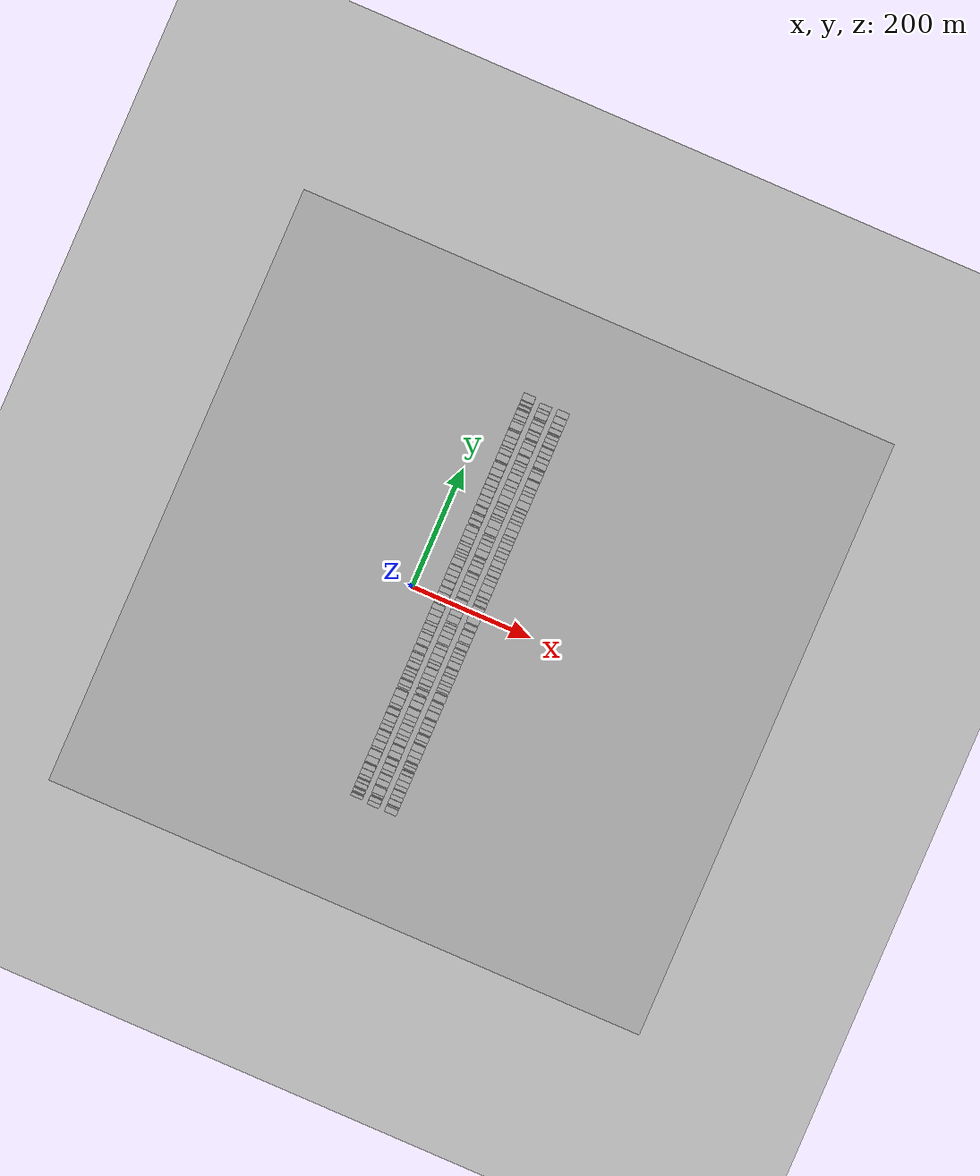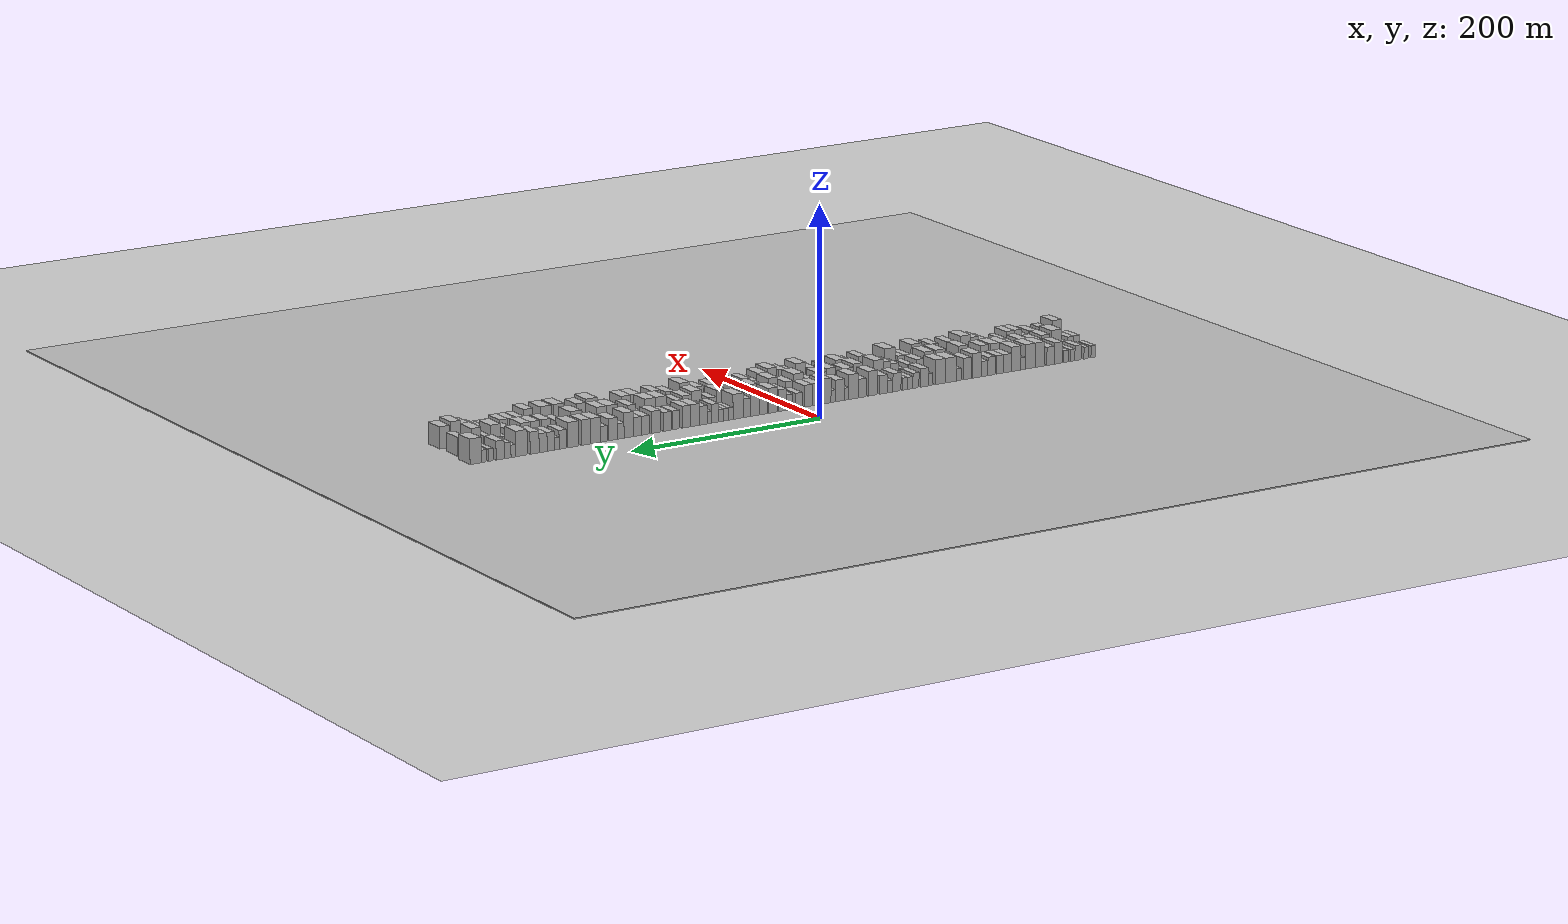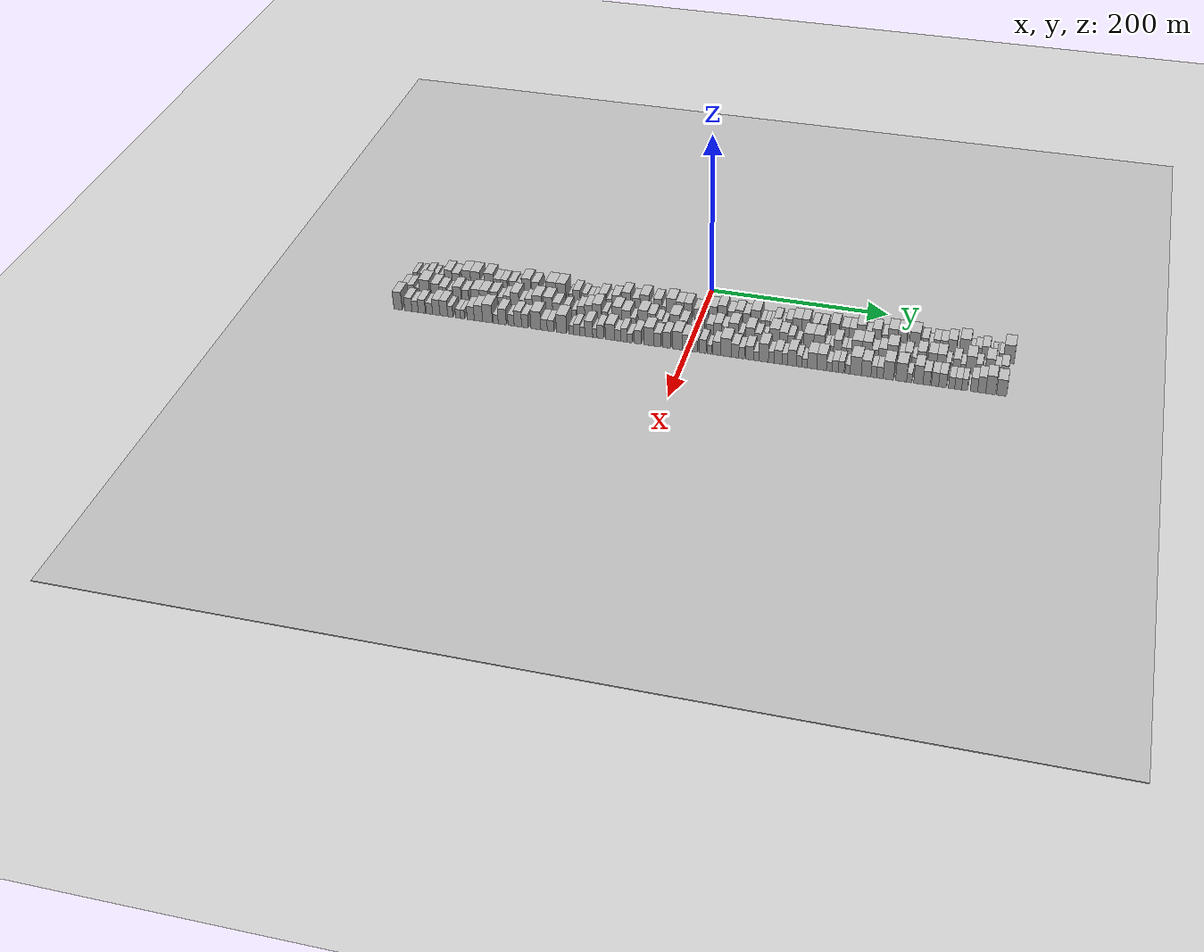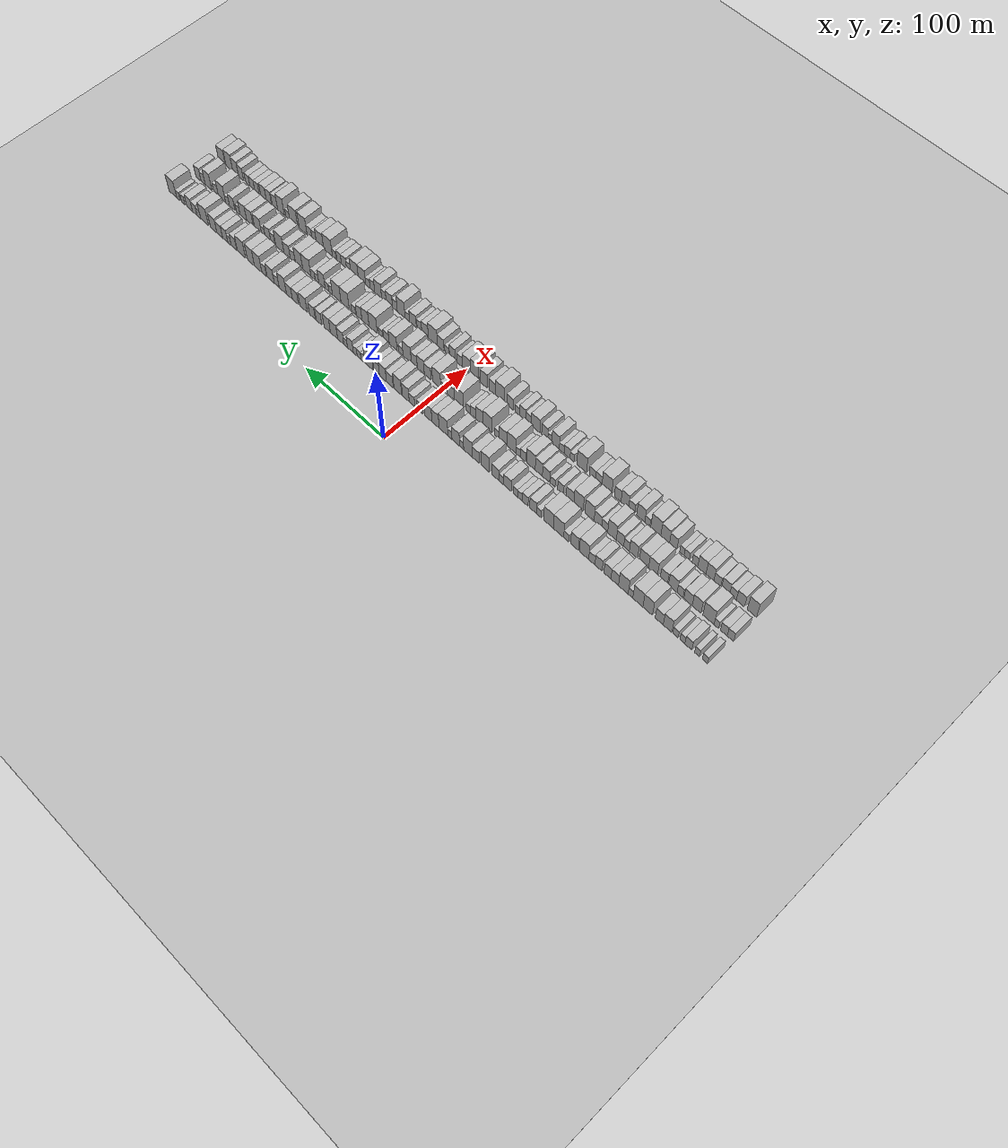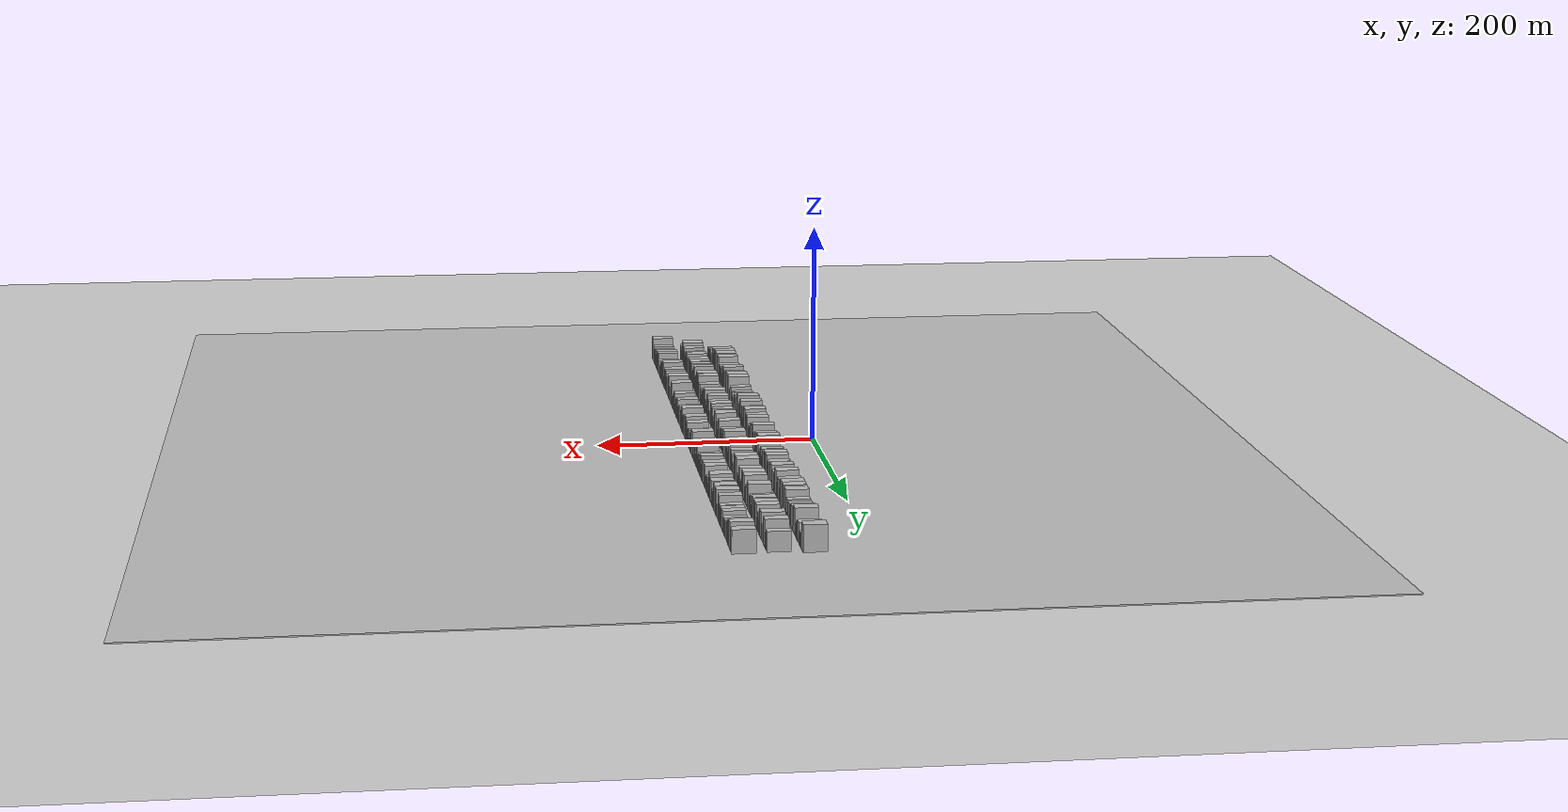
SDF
<?xml version="1.0" encoding="utf-8"?>

<sdf version="1.6">

   <world name="default">

      <gui fullscreen="0">

         <camera name="user_camera">

            <pose>-15 0 4.57585 0 0 0</pose>

            <view_controller>orbit</view_controller>

         </camera>

      </gui>

      <scene>

         <sky>

           <clouds>

             <speed>12</speed>

           </clouds>

         </sky>

         <ambient>0.4 0.4 0.4 1</ambient>

         <background>0.7 0.7 0.7 1</background>

         <shadows>1</shadows>

      </scene>

      <gravity>0 0 -9.8066</gravity>

      <magnetic_field>6e-06 2.3e-05 -4.2e-05</magnetic_field>

      <physics default="0" name="default_physics" type="ode">

         <ode>

            <solver>

               <type>quick</type>

               <iters>10</iters>

               <sor>1.0</sor>

               <use_dynamic_moi_rescaling>0</use_dynamic_moi_rescaling>

            </solver>

            <constraints>

               <cfm>0</cfm>

               <erp>0.2</erp>

               <contact_max_correcting_vel>100</contact_max_correcting_vel>

               <contact_surface_layer>0.001</contact_surface_layer>

            </constraints>

         </ode>

         <max_step_size>0.004</max_step_size>

         <real_time_factor>1</real_time_factor>

         <real_time_update_rate>250</real_time_update_rate>

      </physics>

      <light name="sun" type="directional">

         <cast_shadows>1</cast_shadows>

         <pose>0 0 10 0 0 0</pose>

         <diffuse>0.8 0.8 0.8 1</diffuse>

         <specular>0.2 0.2 0.2 1</specular>

         <attenuation>

            <range>1000</range>

            <constant>0.9</constant>

            <linear>0.01</linear>

            <quadratic>0.001</quadratic>

         </attenuation>

         <direction>-0.5 0.1 -0.9</direction>

      </light>

      <include>

         <name>ground_plane_1</name>

         <uri>model://HANNAS_ground_plane</uri>

         <pose>0 0 0  0 0 0</pose>

      </include>

      <include>

         <name>ground_plane_2</name>

         <uri>model://HANNAS_ground_plane</uri>

         <pose>100 0 0  0 0 0</pose>

      </include>

      <model name="building_1">

         <static>1</static>

         <pose frame="">50.0000 -331.2544 0 0.000000 0.000000 0.000000</pose>

         <link name="link">

            <pose frame="">0 0 6.00 0 0 0</pose>

            <collision name="collision">

               <geometry>

                  <box>

                     <size>20.0000 5.4912 12.0000</size>

                  </box>

               </geometry>

               <max_contacts>10</max_contacts>

               <surface>

                  <contact>

                     <ode/>

                  </contact>

                  <bounce/>

                  <friction>

                     <torsional>

                        <ode/>

                     </torsional>

                     <ode/>

                  </friction>

               </surface>

            </collision>

            <visual name="visual">

               <cast_shadows>0</cast_shadows>

               <geometry>

                  <box>

                     <size>20.0000 5.4912 12.0000</size>

                  </box>

               </geometry>

               <material>

                  <script>

                     <uri>model://HANNAS_wall/materials/scripts</uri>

                     <uri>model://HANNAS_wall/materials/textures</uri>

                     <name>vrc/HANNAS_wall</name>

                  </script>

               </material>

            </visual>

            <self_collide>0</self_collide>

            <enable_wind>0</enable_wind>

            <kinematic>0</kinematic>

         </link>

      </model>

      <model name="building_2">

         <static>1</static>

         <pose frame="">50.0000 -322.9805 0 0.000000 0.000000 0.000000</pose>

         <link name="link">

            <pose frame="">0 0 6.00 0 0 0</pose>

            <collision name="collision">

               <geometry>

                  <box>

                     <size>20.0000 5.0566 12.0000</size>

                  </box>

               </geometry>

               <max_contacts>10</max_contacts>

               <surface>

                  <contact>

                     <ode/>

                  </contact>

                  <bounce/>

                  <friction>

                     <torsional>

                        <ode/>

                     </torsional>

                     <ode/>

                  </friction>

               </surface>

            </collision>

            <visual name="visual">

               <cast_shadows>0</cast_shadows>

               <geometry>

                  <box>

                     <size>20.0000 5.0566 12.0000</size>

                  </box>

               </geometry>

               <material>

                  <script>

                     <uri>model://HANNAS_wall/materials/scripts</uri>

                     <uri>model://HANNAS_wall/materials/textures</uri>

                     <name>vrc/HANNAS_wall</name>

                  </script>

               </material>

            </visual>

            <self_collide>0</self_collide>

            <enable_wind>0</enable_wind>

            <kinematic>0</kinematic>

         </link>

      </model>

      <model name="building_3">

         <static>1</static>

         <pose frame="">50.0000 -313.7861 0 0.000000 0.000000 0.000000</pose>

         <link name="link">

            <pose frame="">0 0 7.50 0 0 0</pose>

            <collision name="collision">

               <geometry>

                  <box>

                     <size>20.0000 7.3321 15.0000</size>

                  </box>

               </geometry>

               <max_contacts>10</max_contacts>

               <surface>

                  <contact>

                     <ode/>

                  </contact>

                  <bounce/>

                  <friction>

                     <torsional>

                        <ode/>

                     </torsional>

                     <ode/>

                  </friction>

               </surface>

            </collision>

            <visual name="visual">

               <cast_shadows>0</cast_shadows>

               <geometry>

                  <box>

                     <size>20.0000 7.3321 15.0000</size>

                  </box>

               </geometry>

               <material>

                  <script>

                     <uri>model://HANNAS_wall/materials/scripts</uri>

                     <uri>model://HANNAS_wall/materials/textures</uri>

                     <name>vrc/HANNAS_wall</name>

                  </script>

               </material>

            </visual>

            <self_collide>0</self_collide>

            <enable_wind>0</enable_wind>

            <kinematic>0</kinematic>

         </link>

      </model>

      <model name="building_4">

         <static>1</static>

         <pose frame="">50.0000 -307.4647 0 0.000000 0.000000 0.000000</pose>

         <link name="link">

            <pose frame="">0 0 6.00 0 0 0</pose>

            <collision name="collision">

               <geometry>

                  <box>

                     <size>20.0000 5.3108 12.0000</size>

                  </box>

               </geometry>

               <max_contacts>10</max_contacts>

               <surface>

                  <contact>

                     <ode/>

                  </contact>

                  <bounce/>

                  <friction>

                     <torsional>

                        <ode/>

                     </torsional>

                     <ode/>

                  </friction>

               </surface>

            </collision>

            <visual name="visual">

               <cast_shadows>0</cast_shadows>

               <geometry>

                  <box>

                     <size>20.0000 5.3108 12.0000</size>

                  </box>

               </geometry>

               <material>

                  <script>

                     <uri>model://HANNAS_wall/materials/scripts</uri>

                     <uri>model://HANNAS_wall/materials/textures</uri>

                     <name>vrc/HANNAS_wall</name>

                  </script>

               </material>

            </visual>

            <self_collide>0</self_collide>

            <enable_wind>0</enable_wind>

            <kinematic>0</kinematic>

         </link>

      </model>

      <model name="building_5">

         <static>1</static>

         <pose frame="">50.0000 -300.0003 0 0.000000 0.000000 0.000000</pose>

         <link name="link">

            <pose frame="">0 0 6.00 0 0 0</pose>

            <collision name="collision">

               <geometry>

                  <box>

                     <size>20.0000 5.6180 12.0000</size>

                  </box>

               </geometry>

               <max_contacts>10</max_contacts>

               <surface>

                  <contact>

                     <ode/>

                  </contact>

                  <bounce/>

                  <friction>

                     <torsional>

                        <ode/>

                     </torsional>

                     <ode/>

                  </friction>

               </surface>

            </collision>

            <visual name="visual">

               <cast_shadows>0</cast_shadows>

               <geometry>

                  <box>

                     <size>20.0000 5.6180 12.0000</size>

                  </box>

               </geometry>

               <material>

                  <script>

                     <uri>model://HANNAS_wall/materials/scripts</uri>

                     <uri>model://HANNAS_wall/materials/textures</uri>

                     <name>vrc/HANNAS_wall</name>

                  </script>

               </material>

            </visual>

            <self_collide>0</self_collide>

            <enable_wind>0</enable_wind>

            <kinematic>0</kinematic>

         </link>

      </model>

      <model name="building_6">

         <static>1</static>

         <pose frame="">50.0000 -291.5749 0 0.000000 0.000000 0.000000</pose>

         <link name="link">

            <pose frame="">0 0 10.50 0 0 0</pose>

            <collision name="collision">

               <geometry>

                  <box>

                     <size>20.0000 9.2328 21.0000</size>

                  </box>

               </geometry>

               <max_contacts>10</max_contacts>

               <surface>

                  <contact>

                     <ode/>

                  </contact>

                  <bounce/>

                  <friction>

                     <torsional>

                        <ode/>

                     </torsional>

                     <ode/>

                  </friction>

               </surface>

            </collision>

            <visual name="visual">

               <cast_shadows>0</cast_shadows>

               <geometry>

                  <box>

                     <size>20.0000 9.2328 21.0000</size>

                  </box>

               </geometry>

               <material>

                  <script>

                     <uri>model://HANNAS_wall/materials/scripts</uri>

                     <uri>model://HANNAS_wall/materials/textures</uri>

                     <name>vrc/HANNAS_wall</name>

                  </script>

               </material>

            </visual>

            <self_collide>0</self_collide>

            <enable_wind>0</enable_wind>

            <kinematic>0</kinematic>

         </link>

      </model>

      <model name="building_7">

         <static>1</static>

         <pose frame="">50.0000 -282.5871 0 0.000000 0.000000 0.000000</pose>

         <link name="link">

            <pose frame="">0 0 9.00 0 0 0</pose>

            <collision name="collision">

               <geometry>

                  <box>

                     <size>20.0000 8.7428 18.0000</size>

                  </box>

               </geometry>

               <max_contacts>10</max_contacts>

               <surface>

                  <contact>

                     <ode/>

                  </contact>

                  <bounce/>

                  <friction>

                     <torsional>

                        <ode/>

                     </torsional>

                     <ode/>

                  </friction>

               </surface>

            </collision>

            <visual name="visual">

               <cast_shadows>0</cast_shadows>

               <geometry>

                  <box>

                     <size>20.0000 8.7428 18.0000</size>

                  </box>

               </geometry>

               <material>

                  <script>

                     <uri>model://HANNAS_wall/materials/scripts</uri>

                     <uri>model://HANNAS_wall/materials/textures</uri>

                     <name>vrc/HANNAS_wall</name>

                  </script>

               </material>

            </visual>

            <self_collide>0</self_collide>

            <enable_wind>0</enable_wind>

            <kinematic>0</kinematic>

         </link>

      </model>

      <model name="building_8">

         <static>1</static>

         <pose frame="">50.0000 -270.0461 0 0.000000 0.000000 0.000000</pose>

         <link name="link">

            <pose frame="">0 0 12.00 0 0 0</pose>

            <collision name="collision">

               <geometry>

                  <box>

                     <size>20.0000 10.3390 24.0000</size>

                  </box>

               </geometry>

               <max_contacts>10</max_contacts>

               <surface>

                  <contact>

                     <ode/>

                  </contact>

                  <bounce/>

                  <friction>

                     <torsional>

                        <ode/>

                     </torsional>

                     <ode/>

                  </friction>

               </surface>

            </collision>

            <visual name="visual">

               <cast_shadows>0</cast_shadows>

               <geometry>

                  <box>

                     <size>20.0000 10.3390 24.0000</size>

                  </box>

               </geometry>

               <material>

                  <script>

                     <uri>model://HANNAS_wall/materials/scripts</uri>

                     <uri>model://HANNAS_wall/materials/textures</uri>

                     <name>vrc/HANNAS_wall</name>

                  </script>

               </material>

            </visual>

            <self_collide>0</self_collide>

            <enable_wind>0</enable_wind>

            <kinematic>0</kinematic>

         </link>

      </model>

      <model name="building_9">

         <static>1</static>

         <pose frame="">50.0000 -259.3363 0 0.000000 0.000000 0.000000</pose>

         <link name="link">

            <pose frame="">0 0 12.00 0 0 0</pose>

            <collision name="collision">

               <geometry>

                  <box>

                     <size>20.0000 11.0808 24.0000</size>

                  </box>

               </geometry>

               <max_contacts>10</max_contacts>

               <surface>

                  <contact>

                     <ode/>

                  </contact>

                  <bounce/>

                  <friction>

                     <torsional>

                        <ode/>

                     </torsional>

                     <ode/>

                  </friction>

               </surface>

            </collision>

            <visual name="visual">

               <cast_shadows>0</cast_shadows>

               <geometry>

                  <box>

                     <size>20.0000 11.0808 24.0000</size>

                  </box>

               </geometry>

               <material>

                  <script>

                     <uri>model://HANNAS_wall/materials/scripts</uri>

                     <uri>model://HANNAS_wall/materials/textures</uri>

                     <name>vrc/HANNAS_wall</name>

                  </script>

               </material>

            </visual>

            <self_collide>0</self_collide>

            <enable_wind>0</enable_wind>

            <kinematic>0</kinematic>

         </link>

      </model>

      <model name="building_10">

         <static>1</static>

         <pose frame="">50.0000 -251.2310 0 0.000000 0.000000 0.000000</pose>

         <link name="link">

            <pose frame="">0 0 6.00 0 0 0</pose>

            <collision name="collision">

               <geometry>

                  <box>

                     <size>20.0000 5.1298 12.0000</size>

                  </box>

               </geometry>

               <max_contacts>10</max_contacts>

               <surface>

                  <contact>

                     <ode/>

                  </contact>

                  <bounce/>

                  <friction>

                     <torsional>

                        <ode/>

                     </torsional>

                     <ode/>

                  </friction>

               </surface>

            </collision>

            <visual name="visual">

               <cast_shadows>0</cast_shadows>

               <geometry>

                  <box>

                     <size>20.0000 5.1298 12.0000</size>

                  </box>

               </geometry>

               <material>

                  <script>

                     <uri>model://HANNAS_wall/materials/scripts</uri>

                     <uri>model://HANNAS_wall/materials/textures</uri>

                     <name>vrc/HANNAS_wall</name>

                  </script>

               </material>

            </visual>

            <self_collide>0</self_collide>

            <enable_wind>0</enable_wind>

            <kinematic>0</kinematic>

         </link>

      </model>

      <model name="building_11">

         <static>1</static>

         <pose frame="">50.0000 -243.3117 0 0.000000 0.000000 0.000000</pose>

         <link name="link">

            <pose frame="">0 0 12.00 0 0 0</pose>

            <collision name="collision">

               <geometry>

                  <box>

                     <size>20.0000 10.7088 24.0000</size>

                  </box>

               </geometry>

               <max_contacts>10</max_contacts>

               <surface>

                  <contact>

                     <ode/>

                  </contact>

                  <bounce/>

                  <friction>

                     <torsional>

                        <ode/>

                     </torsional>

                     <ode/>

                  </friction>

               </surface>

            </collision>

            <visual name="visual">

               <cast_shadows>0</cast_shadows>

               <geometry>

                  <box>

                     <size>20.0000 10.7088 24.0000</size>

                  </box>

               </geometry>

               <material>

                  <script>

                     <uri>model://HANNAS_wall/materials/scripts</uri>

                     <uri>model://HANNAS_wall/materials/textures</uri>

                     <name>vrc/HANNAS_wall</name>

                  </script>

               </material>

            </visual>

            <self_collide>0</self_collide>

            <enable_wind>0</enable_wind>

            <kinematic>0</kinematic>

         </link>

      </model>

      <model name="building_12">

         <static>1</static>

         <pose frame="">50.0000 -233.7596 0 0.000000 0.000000 0.000000</pose>

         <link name="link">

            <pose frame="">0 0 9.00 0 0 0</pose>

            <collision name="collision">

               <geometry>

                  <box>

                     <size>20.0000 8.3953 18.0000</size>

                  </box>

               </geometry>

               <max_contacts>10</max_contacts>

               <surface>

                  <contact>

                     <ode/>

                  </contact>

                  <bounce/>

                  <friction>

                     <torsional>

                        <ode/>

                     </torsional>

                     <ode/>

                  </friction>

               </surface>

            </collision>

            <visual name="visual">

               <cast_shadows>0</cast_shadows>

               <geometry>

                  <box>

                     <size>20.0000 8.3953 18.0000</size>

                  </box>

               </geometry>

               <material>

                  <script>

                     <uri>model://HANNAS_wall/materials/scripts</uri>

                     <uri>model://HANNAS_wall/materials/textures</uri>

                     <name>vrc/HANNAS_wall</name>

                  </script>

               </material>

            </visual>

            <self_collide>0</self_collide>

            <enable_wind>0</enable_wind>

            <kinematic>0</kinematic>

         </link>

      </model>

      <model name="building_13">

         <static>1</static>

         <pose frame="">50.0000 -225.6236 0 0.000000 0.000000 0.000000</pose>

         <link name="link">

            <pose frame="">0 0 9.00 0 0 0</pose>

            <collision name="collision">

               <geometry>

                  <box>

                     <size>20.0000 7.8767 18.0000</size>

                  </box>

               </geometry>

               <max_contacts>10</max_contacts>

               <surface>

                  <contact>

                     <ode/>

                  </contact>

                  <bounce/>

                  <friction>

                     <torsional>

                        <ode/>

                     </torsional>

                     <ode/>

                  </friction>

               </surface>

            </collision>

            <visual name="visual">

               <cast_shadows>0</cast_shadows>

               <geometry>

                  <box>

                     <size>20.0000 7.8767 18.0000</size>

                  </box>

               </geometry>

               <material>

                  <script>

                     <uri>model://HANNAS_wall/materials/scripts</uri>

                     <uri>model://HANNAS_wall/materials/textures</uri>

                     <name>vrc/HANNAS_wall</name>

                  </script>

               </material>

            </visual>

            <self_collide>0</self_collide>

            <enable_wind>0</enable_wind>

            <kinematic>0</kinematic>

         </link>

      </model>

      <model name="building_14">

         <static>1</static>

         <pose frame="">50.0000 -215.6583 0 0.000000 0.000000 0.000000</pose>

         <link name="link">

            <pose frame="">0 0 9.00 0 0 0</pose>

            <collision name="collision">

               <geometry>

                  <box>

                     <size>20.0000 8.0539 18.0000</size>

                  </box>

               </geometry>

               <max_contacts>10</max_contacts>

               <surface>

                  <contact>

                     <ode/>

                  </contact>

                  <bounce/>

                  <friction>

                     <torsional>

                        <ode/>

                     </torsional>

                     <ode/>

                  </friction>

               </surface>

            </collision>

            <visual name="visual">

               <cast_shadows>0</cast_shadows>

               <geometry>

                  <box>

                     <size>20.0000 8.0539 18.0000</size>

                  </box>

               </geometry>

               <material>

                  <script>

                     <uri>model://HANNAS_wall/materials/scripts</uri>

                     <uri>model://HANNAS_wall/materials/textures</uri>

                     <name>vrc/HANNAS_wall</name>

                  </script>

               </material>

            </visual>

            <self_collide>0</self_collide>

            <enable_wind>0</enable_wind>

            <kinematic>0</kinematic>

         </link>

      </model>

      <model name="building_15">

         <static>1</static>

         <pose frame="">50.0000 -208.1335 0 0.000000 0.000000 0.000000</pose>

         <link name="link">

            <pose frame="">0 0 7.50 0 0 0</pose>

            <collision name="collision">

               <geometry>

                  <box>

                     <size>20.0000 6.9958 15.0000</size>

                  </box>

               </geometry>

               <max_contacts>10</max_contacts>

               <surface>

                  <contact>

                     <ode/>

                  </contact>

                  <bounce/>

                  <friction>

                     <torsional>

                        <ode/>

                     </torsional>

                     <ode/>

                  </friction>

               </surface>

            </collision>

            <visual name="visual">

               <cast_shadows>0</cast_shadows>

               <geometry>

                  <box>

                     <size>20.0000 6.9958 15.0000</size>

                  </box>

               </geometry>

               <material>

                  <script>

                     <uri>model://HANNAS_wall/materials/scripts</uri>

                     <uri>model://HANNAS_wall/materials/textures</uri>

                     <name>vrc/HANNAS_wall</name>

                  </script>

               </material>

            </visual>

            <self_collide>0</self_collide>

            <enable_wind>0</enable_wind>

            <kinematic>0</kinematic>

         </link>

      </model>

      <model name="building_16">

         <static>1</static>

         <pose frame="">50.0000 -199.3201 0 0.000000 0.000000 0.000000</pose>

         <link name="link">

            <pose frame="">0 0 12.00 0 0 0</pose>

            <collision name="collision">

               <geometry>

                  <box>

                     <size>20.0000 10.6309 24.0000</size>

                  </box>

               </geometry>

               <max_contacts>10</max_contacts>

               <surface>

                  <contact>

                     <ode/>

                  </contact>

                  <bounce/>

                  <friction>

                     <torsional>

                        <ode/>

                     </torsional>

                     <ode/>

                  </friction>

               </surface>

            </collision>

            <visual name="visual">

               <cast_shadows>0</cast_shadows>

               <geometry>

                  <box>

                     <size>20.0000 10.6309 24.0000</size>

                  </box>

               </geometry>

               <material>

                  <script>

                     <uri>model://HANNAS_wall/materials/scripts</uri>

                     <uri>model://HANNAS_wall/materials/textures</uri>

                     <name>vrc/HANNAS_wall</name>

                  </script>

               </material>

            </visual>

            <self_collide>0</self_collide>

            <enable_wind>0</enable_wind>

            <kinematic>0</kinematic>

         </link>

      </model>

      <model name="building_17">

         <static>1</static>

         <pose frame="">50.0000 -188.5351 0 0.000000 0.000000 0.000000</pose>

         <link name="link">

            <pose frame="">0 0 10.50 0 0 0</pose>

            <collision name="collision">

               <geometry>

                  <box>

                     <size>20.0000 8.9390 21.0000</size>

                  </box>

               </geometry>

               <max_contacts>10</max_contacts>

               <surface>

                  <contact>

                     <ode/>

                  </contact>

                  <bounce/>

                  <friction>

                     <torsional>

                        <ode/>

                     </torsional>

                     <ode/>

                  </friction>

               </surface>

            </collision>

            <visual name="visual">

               <cast_shadows>0</cast_shadows>

               <geometry>

                  <box>

                     <size>20.0000 8.9390 21.0000</size>

                  </box>

               </geometry>

               <material>

                  <script>

                     <uri>model://HANNAS_wall/materials/scripts</uri>

                     <uri>model://HANNAS_wall/materials/textures</uri>

                     <name>vrc/HANNAS_wall</name>

                  </script>

               </material>

            </visual>

            <self_collide>0</self_collide>

            <enable_wind>0</enable_wind>

            <kinematic>0</kinematic>

         </link>

      </model>

      <model name="building_18">

         <static>1</static>

         <pose frame="">50.0000 -179.0991 0 0.000000 0.000000 0.000000</pose>

         <link name="link">

            <pose frame="">0 0 6.00 0 0 0</pose>

            <collision name="collision">

               <geometry>

                  <box>

                     <size>20.0000 5.9330 12.0000</size>

                  </box>

               </geometry>

               <max_contacts>10</max_contacts>

               <surface>

                  <contact>

                     <ode/>

                  </contact>

                  <bounce/>

                  <friction>

                     <torsional>

                        <ode/>

                     </torsional>

                     <ode/>

                  </friction>

               </surface>

            </collision>

            <visual name="visual">

               <cast_shadows>0</cast_shadows>

               <geometry>

                  <box>

                     <size>20.0000 5.9330 12.0000</size>

                  </box>

               </geometry>

               <material>

                  <script>

                     <uri>model://HANNAS_wall/materials/scripts</uri>

                     <uri>model://HANNAS_wall/materials/textures</uri>

                     <name>vrc/HANNAS_wall</name>

                  </script>

               </material>

            </visual>

            <self_collide>0</self_collide>

            <enable_wind>0</enable_wind>

            <kinematic>0</kinematic>

         </link>

      </model>

      <model name="building_19">

         <static>1</static>

         <pose frame="">50.0000 -170.2115 0 0.000000 0.000000 0.000000</pose>

         <link name="link">

            <pose frame="">0 0 12.00 0 0 0</pose>

            <collision name="collision">

               <geometry>

                  <box>

                     <size>20.0000 11.8422 24.0000</size>

                  </box>

               </geometry>

               <max_contacts>10</max_contacts>

               <surface>

                  <contact>

                     <ode/>

                  </contact>

                  <bounce/>

                  <friction>

                     <torsional>

                        <ode/>

                     </torsional>

                     <ode/>

                  </friction>

               </surface>

            </collision>

            <visual name="visual">

               <cast_shadows>0</cast_shadows>

               <geometry>

                  <box>

                     <size>20.0000 11.8422 24.0000</size>

                  </box>

               </geometry>

               <material>

                  <script>

                     <uri>model://HANNAS_wall/materials/scripts</uri>

                     <uri>model://HANNAS_wall/materials/textures</uri>

                     <name>vrc/HANNAS_wall</name>

                  </script>

               </material>

            </visual>

            <self_collide>0</self_collide>

            <enable_wind>0</enable_wind>

            <kinematic>0</kinematic>

         </link>

      </model>

      <model name="building_20">

         <static>1</static>

         <pose frame="">50.0000 -158.7037 0 0.000000 0.000000 0.000000</pose>

         <link name="link">

            <pose frame="">0 0 12.00 0 0 0</pose>

            <collision name="collision">

               <geometry>

                  <box>

                     <size>20.0000 11.1732 24.0000</size>

                  </box>

               </geometry>

               <max_contacts>10</max_contacts>

               <surface>

                  <contact>

                     <ode/>

                  </contact>

                  <bounce/>

                  <friction>

                     <torsional>

                        <ode/>

                     </torsional>

                     <ode/>

                  </friction>

               </surface>

            </collision>

            <visual name="visual">

               <cast_shadows>0</cast_shadows>

               <geometry>

                  <box>

                     <size>20.0000 11.1732 24.0000</size>

                  </box>

               </geometry>

               <material>

                  <script>

                     <uri>model://HANNAS_wall/materials/scripts</uri>

                     <uri>model://HANNAS_wall/materials/textures</uri>

                     <name>vrc/HANNAS_wall</name>

                  </script>

               </material>

            </visual>

            <self_collide>0</self_collide>

            <enable_wind>0</enable_wind>

            <kinematic>0</kinematic>

         </link>

      </model>

      <model name="building_21">

         <static>1</static>

         <pose frame="">50.0000 -147.5431 0 0.000000 0.000000 0.000000</pose>

         <link name="link">

            <pose frame="">0 0 6.00 0 0 0</pose>

            <collision name="collision">

               <geometry>

                  <box>

                     <size>20.0000 5.1480 12.0000</size>

                  </box>

               </geometry>

               <max_contacts>10</max_contacts>

               <surface>

                  <contact>

                     <ode/>

                  </contact>

                  <bounce/>

                  <friction>

                     <torsional>

                        <ode/>

                     </torsional>

                     <ode/>

                  </friction>

               </surface>

            </collision>

            <visual name="visual">

               <cast_shadows>0</cast_shadows>

               <geometry>

                  <box>

                     <size>20.0000 5.1480 12.0000</size>

                  </box>

               </geometry>

               <material>

                  <script>

                     <uri>model://HANNAS_wall/materials/scripts</uri>

                     <uri>model://HANNAS_wall/materials/textures</uri>

                     <name>vrc/HANNAS_wall</name>

                  </script>

               </material>

            </visual>

            <self_collide>0</self_collide>

            <enable_wind>0</enable_wind>

            <kinematic>0</kinematic>

         </link>

      </model>

      <model name="building_22">

         <static>1</static>

         <pose frame="">50.0000 -140.8523 0 0.000000 0.000000 0.000000</pose>

         <link name="link">

            <pose frame="">0 0 9.00 0 0 0</pose>

            <collision name="collision">

               <geometry>

                  <box>

                     <size>20.0000 8.2338 18.0000</size>

                  </box>

               </geometry>

               <max_contacts>10</max_contacts>

               <surface>

                  <contact>

                     <ode/>

                  </contact>

                  <bounce/>

                  <friction>

                     <torsional>

                        <ode/>

                     </torsional>

                     <ode/>

                  </friction>

               </surface>

            </collision>

            <visual name="visual">

               <cast_shadows>0</cast_shadows>

               <geometry>

                  <box>

                     <size>20.0000 8.2338 18.0000</size>

                  </box>

               </geometry>

               <material>

                  <script>

                     <uri>model://HANNAS_wall/materials/scripts</uri>

                     <uri>model://HANNAS_wall/materials/textures</uri>

                     <name>vrc/HANNAS_wall</name>

                  </script>

               </material>

            </visual>

            <self_collide>0</self_collide>

            <enable_wind>0</enable_wind>

            <kinematic>0</kinematic>

         </link>

      </model>

      <model name="building_23">

         <static>1</static>

         <pose frame="">50.0000 -131.4011 0 0.000000 0.000000 0.000000</pose>

         <link name="link">

            <pose frame="">0 0 7.50 0 0 0</pose>

            <collision name="collision">

               <geometry>

                  <box>

                     <size>20.0000 6.6685 15.0000</size>

                  </box>

               </geometry>

               <max_contacts>10</max_contacts>

               <surface>

                  <contact>

                     <ode/>

                  </contact>

                  <bounce/>

                  <friction>

                     <torsional>

                        <ode/>

                     </torsional>

                     <ode/>

                  </friction>

               </surface>

            </collision>

            <visual name="visual">

               <cast_shadows>0</cast_shadows>

               <geometry>

                  <box>

                     <size>20.0000 6.6685 15.0000</size>

                  </box>

               </geometry>

               <material>

                  <script>

                     <uri>model://HANNAS_wall/materials/scripts</uri>

                     <uri>model://HANNAS_wall/materials/textures</uri>

                     <name>vrc/HANNAS_wall</name>

                  </script>

               </material>

            </visual>

            <self_collide>0</self_collide>

            <enable_wind>0</enable_wind>

            <kinematic>0</kinematic>

         </link>

      </model>

      <model name="building_24">

         <static>1</static>

         <pose frame="">50.0000 -125.1123 0 0.000000 0.000000 0.000000</pose>

         <link name="link">

            <pose frame="">0 0 6.00 0 0 0</pose>

            <collision name="collision">

               <geometry>

                  <box>

                     <size>20.0000 5.9090 12.0000</size>

                  </box>

               </geometry>

               <max_contacts>10</max_contacts>

               <surface>

                  <contact>

                     <ode/>

                  </contact>

                  <bounce/>

                  <friction>

                     <torsional>

                        <ode/>

                     </torsional>

                     <ode/>

                  </friction>

               </surface>

            </collision>

            <visual name="visual">

               <cast_shadows>0</cast_shadows>

               <geometry>

                  <box>

                     <size>20.0000 5.9090 12.0000</size>

                  </box>

               </geometry>

               <material>

                  <script>

                     <uri>model://HANNAS_wall/materials/scripts</uri>

                     <uri>model://HANNAS_wall/materials/textures</uri>

                     <name>vrc/HANNAS_wall</name>

                  </script>

               </material>

            </visual>

            <self_collide>0</self_collide>

            <enable_wind>0</enable_wind>

            <kinematic>0</kinematic>

         </link>

      </model>

      <model name="building_25">

         <static>1</static>

         <pose frame="">50.0000 -119.4929 0 0.000000 0.000000 0.000000</pose>

         <link name="link">

            <pose frame="">0 0 6.00 0 0 0</pose>

            <collision name="collision">

               <geometry>

                  <box>

                     <size>20.0000 5.3299 12.0000</size>

                  </box>

               </geometry>

               <max_contacts>10</max_contacts>

               <surface>

                  <contact>

                     <ode/>

                  </contact>

                  <bounce/>

                  <friction>

                     <torsional>

                        <ode/>

                     </torsional>

                     <ode/>

                  </friction>

               </surface>

            </collision>

            <visual name="visual">

               <cast_shadows>0</cast_shadows>

               <geometry>

                  <box>

                     <size>20.0000 5.3299 12.0000</size>

                  </box>

               </geometry>

               <material>

                  <script>

                     <uri>model://HANNAS_wall/materials/scripts</uri>

                     <uri>model://HANNAS_wall/materials/textures</uri>

                     <name>vrc/HANNAS_wall</name>

                  </script>

               </material>

            </visual>

            <self_collide>0</self_collide>

            <enable_wind>0</enable_wind>

            <kinematic>0</kinematic>

         </link>

      </model>

      <model name="building_26">

         <static>1</static>

         <pose frame="">50.0000 -110.3879 0 0.000000 0.000000 0.000000</pose>

         <link name="link">

            <pose frame="">0 0 9.00 0 0 0</pose>

            <collision name="collision">

               <geometry>

                  <box>

                     <size>20.0000 8.8800 18.0000</size>

                  </box>

               </geometry>

               <max_contacts>10</max_contacts>

               <surface>

                  <contact>

                     <ode/>

                  </contact>

                  <bounce/>

                  <friction>

                     <torsional>

                        <ode/>

                     </torsional>

                     <ode/>

                  </friction>

               </surface>

            </collision>

            <visual name="visual">

               <cast_shadows>0</cast_shadows>

               <geometry>

                  <box>

                     <size>20.0000 8.8800 18.0000</size>

                  </box>

               </geometry>

               <material>

                  <script>

                     <uri>model://HANNAS_wall/materials/scripts</uri>

                     <uri>model://HANNAS_wall/materials/textures</uri>

                     <name>vrc/HANNAS_wall</name>

                  </script>

               </material>

            </visual>

            <self_collide>0</self_collide>

            <enable_wind>0</enable_wind>

            <kinematic>0</kinematic>

         </link>

      </model>

      <model name="building_27">

         <static>1</static>

         <pose frame="">50.0000 -103.1046 0 0.000000 0.000000 0.000000</pose>

         <link name="link">

            <pose frame="">0 0 6.00 0 0 0</pose>

            <collision name="collision">

               <geometry>

                  <box>

                     <size>20.0000 5.6866 12.0000</size>

                  </box>

               </geometry>

               <max_contacts>10</max_contacts>

               <surface>

                  <contact>

                     <ode/>

                  </contact>

                  <bounce/>

                  <friction>

                     <torsional>

                        <ode/>

                     </torsional>

                     <ode/>

                  </friction>

               </surface>

            </collision>

            <visual name="visual">

               <cast_shadows>0</cast_shadows>

               <geometry>

                  <box>

                     <size>20.0000 5.6866 12.0000</size>

                  </box>

               </geometry>

               <material>

                  <script>

                     <uri>model://HANNAS_wall/materials/scripts</uri>

                     <uri>model://HANNAS_wall/materials/textures</uri>

                     <name>vrc/HANNAS_wall</name>

                  </script>

               </material>

            </visual>

            <self_collide>0</self_collide>

            <enable_wind>0</enable_wind>

            <kinematic>0</kinematic>

         </link>

      </model>

      <model name="building_28">

         <static>1</static>

         <pose frame="">50.0000 -95.8927 0 0.000000 0.000000 0.000000</pose>

         <link name="link">

            <pose frame="">0 0 9.00 0 0 0</pose>

            <collision name="collision">

               <geometry>

                  <box>

                     <size>20.0000 8.7373 18.0000</size>

                  </box>

               </geometry>

               <max_contacts>10</max_contacts>

               <surface>

                  <contact>

                     <ode/>

                  </contact>

                  <bounce/>

                  <friction>

                     <torsional>

                        <ode/>

                     </torsional>

                     <ode/>

                  </friction>

               </surface>

            </collision>

            <visual name="visual">

               <cast_shadows>0</cast_shadows>

               <geometry>

                  <box>

                     <size>20.0000 8.7373 18.0000</size>

                  </box>

               </geometry>

               <material>

                  <script>

                     <uri>model://HANNAS_wall/materials/scripts</uri>

                     <uri>model://HANNAS_wall/materials/textures</uri>

                     <name>vrc/HANNAS_wall</name>

                  </script>

               </material>

            </visual>

            <self_collide>0</self_collide>

            <enable_wind>0</enable_wind>

            <kinematic>0</kinematic>

         </link>

      </model>

      <model name="building_29">

         <static>1</static>

         <pose frame="">50.0000 -83.6213 0 0.000000 0.000000 0.000000</pose>

         <link name="link">

            <pose frame="">0 0 12.00 0 0 0</pose>

            <collision name="collision">

               <geometry>

                  <box>

                     <size>20.0000 9.8054 24.0000</size>

                  </box>

               </geometry>

               <max_contacts>10</max_contacts>

               <surface>

                  <contact>

                     <ode/>

                  </contact>

                  <bounce/>

                  <friction>

                     <torsional>

                        <ode/>

                     </torsional>

                     <ode/>

                  </friction>

               </surface>

            </collision>

            <visual name="visual">

               <cast_shadows>0</cast_shadows>

               <geometry>

                  <box>

                     <size>20.0000 9.8054 24.0000</size>

                  </box>

               </geometry>

               <material>

                  <script>

                     <uri>model://HANNAS_wall/materials/scripts</uri>

                     <uri>model://HANNAS_wall/materials/textures</uri>

                     <name>vrc/HANNAS_wall</name>

                  </script>

               </material>

            </visual>

            <self_collide>0</self_collide>

            <enable_wind>0</enable_wind>

            <kinematic>0</kinematic>

         </link>

      </model>

      <model name="building_30">

         <static>1</static>

         <pose frame="">50.0000 -72.2557 0 0.000000 0.000000 0.000000</pose>

         <link name="link">

            <pose frame="">0 0 9.00 0 0 0</pose>

            <collision name="collision">

               <geometry>

                  <box>

                     <size>20.0000 8.9259 18.0000</size>

                  </box>

               </geometry>

               <max_contacts>10</max_contacts>

               <surface>

                  <contact>

                     <ode/>

                  </contact>

                  <bounce/>

                  <friction>

                     <torsional>

                        <ode/>

                     </torsional>

                     <ode/>

                  </friction>

               </surface>

            </collision>

            <visual name="visual">

               <cast_shadows>0</cast_shadows>

               <geometry>

                  <box>

                     <size>20.0000 8.9259 18.0000</size>

                  </box>

               </geometry>

               <material>

                  <script>

                     <uri>model://HANNAS_wall/materials/scripts</uri>

                     <uri>model://HANNAS_wall/materials/textures</uri>

                     <name>vrc/HANNAS_wall</name>

                  </script>

               </material>

            </visual>

            <self_collide>0</self_collide>

            <enable_wind>0</enable_wind>

            <kinematic>0</kinematic>

         </link>

      </model>

      <model name="building_31">

         <static>1</static>

         <pose frame="">50.0000 -62.6025 0 0.000000 0.000000 0.000000</pose>

         <link name="link">

            <pose frame="">0 0 12.00 0 0 0</pose>

            <collision name="collision">

               <geometry>

                  <box>

                     <size>20.0000 10.3805 24.0000</size>

                  </box>

               </geometry>

               <max_contacts>10</max_contacts>

               <surface>

                  <contact>

                     <ode/>

                  </contact>

                  <bounce/>

                  <friction>

                     <torsional>

                        <ode/>

                     </torsional>

                     <ode/>

                  </friction>

               </surface>

            </collision>

            <visual name="visual">

               <cast_shadows>0</cast_shadows>

               <geometry>

                  <box>

                     <size>20.0000 10.3805 24.0000</size>

                  </box>

               </geometry>

               <material>

                  <script>

                     <uri>model://HANNAS_wall/materials/scripts</uri>

                     <uri>model://HANNAS_wall/materials/textures</uri>

                     <name>vrc/HANNAS_wall</name>

                  </script>

               </material>

            </visual>

            <self_collide>0</self_collide>

            <enable_wind>0</enable_wind>

            <kinematic>0</kinematic>

         </link>

      </model>

      <model name="building_32">

         <static>1</static>

         <pose frame="">50.0000 -54.8937 0 0.000000 0.000000 0.000000</pose>

         <link name="link">

            <pose frame="">0 0 6.00 0 0 0</pose>

            <collision name="collision">

               <geometry>

                  <box>

                     <size>20.0000 5.0372 12.0000</size>

                  </box>

               </geometry>

               <max_contacts>10</max_contacts>

               <surface>

                  <contact>

                     <ode/>

                  </contact>

                  <bounce/>

                  <friction>

                     <torsional>

                        <ode/>

                     </torsional>

                     <ode/>

                  </friction>

               </surface>

            </collision>

            <visual name="visual">

               <cast_shadows>0</cast_shadows>

               <geometry>

                  <box>

                     <size>20.0000 5.0372 12.0000</size>

                  </box>

               </geometry>

               <material>

                  <script>

                     <uri>model://HANNAS_wall/materials/scripts</uri>

                     <uri>model://HANNAS_wall/materials/textures</uri>

                     <name>vrc/HANNAS_wall</name>

                  </script>

               </material>

            </visual>

            <self_collide>0</self_collide>

            <enable_wind>0</enable_wind>

            <kinematic>0</kinematic>

         </link>

      </model>

      <model name="building_33">

         <static>1</static>

         <pose frame="">50.0000 -47.6970 0 0.000000 0.000000 0.000000</pose>

         <link name="link">

            <pose frame="">0 0 10.50 0 0 0</pose>

            <collision name="collision">

               <geometry>

                  <box>

                     <size>20.0000 9.3563 21.0000</size>

                  </box>

               </geometry>

               <max_contacts>10</max_contacts>

               <surface>

                  <contact>

                     <ode/>

                  </contact>

                  <bounce/>

                  <friction>

                     <torsional>

                        <ode/>

                     </torsional>

                     <ode/>

                  </friction>

               </surface>

            </collision>

            <visual name="visual">

               <cast_shadows>0</cast_shadows>

               <geometry>

                  <box>

                     <size>20.0000 9.3563 21.0000</size>

                  </box>

               </geometry>

               <material>

                  <script>

                     <uri>model://HANNAS_wall/materials/scripts</uri>

                     <uri>model://HANNAS_wall/materials/textures</uri>

                     <name>vrc/HANNAS_wall</name>

                  </script>

               </material>

            </visual>

            <self_collide>0</self_collide>

            <enable_wind>0</enable_wind>

            <kinematic>0</kinematic>

         </link>

      </model>

      <model name="building_34">

         <static>1</static>

         <pose frame="">50.0000 -40.5022 0 0.000000 0.000000 0.000000</pose>

         <link name="link">

            <pose frame="">0 0 6.00 0 0 0</pose>

            <collision name="collision">

               <geometry>

                  <box>

                     <size>20.0000 5.0334 12.0000</size>

                  </box>

               </geometry>

               <max_contacts>10</max_contacts>

               <surface>

                  <contact>

                     <ode/>

                  </contact>

                  <bounce/>

                  <friction>

                     <torsional>

                        <ode/>

                     </torsional>

                     <ode/>

                  </friction>

               </surface>

            </collision>

            <visual name="visual">

               <cast_shadows>0</cast_shadows>

               <geometry>

                  <box>

                     <size>20.0000 5.0334 12.0000</size>

                  </box>

               </geometry>

               <material>

                  <script>

                     <uri>model://HANNAS_wall/materials/scripts</uri>

                     <uri>model://HANNAS_wall/materials/textures</uri>

                     <name>vrc/HANNAS_wall</name>

                  </script>

               </material>

            </visual>

            <self_collide>0</self_collide>

            <enable_wind>0</enable_wind>

            <kinematic>0</kinematic>

         </link>

      </model>

      <model name="building_35">

         <static>1</static>

         <pose frame="">50.0000 -32.4761 0 0.000000 0.000000 0.000000</pose>

         <link name="link">

            <pose frame="">0 0 12.00 0 0 0</pose>

            <collision name="collision">

               <geometry>

                  <box>

                     <size>20.0000 11.0187 24.0000</size>

                  </box>

               </geometry>

               <max_contacts>10</max_contacts>

               <surface>

                  <contact>

                     <ode/>

                  </contact>

                  <bounce/>

                  <friction>

                     <torsional>

                        <ode/>

                     </torsional>

                     <ode/>

                  </friction>

               </surface>

            </collision>

            <visual name="visual">

               <cast_shadows>0</cast_shadows>

               <geometry>

                  <box>

                     <size>20.0000 11.0187 24.0000</size>

                  </box>

               </geometry>

               <material>

                  <script>

                     <uri>model://HANNAS_wall/materials/scripts</uri>

                     <uri>model://HANNAS_wall/materials/textures</uri>

                     <name>vrc/HANNAS_wall</name>

                  </script>

               </material>

            </visual>

            <self_collide>0</self_collide>

            <enable_wind>0</enable_wind>

            <kinematic>0</kinematic>

         </link>

      </model>

      <model name="building_36">

         <static>1</static>

         <pose frame="">50.0000 -22.5019 0 0.000000 0.000000 0.000000</pose>

         <link name="link">

            <pose frame="">0 0 10.50 0 0 0</pose>

            <collision name="collision">

               <geometry>

                  <box>

                     <size>20.0000 8.9299 21.0000</size>

                  </box>

               </geometry>

               <max_contacts>10</max_contacts>

               <surface>

                  <contact>

                     <ode/>

                  </contact>

                  <bounce/>

                  <friction>

                     <torsional>

                        <ode/>

                     </torsional>

                     <ode/>

                  </friction>

               </surface>

            </collision>

            <visual name="visual">

               <cast_shadows>0</cast_shadows>

               <geometry>

                  <box>

                     <size>20.0000 8.9299 21.0000</size>

                  </box>

               </geometry>

               <material>

                  <script>

                     <uri>model://HANNAS_wall/materials/scripts</uri>

                     <uri>model://HANNAS_wall/materials/textures</uri>

                     <name>vrc/HANNAS_wall</name>

                  </script>

               </material>

            </visual>

            <self_collide>0</self_collide>

            <enable_wind>0</enable_wind>

            <kinematic>0</kinematic>

         </link>

      </model>

      <model name="building_37">

         <static>1</static>

         <pose frame="">50.0000 -13.4229 0 0.000000 0.000000 0.000000</pose>

         <link name="link">

            <pose frame="">0 0 10.50 0 0 0</pose>

            <collision name="collision">

               <geometry>

                  <box>

                     <size>20.0000 9.2280 21.0000</size>

                  </box>

               </geometry>

               <max_contacts>10</max_contacts>

               <surface>

                  <contact>

                     <ode/>

                  </contact>

                  <bounce/>

                  <friction>

                     <torsional>

                        <ode/>

                     </torsional>

                     <ode/>

                  </friction>

               </surface>

            </collision>

            <visual name="visual">

               <cast_shadows>0</cast_shadows>

               <geometry>

                  <box>

                     <size>20.0000 9.2280 21.0000</size>

                  </box>

               </geometry>

               <material>

                  <script>

                     <uri>model://HANNAS_wall/materials/scripts</uri>

                     <uri>model://HANNAS_wall/materials/textures</uri>

                     <name>vrc/HANNAS_wall</name>

                  </script>

               </material>

            </visual>

            <self_collide>0</self_collide>

            <enable_wind>0</enable_wind>

            <kinematic>0</kinematic>

         </link>

      </model>

      <model name="building_38">

         <static>1</static>

         <pose frame="">50.0000 -3.1826 0 0.000000 0.000000 0.000000</pose>

         <link name="link">

            <pose frame="">0 0 7.50 0 0 0</pose>

            <collision name="collision">

               <geometry>

                  <box>

                     <size>20.0000 7.2527 15.0000</size>

                  </box>

               </geometry>

               <max_contacts>10</max_contacts>

               <surface>

                  <contact>

                     <ode/>

                  </contact>

                  <bounce/>

                  <friction>

                     <torsional>

                        <ode/>

                     </torsional>

                     <ode/>

                  </friction>

               </surface>

            </collision>

            <visual name="visual">

               <cast_shadows>0</cast_shadows>

               <geometry>

                  <box>

                     <size>20.0000 7.2527 15.0000</size>

                  </box>

               </geometry>

               <material>

                  <script>

                     <uri>model://HANNAS_wall/materials/scripts</uri>

                     <uri>model://HANNAS_wall/materials/textures</uri>

                     <name>vrc/HANNAS_wall</name>

                  </script>

               </material>

            </visual>

            <self_collide>0</self_collide>

            <enable_wind>0</enable_wind>

            <kinematic>0</kinematic>

         </link>

      </model>

      <model name="building_39">

         <static>1</static>

         <pose frame="">50.0000 7.0037 0 0.000000 0.000000 0.000000</pose>

         <link name="link">

            <pose frame="">0 0 7.50 0 0 0</pose>

            <collision name="collision">

               <geometry>

                  <box>

                     <size>20.0000 7.1198 15.0000</size>

                  </box>

               </geometry>

               <max_contacts>10</max_contacts>

               <surface>

                  <contact>

                     <ode/>

                  </contact>

                  <bounce/>

                  <friction>

                     <torsional>

                        <ode/>

                     </torsional>

                     <ode/>

                  </friction>

               </surface>

            </collision>

            <visual name="visual">

               <cast_shadows>0</cast_shadows>

               <geometry>

                  <box>

                     <size>20.0000 7.1198 15.0000</size>

                  </box>

               </geometry>

               <material>

                  <script>

                     <uri>model://HANNAS_wall/materials/scripts</uri>

                     <uri>model://HANNAS_wall/materials/textures</uri>

                     <name>vrc/HANNAS_wall</name>

                  </script>

               </material>

            </visual>

            <self_collide>0</self_collide>

            <enable_wind>0</enable_wind>

            <kinematic>0</kinematic>

         </link>

      </model>

      <model name="building_40">

         <static>1</static>

         <pose frame="">50.0000 14.9023 0 0.000000 0.000000 0.000000</pose>

         <link name="link">

            <pose frame="">0 0 10.50 0 0 0</pose>

            <collision name="collision">

               <geometry>

                  <box>

                     <size>20.0000 8.6773 21.0000</size>

                  </box>

               </geometry>

               <max_contacts>10</max_contacts>

               <surface>

                  <contact>

                     <ode/>

                  </contact>

                  <bounce/>

                  <friction>

                     <torsional>

                        <ode/>

                     </torsional>

                     <ode/>

                  </friction>

               </surface>

            </collision>

            <visual name="visual">

               <cast_shadows>0</cast_shadows>

               <geometry>

                  <box>

                     <size>20.0000 8.6773 21.0000</size>

                  </box>

               </geometry>

               <material>

                  <script>

                     <uri>model://HANNAS_wall/materials/scripts</uri>

                     <uri>model://HANNAS_wall/materials/textures</uri>

                     <name>vrc/HANNAS_wall</name>

                  </script>

               </material>

            </visual>

            <self_collide>0</self_collide>

            <enable_wind>0</enable_wind>

            <kinematic>0</kinematic>

         </link>

      </model>

      <model name="building_41">

         <static>1</static>

         <pose frame="">50.0000 25.1388 0 0.000000 0.000000 0.000000</pose>

         <link name="link">

            <pose frame="">0 0 12.00 0 0 0</pose>

            <collision name="collision">

               <geometry>

                  <box>

                     <size>20.0000 9.7957 24.0000</size>

                  </box>

               </geometry>

               <max_contacts>10</max_contacts>

               <surface>

                  <contact>

                     <ode/>

                  </contact>

                  <bounce/>

                  <friction>

                     <torsional>

                        <ode/>

                     </torsional>

                     <ode/>

                  </friction>

               </surface>

            </collision>

            <visual name="visual">

               <cast_shadows>0</cast_shadows>

               <geometry>

                  <box>

                     <size>20.0000 9.7957 24.0000</size>

                  </box>

               </geometry>

               <material>

                  <script>

                     <uri>model://HANNAS_wall/materials/scripts</uri>

                     <uri>model://HANNAS_wall/materials/textures</uri>

                     <name>vrc/HANNAS_wall</name>

                  </script>

               </material>

            </visual>

            <self_collide>0</self_collide>

            <enable_wind>0</enable_wind>

            <kinematic>0</kinematic>

         </link>

      </model>

      <model name="building_42">

         <static>1</static>

         <pose frame="">50.0000 35.4241 0 0.000000 0.000000 0.000000</pose>

         <link name="link">

            <pose frame="">0 0 9.00 0 0 0</pose>

            <collision name="collision">

               <geometry>

                  <box>

                     <size>20.0000 8.7750 18.0000</size>

                  </box>

               </geometry>

               <max_contacts>10</max_contacts>

               <surface>

                  <contact>

                     <ode/>

                  </contact>

                  <bounce/>

                  <friction>

                     <torsional>

                        <ode/>

                     </torsional>

                     <ode/>

                  </friction>

               </surface>

            </collision>

            <visual name="visual">

               <cast_shadows>0</cast_shadows>

               <geometry>

                  <box>

                     <size>20.0000 8.7750 18.0000</size>

                  </box>

               </geometry>

               <material>

                  <script>

                     <uri>model://HANNAS_wall/materials/scripts</uri>

                     <uri>model://HANNAS_wall/materials/textures</uri>

                     <name>vrc/HANNAS_wall</name>

                  </script>

               </material>

            </visual>

            <self_collide>0</self_collide>

            <enable_wind>0</enable_wind>

            <kinematic>0</kinematic>

         </link>

      </model>

      <model name="building_43">

         <static>1</static>

         <pose frame="">50.0000 44.2724 0 0.000000 0.000000 0.000000</pose>

         <link name="link">

            <pose frame="">0 0 10.50 0 0 0</pose>

            <collision name="collision">

               <geometry>

                  <box>

                     <size>20.0000 8.9216 21.0000</size>

                  </box>

               </geometry>

               <max_contacts>10</max_contacts>

               <surface>

                  <contact>

                     <ode/>

                  </contact>

                  <bounce/>

                  <friction>

                     <torsional>

                        <ode/>

                     </torsional>

                     <ode/>

                  </friction>

               </surface>

            </collision>

            <visual name="visual">

               <cast_shadows>0</cast_shadows>

               <geometry>

                  <box>

                     <size>20.0000 8.9216 21.0000</size>

                  </box>

               </geometry>

               <material>

                  <script>

                     <uri>model://HANNAS_wall/materials/scripts</uri>

                     <uri>model://HANNAS_wall/materials/textures</uri>

                     <name>vrc/HANNAS_wall</name>

                  </script>

               </material>

            </visual>

            <self_collide>0</self_collide>

            <enable_wind>0</enable_wind>

            <kinematic>0</kinematic>

         </link>

      </model>

      <model name="building_44">

         <static>1</static>

         <pose frame="">50.0000 52.4769 0 0.000000 0.000000 0.000000</pose>

         <link name="link">

            <pose frame="">0 0 9.00 0 0 0</pose>

            <collision name="collision">

               <geometry>

                  <box>

                     <size>20.0000 7.4874 18.0000</size>

                  </box>

               </geometry>

               <max_contacts>10</max_contacts>

               <surface>

                  <contact>

                     <ode/>

                  </contact>

                  <bounce/>

                  <friction>

                     <torsional>

                        <ode/>

                     </torsional>

                     <ode/>

                  </friction>

               </surface>

            </collision>

            <visual name="visual">

               <cast_shadows>0</cast_shadows>

               <geometry>

                  <box>

                     <size>20.0000 7.4874 18.0000</size>

                  </box>

               </geometry>

               <material>

                  <script>

                     <uri>model://HANNAS_wall/materials/scripts</uri>

                     <uri>model://HANNAS_wall/materials/textures</uri>

                     <name>vrc/HANNAS_wall</name>

                  </script>

               </material>

            </visual>

            <self_collide>0</self_collide>

            <enable_wind>0</enable_wind>

            <kinematic>0</kinematic>

         </link>

      </model>

      <model name="building_45">

         <static>1</static>

         <pose frame="">50.0000 62.5872 0 0.000000 0.000000 0.000000</pose>

         <link name="link">

            <pose frame="">0 0 12.00 0 0 0</pose>

            <collision name="collision">

               <geometry>

                  <box>

                     <size>20.0000 10.7333 24.0000</size>

                  </box>

               </geometry>

               <max_contacts>10</max_contacts>

               <surface>

                  <contact>

                     <ode/>

                  </contact>

                  <bounce/>

                  <friction>

                     <torsional>

                        <ode/>

                     </torsional>

                     <ode/>

                  </friction>

               </surface>

            </collision>

            <visual name="visual">

               <cast_shadows>0</cast_shadows>

               <geometry>

                  <box>

                     <size>20.0000 10.7333 24.0000</size>

                  </box>

               </geometry>

               <material>

                  <script>

                     <uri>model://HANNAS_wall/materials/scripts</uri>

                     <uri>model://HANNAS_wall/materials/textures</uri>

                     <name>vrc/HANNAS_wall</name>

                  </script>

               </material>

            </visual>

            <self_collide>0</self_collide>

            <enable_wind>0</enable_wind>

            <kinematic>0</kinematic>

         </link>

      </model>

      <model name="building_46">

         <static>1</static>

         <pose frame="">50.0000 70.4261 0 0.000000 0.000000 0.000000</pose>

         <link name="link">

            <pose frame="">0 0 6.00 0 0 0</pose>

            <collision name="collision">

               <geometry>

                  <box>

                     <size>20.0000 4.9445 12.0000</size>

                  </box>

               </geometry>

               <max_contacts>10</max_contacts>

               <surface>

                  <contact>

                     <ode/>

                  </contact>

                  <bounce/>

                  <friction>

                     <torsional>

                        <ode/>

                     </torsional>

                     <ode/>

                  </friction>

               </surface>

            </collision>

            <visual name="visual">

               <cast_shadows>0</cast_shadows>

               <geometry>

                  <box>

                     <size>20.0000 4.9445 12.0000</size>

                  </box>

               </geometry>

               <material>

                  <script>

                     <uri>model://HANNAS_wall/materials/scripts</uri>

                     <uri>model://HANNAS_wall/materials/textures</uri>

                     <name>vrc/HANNAS_wall</name>

                  </script>

               </material>

            </visual>

            <self_collide>0</self_collide>

            <enable_wind>0</enable_wind>

            <kinematic>0</kinematic>

         </link>

      </model>

      <model name="building_47">

         <static>1</static>

         <pose frame="">50.0000 75.4689 0 0.000000 0.000000 0.000000</pose>

         <link name="link">

            <pose frame="">0 0 6.00 0 0 0</pose>

            <collision name="collision">

               <geometry>

                  <box>

                     <size>20.0000 5.1412 12.0000</size>

                  </box>

               </geometry>

               <max_contacts>10</max_contacts>

               <surface>

                  <contact>

                     <ode/>

                  </contact>

                  <bounce/>

                  <friction>

                     <torsional>

                        <ode/>

                     </torsional>

                     <ode/>

                  </friction>

               </surface>

            </collision>

            <visual name="visual">

               <cast_shadows>0</cast_shadows>

               <geometry>

                  <box>

                     <size>20.0000 5.1412 12.0000</size>

                  </box>

               </geometry>

               <material>

                  <script>

                     <uri>model://HANNAS_wall/materials/scripts</uri>

                     <uri>model://HANNAS_wall/materials/textures</uri>

                     <name>vrc/HANNAS_wall</name>

                  </script>

               </material>

            </visual>

            <self_collide>0</self_collide>

            <enable_wind>0</enable_wind>

            <kinematic>0</kinematic>

         </link>

      </model>

      <model name="building_48">

         <static>1</static>

         <pose frame="">50.0000 80.5435 0 0.000000 0.000000 0.000000</pose>

         <link name="link">

            <pose frame="">0 0 6.00 0 0 0</pose>

            <collision name="collision">

               <geometry>

                  <box>

                     <size>20.0000 5.0081 12.0000</size>

                  </box>

               </geometry>

               <max_contacts>10</max_contacts>

               <surface>

                  <contact>

                     <ode/>

                  </contact>

                  <bounce/>

                  <friction>

                     <torsional>

                        <ode/>

                     </torsional>

                     <ode/>

                  </friction>

               </surface>

            </collision>

            <visual name="visual">

               <cast_shadows>0</cast_shadows>

               <geometry>

                  <box>

                     <size>20.0000 5.0081 12.0000</size>

                  </box>

               </geometry>

               <material>

                  <script>

                     <uri>model://HANNAS_wall/materials/scripts</uri>

                     <uri>model://HANNAS_wall/materials/textures</uri>

                     <name>vrc/HANNAS_wall</name>

                  </script>

               </material>

            </visual>

            <self_collide>0</self_collide>

            <enable_wind>0</enable_wind>

            <kinematic>0</kinematic>

         </link>

      </model>

      <model name="building_49">

         <static>1</static>

         <pose frame="">50.0000 86.9352 0 0.000000 0.000000 0.000000</pose>

         <link name="link">

            <pose frame="">0 0 9.00 0 0 0</pose>

            <collision name="collision">

               <geometry>

                  <box>

                     <size>20.0000 7.7752 18.0000</size>

                  </box>

               </geometry>

               <max_contacts>10</max_contacts>

               <surface>

                  <contact>

                     <ode/>

                  </contact>

                  <bounce/>

                  <friction>

                     <torsional>

                        <ode/>

                     </torsional>

                     <ode/>

                  </friction>

               </surface>

            </collision>

            <visual name="visual">

               <cast_shadows>0</cast_shadows>

               <geometry>

                  <box>

                     <size>20.0000 7.7752 18.0000</size>

                  </box>

               </geometry>

               <material>

                  <script>

                     <uri>model://HANNAS_wall/materials/scripts</uri>

                     <uri>model://HANNAS_wall/materials/textures</uri>

                     <name>vrc/HANNAS_wall</name>

                  </script>

               </material>

            </visual>

            <self_collide>0</self_collide>

            <enable_wind>0</enable_wind>

            <kinematic>0</kinematic>

         </link>

      </model>

      <model name="building_50">

         <static>1</static>

         <pose frame="">50.0000 93.2761 0 0.000000 0.000000 0.000000</pose>

         <link name="link">

            <pose frame="">0 0 6.00 0 0 0</pose>

            <collision name="collision">

               <geometry>

                  <box>

                     <size>20.0000 4.9065 12.0000</size>

                  </box>

               </geometry>

               <max_contacts>10</max_contacts>

               <surface>

                  <contact>

                     <ode/>

                  </contact>

                  <bounce/>

                  <friction>

                     <torsional>

                        <ode/>

                     </torsional>

                     <ode/>

                  </friction>

               </surface>

            </collision>

            <visual name="visual">

               <cast_shadows>0</cast_shadows>

               <geometry>

                  <box>

                     <size>20.0000 4.9065 12.0000</size>

                  </box>

               </geometry>

               <material>

                  <script>

                     <uri>model://HANNAS_wall/materials/scripts</uri>

                     <uri>model://HANNAS_wall/materials/textures</uri>

                     <name>vrc/HANNAS_wall</name>

                  </script>

               </material>

            </visual>

            <self_collide>0</self_collide>

            <enable_wind>0</enable_wind>

            <kinematic>0</kinematic>

         </link>

      </model>

      <model name="building_51">

         <static>1</static>

         <pose frame="">50.0000 99.8222 0 0.000000 0.000000 0.000000</pose>

         <link name="link">

            <pose frame="">0 0 9.00 0 0 0</pose>

            <collision name="collision">

               <geometry>

                  <box>

                     <size>20.0000 8.1858 18.0000</size>

                  </box>

               </geometry>

               <max_contacts>10</max_contacts>

               <surface>

                  <contact>

                     <ode/>

                  </contact>

                  <bounce/>

                  <friction>

                     <torsional>

                        <ode/>

                     </torsional>

                     <ode/>

                  </friction>

               </surface>

            </collision>

            <visual name="visual">

               <cast_shadows>0</cast_shadows>

               <geometry>

                  <box>

                     <size>20.0000 8.1858 18.0000</size>

                  </box>

               </geometry>

               <material>

                  <script>

                     <uri>model://HANNAS_wall/materials/scripts</uri>

                     <uri>model://HANNAS_wall/materials/textures</uri>

                     <name>vrc/HANNAS_wall</name>

                  </script>

               </material>

            </visual>

            <self_collide>0</self_collide>

            <enable_wind>0</enable_wind>

            <kinematic>0</kinematic>

         </link>

      </model>

      <model name="building_52">

         <static>1</static>

         <pose frame="">50.0000 108.7448 0 0.000000 0.000000 0.000000</pose>

         <link name="link">

            <pose frame="">0 0 10.50 0 0 0</pose>

            <collision name="collision">

               <geometry>

                  <box>

                     <size>20.0000 9.6593 21.0000</size>

                  </box>

               </geometry>

               <max_contacts>10</max_contacts>

               <surface>

                  <contact>

                     <ode/>

                  </contact>

                  <bounce/>

                  <friction>

                     <torsional>

                        <ode/>

                     </torsional>

                     <ode/>

                  </friction>

               </surface>

            </collision>

            <visual name="visual">

               <cast_shadows>0</cast_shadows>

               <geometry>

                  <box>

                     <size>20.0000 9.6593 21.0000</size>

                  </box>

               </geometry>

               <material>

                  <script>

                     <uri>model://HANNAS_wall/materials/scripts</uri>

                     <uri>model://HANNAS_wall/materials/textures</uri>

                     <name>vrc/HANNAS_wall</name>

                  </script>

               </material>

            </visual>

            <self_collide>0</self_collide>

            <enable_wind>0</enable_wind>

            <kinematic>0</kinematic>

         </link>

      </model>

      <model name="building_53">

         <static>1</static>

         <pose frame="">50.0000 117.8718 0 0.000000 0.000000 0.000000</pose>

         <link name="link">

            <pose frame="">0 0 10.50 0 0 0</pose>

            <collision name="collision">

               <geometry>

                  <box>

                     <size>20.0000 8.5948 21.0000</size>

                  </box>

               </geometry>

               <max_contacts>10</max_contacts>

               <surface>

                  <contact>

                     <ode/>

                  </contact>

                  <bounce/>

                  <friction>

                     <torsional>

                        <ode/>

                     </torsional>

                     <ode/>

                  </friction>

               </surface>

            </collision>

            <visual name="visual">

               <cast_shadows>0</cast_shadows>

               <geometry>

                  <box>

                     <size>20.0000 8.5948 21.0000</size>

                  </box>

               </geometry>

               <material>

                  <script>

                     <uri>model://HANNAS_wall/materials/scripts</uri>

                     <uri>model://HANNAS_wall/materials/textures</uri>

                     <name>vrc/HANNAS_wall</name>

                  </script>

               </material>

            </visual>

            <self_collide>0</self_collide>

            <enable_wind>0</enable_wind>

            <kinematic>0</kinematic>

         </link>

      </model>

      <model name="building_54">

         <static>1</static>

         <pose frame="">50.0000 129.0244 0 0.000000 0.000000 0.000000</pose>

         <link name="link">

            <pose frame="">0 0 9.00 0 0 0</pose>

            <collision name="collision">

               <geometry>

                  <box>

                     <size>20.0000 7.7103 18.0000</size>

                  </box>

               </geometry>

               <max_contacts>10</max_contacts>

               <surface>

                  <contact>

                     <ode/>

                  </contact>

                  <bounce/>

                  <friction>

                     <torsional>

                        <ode/>

                     </torsional>

                     <ode/>

                  </friction>

               </surface>

            </collision>

            <visual name="visual">

               <cast_shadows>0</cast_shadows>

               <geometry>

                  <box>

                     <size>20.0000 7.7103 18.0000</size>

                  </box>

               </geometry>

               <material>

                  <script>

                     <uri>model://HANNAS_wall/materials/scripts</uri>

                     <uri>model://HANNAS_wall/materials/textures</uri>

                     <name>vrc/HANNAS_wall</name>

                  </script>

               </material>

            </visual>

            <self_collide>0</self_collide>

            <enable_wind>0</enable_wind>

            <kinematic>0</kinematic>

         </link>

      </model>

      <model name="building_55">

         <static>1</static>

         <pose frame="">50.0000 137.9267 0 0.000000 0.000000 0.000000</pose>

         <link name="link">

            <pose frame="">0 0 9.00 0 0 0</pose>

            <collision name="collision">

               <geometry>

                  <box>

                     <size>20.0000 8.0942 18.0000</size>

                  </box>

               </geometry>

               <max_contacts>10</max_contacts>

               <surface>

                  <contact>

                     <ode/>

                  </contact>

                  <bounce/>

                  <friction>

                     <torsional>

                        <ode/>

                     </torsional>

                     <ode/>

                  </friction>

               </surface>

            </collision>

            <visual name="visual">

               <cast_shadows>0</cast_shadows>

               <geometry>

                  <box>

                     <size>20.0000 8.0942 18.0000</size>

                  </box>

               </geometry>

               <material>

                  <script>

                     <uri>model://HANNAS_wall/materials/scripts</uri>

                     <uri>model://HANNAS_wall/materials/textures</uri>

                     <name>vrc/HANNAS_wall</name>

                  </script>

               </material>

            </visual>

            <self_collide>0</self_collide>

            <enable_wind>0</enable_wind>

            <kinematic>0</kinematic>

         </link>

      </model>

      <model name="building_56">

         <static>1</static>

         <pose frame="">50.0000 149.9469 0 0.000000 0.000000 0.000000</pose>

         <link name="link">

            <pose frame="">0 0 10.50 0 0 0</pose>

            <collision name="collision">

               <geometry>

                  <box>

                     <size>20.0000 9.9464 21.0000</size>

                  </box>

               </geometry>

               <max_contacts>10</max_contacts>

               <surface>

                  <contact>

                     <ode/>

                  </contact>

                  <bounce/>

                  <friction>

                     <torsional>

                        <ode/>

                     </torsional>

                     <ode/>

                  </friction>

               </surface>

            </collision>

            <visual name="visual">

               <cast_shadows>0</cast_shadows>

               <geometry>

                  <box>

                     <size>20.0000 9.9464 21.0000</size>

                  </box>

               </geometry>

               <material>

                  <script>

                     <uri>model://HANNAS_wall/materials/scripts</uri>

                     <uri>model://HANNAS_wall/materials/textures</uri>

                     <name>vrc/HANNAS_wall</name>

                  </script>

               </material>

            </visual>

            <self_collide>0</self_collide>

            <enable_wind>0</enable_wind>

            <kinematic>0</kinematic>

         </link>

      </model>

      <model name="building_57">

         <static>1</static>

         <pose frame="">50.0000 161.1456 0 0.000000 0.000000 0.000000</pose>

         <link name="link">

            <pose frame="">0 0 9.00 0 0 0</pose>

            <collision name="collision">

               <geometry>

                  <box>

                     <size>20.0000 8.4509 18.0000</size>

                  </box>

               </geometry>

               <max_contacts>10</max_contacts>

               <surface>

                  <contact>

                     <ode/>

                  </contact>

                  <bounce/>

                  <friction>

                     <torsional>

                        <ode/>

                     </torsional>

                     <ode/>

                  </friction>

               </surface>

            </collision>

            <visual name="visual">

               <cast_shadows>0</cast_shadows>

               <geometry>

                  <box>

                     <size>20.0000 8.4509 18.0000</size>

                  </box>

               </geometry>

               <material>

                  <script>

                     <uri>model://HANNAS_wall/materials/scripts</uri>

                     <uri>model://HANNAS_wall/materials/textures</uri>

                     <name>vrc/HANNAS_wall</name>

                  </script>

               </material>

            </visual>

            <self_collide>0</self_collide>

            <enable_wind>0</enable_wind>

            <kinematic>0</kinematic>

         </link>

      </model>

      <model name="building_58">

         <static>1</static>

         <pose frame="">50.0000 169.4315 0 0.000000 0.000000 0.000000</pose>

         <link name="link">

            <pose frame="">0 0 9.00 0 0 0</pose>

            <collision name="collision">

               <geometry>

                  <box>

                     <size>20.0000 8.1209 18.0000</size>

                  </box>

               </geometry>

               <max_contacts>10</max_contacts>

               <surface>

                  <contact>

                     <ode/>

                  </contact>

                  <bounce/>

                  <friction>

                     <torsional>

                        <ode/>

                     </torsional>

                     <ode/>

                  </friction>

               </surface>

            </collision>

            <visual name="visual">

               <cast_shadows>0</cast_shadows>

               <geometry>

                  <box>

                     <size>20.0000 8.1209 18.0000</size>

                  </box>

               </geometry>

               <material>

                  <script>

                     <uri>model://HANNAS_wall/materials/scripts</uri>

                     <uri>model://HANNAS_wall/materials/textures</uri>

                     <name>vrc/HANNAS_wall</name>

                  </script>

               </material>

            </visual>

            <self_collide>0</self_collide>

            <enable_wind>0</enable_wind>

            <kinematic>0</kinematic>

         </link>

      </model>

      <model name="building_59">

         <static>1</static>

         <pose frame="">50.0000 178.5469 0 0.000000 0.000000 0.000000</pose>

         <link name="link">

            <pose frame="">0 0 12.00 0 0 0</pose>

            <collision name="collision">

               <geometry>

                  <box>

                     <size>20.0000 10.1099 24.0000</size>

                  </box>

               </geometry>

               <max_contacts>10</max_contacts>

               <surface>

                  <contact>

                     <ode/>

                  </contact>

                  <bounce/>

                  <friction>

                     <torsional>

                        <ode/>

                     </torsional>

                     <ode/>

                  </friction>

               </surface>

            </collision>

            <visual name="visual">

               <cast_shadows>0</cast_shadows>

               <geometry>

                  <box>

                     <size>20.0000 10.1099 24.0000</size>

                  </box>

               </geometry>

               <material>

                  <script>

                     <uri>model://HANNAS_wall/materials/scripts</uri>

                     <uri>model://HANNAS_wall/materials/textures</uri>

                     <name>vrc/HANNAS_wall</name>

                  </script>

               </material>

            </visual>

            <self_collide>0</self_collide>

            <enable_wind>0</enable_wind>

            <kinematic>0</kinematic>

         </link>

      </model>

      <model name="building_60">

         <static>1</static>

         <pose frame="">50.0000 187.0671 0 0.000000 0.000000 0.000000</pose>

         <link name="link">

            <pose frame="">0 0 7.50 0 0 0</pose>

            <collision name="collision">

               <geometry>

                  <box>

                     <size>20.0000 6.9304 15.0000</size>

                  </box>

               </geometry>

               <max_contacts>10</max_contacts>

               <surface>

                  <contact>

                     <ode/>

                  </contact>

                  <bounce/>

                  <friction>

                     <torsional>

                        <ode/>

                     </torsional>

                     <ode/>

                  </friction>

               </surface>

            </collision>

            <visual name="visual">

               <cast_shadows>0</cast_shadows>

               <geometry>

                  <box>

                     <size>20.0000 6.9304 15.0000</size>

                  </box>

               </geometry>

               <material>

                  <script>

                     <uri>model://HANNAS_wall/materials/scripts</uri>

                     <uri>model://HANNAS_wall/materials/textures</uri>

                     <name>vrc/HANNAS_wall</name>

                  </script>

               </material>

            </visual>

            <self_collide>0</self_collide>

            <enable_wind>0</enable_wind>

            <kinematic>0</kinematic>

         </link>

      </model>

      <model name="building_61">

         <static>1</static>

         <pose frame="">50.0000 195.4137 0 0.000000 0.000000 0.000000</pose>

         <link name="link">

            <pose frame="">0 0 10.50 0 0 0</pose>

            <collision name="collision">

               <geometry>

                  <box>

                     <size>20.0000 9.7629 21.0000</size>

                  </box>

               </geometry>

               <max_contacts>10</max_contacts>

               <surface>

                  <contact>

                     <ode/>

                  </contact>

                  <bounce/>

                  <friction>

                     <torsional>

                        <ode/>

                     </torsional>

                     <ode/>

                  </friction>

               </surface>

            </collision>

            <visual name="visual">

               <cast_shadows>0</cast_shadows>

               <geometry>

                  <box>

                     <size>20.0000 9.7629 21.0000</size>

                  </box>

               </geometry>

               <material>

                  <script>

                     <uri>model://HANNAS_wall/materials/scripts</uri>

                     <uri>model://HANNAS_wall/materials/textures</uri>

                     <name>vrc/HANNAS_wall</name>

                  </script>

               </material>

            </visual>

            <self_collide>0</self_collide>

            <enable_wind>0</enable_wind>

            <kinematic>0</kinematic>

         </link>

      </model>

      <model name="building_62">

         <static>1</static>

         <pose frame="">50.0000 204.5835 0 0.000000 0.000000 0.000000</pose>

         <link name="link">

            <pose frame="">0 0 7.50 0 0 0</pose>

            <collision name="collision">

               <geometry>

                  <box>

                     <size>20.0000 6.5766 15.0000</size>

                  </box>

               </geometry>

               <max_contacts>10</max_contacts>

               <surface>

                  <contact>

                     <ode/>

                  </contact>

                  <bounce/>

                  <friction>

                     <torsional>

                        <ode/>

                     </torsional>

                     <ode/>

                  </friction>

               </surface>

            </collision>

            <visual name="visual">

               <cast_shadows>0</cast_shadows>

               <geometry>

                  <box>

                     <size>20.0000 6.5766 15.0000</size>

                  </box>

               </geometry>

               <material>

                  <script>

                     <uri>model://HANNAS_wall/materials/scripts</uri>

                     <uri>model://HANNAS_wall/materials/textures</uri>

                     <name>vrc/HANNAS_wall</name>

                  </script>

               </material>

            </visual>

            <self_collide>0</self_collide>

            <enable_wind>0</enable_wind>

            <kinematic>0</kinematic>

         </link>

      </model>

      <model name="building_63">

         <static>1</static>

         <pose frame="">50.0000 213.1306 0 0.000000 0.000000 0.000000</pose>

         <link name="link">

            <pose frame="">0 0 12.00 0 0 0</pose>

            <collision name="collision">

               <geometry>

                  <box>

                     <size>20.0000 10.5175 24.0000</size>

                  </box>

               </geometry>

               <max_contacts>10</max_contacts>

               <surface>

                  <contact>

                     <ode/>

                  </contact>

                  <bounce/>

                  <friction>

                     <torsional>

                        <ode/>

                     </torsional>

                     <ode/>

                  </friction>

               </surface>

            </collision>

            <visual name="visual">

               <cast_shadows>0</cast_shadows>

               <geometry>

                  <box>

                     <size>20.0000 10.5175 24.0000</size>

                  </box>

               </geometry>

               <material>

                  <script>

                     <uri>model://HANNAS_wall/materials/scripts</uri>

                     <uri>model://HANNAS_wall/materials/textures</uri>

                     <name>vrc/HANNAS_wall</name>

                  </script>

               </material>

            </visual>

            <self_collide>0</self_collide>

            <enable_wind>0</enable_wind>

            <kinematic>0</kinematic>

         </link>

      </model>

      <model name="building_64">

         <static>1</static>

         <pose frame="">50.0000 223.2985 0 0.000000 0.000000 0.000000</pose>

         <link name="link">

            <pose frame="">0 0 12.00 0 0 0</pose>

            <collision name="collision">

               <geometry>

                  <box>

                     <size>20.0000 9.8183 24.0000</size>

                  </box>

               </geometry>

               <max_contacts>10</max_contacts>

               <surface>

                  <contact>

                     <ode/>

                  </contact>

                  <bounce/>

                  <friction>

                     <torsional>

                        <ode/>

                     </torsional>

                     <ode/>

                  </friction>

               </surface>

            </collision>

            <visual name="visual">

               <cast_shadows>0</cast_shadows>

               <geometry>

                  <box>

                     <size>20.0000 9.8183 24.0000</size>

                  </box>

               </geometry>

               <material>

                  <script>

                     <uri>model://HANNAS_wall/materials/scripts</uri>

                     <uri>model://HANNAS_wall/materials/textures</uri>

                     <name>vrc/HANNAS_wall</name>

                  </script>

               </material>

            </visual>

            <self_collide>0</self_collide>

            <enable_wind>0</enable_wind>

            <kinematic>0</kinematic>

         </link>

      </model>

      <model name="building_65">

         <static>1</static>

         <pose frame="">50.0000 236.9011 0 0.000000 0.000000 0.000000</pose>

         <link name="link">

            <pose frame="">0 0 12.00 0 0 0</pose>

            <collision name="collision">

               <geometry>

                  <box>

                     <size>20.0000 11.3869 24.0000</size>

                  </box>

               </geometry>

               <max_contacts>10</max_contacts>

               <surface>

                  <contact>

                     <ode/>

                  </contact>

                  <bounce/>

                  <friction>

                     <torsional>

                        <ode/>

                     </torsional>

                     <ode/>

                  </friction>

               </surface>

            </collision>

            <visual name="visual">

               <cast_shadows>0</cast_shadows>

               <geometry>

                  <box>

                     <size>20.0000 11.3869 24.0000</size>

                  </box>

               </geometry>

               <material>

                  <script>

                     <uri>model://HANNAS_wall/materials/scripts</uri>

                     <uri>model://HANNAS_wall/materials/textures</uri>

                     <name>vrc/HANNAS_wall</name>

                  </script>

               </material>

            </visual>

            <self_collide>0</self_collide>

            <enable_wind>0</enable_wind>

            <kinematic>0</kinematic>

         </link>

      </model>

      <model name="building_66">

         <static>1</static>

         <pose frame="">50.0000 247.5354 0 0.000000 0.000000 0.000000</pose>

         <link name="link">

            <pose frame="">0 0 9.00 0 0 0</pose>

            <collision name="collision">

               <geometry>

                  <box>

                     <size>20.0000 7.8816 18.0000</size>

                  </box>

               </geometry>

               <max_contacts>10</max_contacts>

               <surface>

                  <contact>

                     <ode/>

                  </contact>

                  <bounce/>

                  <friction>

                     <torsional>

                        <ode/>

                     </torsional>

                     <ode/>

                  </friction>

               </surface>

            </collision>

            <visual name="visual">

               <cast_shadows>0</cast_shadows>

               <geometry>

                  <box>

                     <size>20.0000 7.8816 18.0000</size>

                  </box>

               </geometry>

               <material>

                  <script>

                     <uri>model://HANNAS_wall/materials/scripts</uri>

                     <uri>model://HANNAS_wall/materials/textures</uri>

                     <name>vrc/HANNAS_wall</name>

                  </script>

               </material>

            </visual>

            <self_collide>0</self_collide>

            <enable_wind>0</enable_wind>

            <kinematic>0</kinematic>

         </link>

      </model>

      <model name="building_67">

         <static>1</static>

         <pose frame="">50.0000 253.9852 0 0.000000 0.000000 0.000000</pose>

         <link name="link">

            <pose frame="">0 0 6.00 0 0 0</pose>

            <collision name="collision">

               <geometry>

                  <box>

                     <size>20.0000 5.0180 12.0000</size>

                  </box>

               </geometry>

               <max_contacts>10</max_contacts>

               <surface>

                  <contact>

                     <ode/>

                  </contact>

                  <bounce/>

                  <friction>

                     <torsional>

                        <ode/>

                     </torsional>

                     <ode/>

                  </friction>

               </surface>

            </collision>

            <visual name="visual">

               <cast_shadows>0</cast_shadows>

               <geometry>

                  <box>

                     <size>20.0000 5.0180 12.0000</size>

                  </box>

               </geometry>

               <material>

                  <script>

                     <uri>model://HANNAS_wall/materials/scripts</uri>

                     <uri>model://HANNAS_wall/materials/textures</uri>

                     <name>vrc/HANNAS_wall</name>

                  </script>

               </material>

            </visual>

            <self_collide>0</self_collide>

            <enable_wind>0</enable_wind>

            <kinematic>0</kinematic>

         </link>

      </model>

      <model name="building_68">

         <static>1</static>

         <pose frame="">50.0000 260.2096 0 0.000000 0.000000 0.000000</pose>

         <link name="link">

            <pose frame="">0 0 9.00 0 0 0</pose>

            <collision name="collision">

               <geometry>

                  <box>

                     <size>20.0000 7.4307 18.0000</size>

                  </box>

               </geometry>

               <max_contacts>10</max_contacts>

               <surface>

                  <contact>

                     <ode/>

                  </contact>

                  <bounce/>

                  <friction>

                     <torsional>

                        <ode/>

                     </torsional>

                     <ode/>

                  </friction>

               </surface>

            </collision>

            <visual name="visual">

               <cast_shadows>0</cast_shadows>

               <geometry>

                  <box>

                     <size>20.0000 7.4307 18.0000</size>

                  </box>

               </geometry>

               <material>

                  <script>

                     <uri>model://HANNAS_wall/materials/scripts</uri>

                     <uri>model://HANNAS_wall/materials/textures</uri>

                     <name>vrc/HANNAS_wall</name>

                  </script>

               </material>

            </visual>

            <self_collide>0</self_collide>

            <enable_wind>0</enable_wind>

            <kinematic>0</kinematic>

         </link>

      </model>

      <model name="building_69">

         <static>1</static>

         <pose frame="">50.0000 268.0678 0 0.000000 0.000000 0.000000</pose>

         <link name="link">

            <pose frame="">0 0 9.00 0 0 0</pose>

            <collision name="collision">

               <geometry>

                  <box>

                     <size>20.0000 8.2858 18.0000</size>

                  </box>

               </geometry>

               <max_contacts>10</max_contacts>

               <surface>

                  <contact>

                     <ode/>

                  </contact>

                  <bounce/>

                  <friction>

                     <torsional>

                        <ode/>

                     </torsional>

                     <ode/>

                  </friction>

               </surface>

            </collision>

            <visual name="visual">

               <cast_shadows>0</cast_shadows>

               <geometry>

                  <box>

                     <size>20.0000 8.2858 18.0000</size>

                  </box>

               </geometry>

               <material>

                  <script>

                     <uri>model://HANNAS_wall/materials/scripts</uri>

                     <uri>model://HANNAS_wall/materials/textures</uri>

                     <name>vrc/HANNAS_wall</name>

                  </script>

               </material>

            </visual>

            <self_collide>0</self_collide>

            <enable_wind>0</enable_wind>

            <kinematic>0</kinematic>

         </link>

      </model>

      <model name="building_70">

         <static>1</static>

         <pose frame="">50.0000 276.8717 0 0.000000 0.000000 0.000000</pose>

         <link name="link">

            <pose frame="">0 0 10.50 0 0 0</pose>

            <collision name="collision">

               <geometry>

                  <box>

                     <size>20.0000 9.3218 21.0000</size>

                  </box>

               </geometry>

               <max_contacts>10</max_contacts>

               <surface>

                  <contact>

                     <ode/>

                  </contact>

                  <bounce/>

                  <friction>

                     <torsional>

                        <ode/>

                     </torsional>

                     <ode/>

                  </friction>

               </surface>

            </collision>

            <visual name="visual">

               <cast_shadows>0</cast_shadows>

               <geometry>

                  <box>

                     <size>20.0000 9.3218 21.0000</size>

                  </box>

               </geometry>

               <material>

                  <script>

                     <uri>model://HANNAS_wall/materials/scripts</uri>

                     <uri>model://HANNAS_wall/materials/textures</uri>

                     <name>vrc/HANNAS_wall</name>

                  </script>

               </material>

            </visual>

            <self_collide>0</self_collide>

            <enable_wind>0</enable_wind>

            <kinematic>0</kinematic>

         </link>

      </model>

      <model name="building_71">

         <static>1</static>

         <pose frame="">50.0000 290.3228 0 0.000000 0.000000 0.000000</pose>

         <link name="link">

            <pose frame="">0 0 12.00 0 0 0</pose>

            <collision name="collision">

               <geometry>

                  <box>

                     <size>20.0000 11.5806 24.0000</size>

                  </box>

               </geometry>

               <max_contacts>10</max_contacts>

               <surface>

                  <contact>

                     <ode/>

                  </contact>

                  <bounce/>

                  <friction>

                     <torsional>

                        <ode/>

                     </torsional>

                     <ode/>

                  </friction>

               </surface>

            </collision>

            <visual name="visual">

               <cast_shadows>0</cast_shadows>

               <geometry>

                  <box>

                     <size>20.0000 11.5806 24.0000</size>

                  </box>

               </geometry>

               <material>

                  <script>

                     <uri>model://HANNAS_wall/materials/scripts</uri>

                     <uri>model://HANNAS_wall/materials/textures</uri>

                     <name>vrc/HANNAS_wall</name>

                  </script>

               </material>

            </visual>

            <self_collide>0</self_collide>

            <enable_wind>0</enable_wind>

            <kinematic>0</kinematic>

         </link>

      </model>

      <model name="building_72">

         <static>1</static>

         <pose frame="">50.0000 298.6702 0 0.000000 0.000000 0.000000</pose>

         <link name="link">

            <pose frame="">0 0 6.00 0 0 0</pose>

            <collision name="collision">

               <geometry>

                  <box>

                     <size>20.0000 5.1141 12.0000</size>

                  </box>

               </geometry>

               <max_contacts>10</max_contacts>

               <surface>

                  <contact>

                     <ode/>

                  </contact>

                  <bounce/>

                  <friction>

                     <torsional>

                        <ode/>

                     </torsional>

                     <ode/>

                  </friction>

               </surface>

            </collision>

            <visual name="visual">

               <cast_shadows>0</cast_shadows>

               <geometry>

                  <box>

                     <size>20.0000 5.1141 12.0000</size>

                  </box>

               </geometry>

               <material>

                  <script>

                     <uri>model://HANNAS_wall/materials/scripts</uri>

                     <uri>model://HANNAS_wall/materials/textures</uri>

                     <name>vrc/HANNAS_wall</name>

                  </script>

               </material>

            </visual>

            <self_collide>0</self_collide>

            <enable_wind>0</enable_wind>

            <kinematic>0</kinematic>

         </link>

      </model>

      <model name="building_73">

         <static>1</static>

         <pose frame="">50.0000 304.7559 0 0.000000 0.000000 0.000000</pose>

         <link name="link">

            <pose frame="">0 0 7.50 0 0 0</pose>

            <collision name="collision">

               <geometry>

                  <box>

                     <size>20.0000 7.0574 15.0000</size>

                  </box>

               </geometry>

               <max_contacts>10</max_contacts>

               <surface>

                  <contact>

                     <ode/>

                  </contact>

                  <bounce/>

                  <friction>

                     <torsional>

                        <ode/>

                     </torsional>

                     <ode/>

                  </friction>

               </surface>

            </collision>

            <visual name="visual">

               <cast_shadows>0</cast_shadows>

               <geometry>

                  <box>

                     <size>20.0000 7.0574 15.0000</size>

                  </box>

               </geometry>

               <material>

                  <script>

                     <uri>model://HANNAS_wall/materials/scripts</uri>

                     <uri>model://HANNAS_wall/materials/textures</uri>

                     <name>vrc/HANNAS_wall</name>

                  </script>

               </material>

            </visual>

            <self_collide>0</self_collide>

            <enable_wind>0</enable_wind>

            <kinematic>0</kinematic>

         </link>

      </model>

      <model name="building_74">

         <static>1</static>

         <pose frame="">50.0000 312.4245 0 0.000000 0.000000 0.000000</pose>

         <link name="link">

            <pose frame="">0 0 9.00 0 0 0</pose>

            <collision name="collision">

               <geometry>

                  <box>

                     <size>20.0000 8.2798 18.0000</size>

                  </box>

               </geometry>

               <max_contacts>10</max_contacts>

               <surface>

                  <contact>

                     <ode/>

                  </contact>

                  <bounce/>

                  <friction>

                     <torsional>

                        <ode/>

                     </torsional>

                     <ode/>

                  </friction>

               </surface>

            </collision>

            <visual name="visual">

               <cast_shadows>0</cast_shadows>

               <geometry>

                  <box>

                     <size>20.0000 8.2798 18.0000</size>

                  </box>

               </geometry>

               <material>

                  <script>

                     <uri>model://HANNAS_wall/materials/scripts</uri>

                     <uri>model://HANNAS_wall/materials/textures</uri>

                     <name>vrc/HANNAS_wall</name>

                  </script>

               </material>

            </visual>

            <self_collide>0</self_collide>

            <enable_wind>0</enable_wind>

            <kinematic>0</kinematic>

         </link>

      </model>

      <model name="building_75">

         <static>1</static>

         <pose frame="">50.0000 322.0567 0 0.000000 0.000000 0.000000</pose>

         <link name="link">

            <pose frame="">0 0 6.00 0 0 0</pose>

            <collision name="collision">

               <geometry>

                  <box>

                     <size>20.0000 4.9844 12.0000</size>

                  </box>

               </geometry>

               <max_contacts>10</max_contacts>

               <surface>

                  <contact>

                     <ode/>

                  </contact>

                  <bounce/>

                  <friction>

                     <torsional>

                        <ode/>

                     </torsional>

                     <ode/>

                  </friction>

               </surface>

            </collision>

            <visual name="visual">

               <cast_shadows>0</cast_shadows>

               <geometry>

                  <box>

                     <size>20.0000 4.9844 12.0000</size>

                  </box>

               </geometry>

               <material>

                  <script>

                     <uri>model://HANNAS_wall/materials/scripts</uri>

                     <uri>model://HANNAS_wall/materials/textures</uri>

                     <name>vrc/HANNAS_wall</name>

                  </script>

               </material>

            </visual>

            <self_collide>0</self_collide>

            <enable_wind>0</enable_wind>

            <kinematic>0</kinematic>

         </link>

      </model>

      <model name="building_76">

         <static>1</static>

         <pose frame="">50.0000 329.1342 0 0.000000 0.000000 0.000000</pose>

         <link name="link">

            <pose frame="">0 0 6.00 0 0 0</pose>

            <collision name="collision">

               <geometry>

                  <box>

                     <size>20.0000 5.1706 12.0000</size>

                  </box>

               </geometry>

               <max_contacts>10</max_contacts>

               <surface>

                  <contact>

                     <ode/>

                  </contact>

                  <bounce/>

                  <friction>

                     <torsional>

                        <ode/>

                     </torsional>

                     <ode/>

                  </friction>

               </surface>

            </collision>

            <visual name="visual">

               <cast_shadows>0</cast_shadows>

               <geometry>

                  <box>

                     <size>20.0000 5.1706 12.0000</size>

                  </box>

               </geometry>

               <material>

                  <script>

                     <uri>model://HANNAS_wall/materials/scripts</uri>

                     <uri>model://HANNAS_wall/materials/textures</uri>

                     <name>vrc/HANNAS_wall</name>

                  </script>

               </material>

            </visual>

            <self_collide>0</self_collide>

            <enable_wind>0</enable_wind>

            <kinematic>0</kinematic>

         </link>

      </model>

      <model name="building_77">

         <static>1</static>

         <pose frame="">50.0000 337.5018 0 0.000000 0.000000 0.000000</pose>

         <link name="link">

            <pose frame="">0 0 12.00 0 0 0</pose>

            <collision name="collision">

               <geometry>

                  <box>

                     <size>20.0000 11.5647 24.0000</size>

                  </box>

               </geometry>

               <max_contacts>10</max_contacts>

               <surface>

                  <contact>

                     <ode/>

                  </contact>

                  <bounce/>

                  <friction>

                     <torsional>

                        <ode/>

                     </torsional>

                     <ode/>

                  </friction>

               </surface>

            </collision>

            <visual name="visual">

               <cast_shadows>0</cast_shadows>

               <geometry>

                  <box>

                     <size>20.0000 11.5647 24.0000</size>

                  </box>

               </geometry>

               <material>

                  <script>

                     <uri>model://HANNAS_wall/materials/scripts</uri>

                     <uri>model://HANNAS_wall/materials/textures</uri>

                     <name>vrc/HANNAS_wall</name>

                  </script>

               </material>

            </visual>

            <self_collide>0</self_collide>

            <enable_wind>0</enable_wind>

            <kinematic>0</kinematic>

         </link>

      </model>

      <model name="building_78">

         <static>1</static>

         <pose frame="">79.0000 -332.5974 0 0.000000 0.000000 0.000000</pose>

         <link name="link">

            <pose frame="">0 0 7.50 0 0 0</pose>

            <collision name="collision">

               <geometry>

                  <box>

                     <size>20.0000 6.8053 15.0000</size>

                  </box>

               </geometry>

               <max_contacts>10</max_contacts>

               <surface>

                  <contact>

                     <ode/>

                  </contact>

                  <bounce/>

                  <friction>

                     <torsional>

                        <ode/>

                     </torsional>

                     <ode/>

                  </friction>

               </surface>

            </collision>

            <visual name="visual">

               <cast_shadows>0</cast_shadows>

               <geometry>

                  <box>

                     <size>20.0000 6.8053 15.0000</size>

                  </box>

               </geometry>

               <material>

                  <script>

                     <uri>model://HANNAS_wall/materials/scripts</uri>

                     <uri>model://HANNAS_wall/materials/textures</uri>

                     <name>vrc/HANNAS_wall</name>

                  </script>

               </material>

            </visual>

            <self_collide>0</self_collide>

            <enable_wind>0</enable_wind>

            <kinematic>0</kinematic>

         </link>

      </model>

      <model name="building_79">

         <static>1</static>

         <pose frame="">79.0000 -325.6412 0 0.000000 0.000000 0.000000</pose>

         <link name="link">

            <pose frame="">0 0 7.50 0 0 0</pose>

            <collision name="collision">

               <geometry>

                  <box>

                     <size>20.0000 7.1070 15.0000</size>

                  </box>

               </geometry>

               <max_contacts>10</max_contacts>

               <surface>

                  <contact>

                     <ode/>

                  </contact>

                  <bounce/>

                  <friction>

                     <torsional>

                        <ode/>

                     </torsional>

                     <ode/>

                  </friction>

               </surface>

            </collision>

            <visual name="visual">

               <cast_shadows>0</cast_shadows>

               <geometry>

                  <box>

                     <size>20.0000 7.1070 15.0000</size>

                  </box>

               </geometry>

               <material>

                  <script>

                     <uri>model://HANNAS_wall/materials/scripts</uri>

                     <uri>model://HANNAS_wall/materials/textures</uri>

                     <name>vrc/HANNAS_wall</name>

                  </script>

               </material>

            </visual>

            <self_collide>0</self_collide>

            <enable_wind>0</enable_wind>

            <kinematic>0</kinematic>

         </link>

      </model>

      <model name="building_80">

         <static>1</static>

         <pose frame="">79.0000 -317.6626 0 0.000000 0.000000 0.000000</pose>

         <link name="link">

            <pose frame="">0 0 6.00 0 0 0</pose>

            <collision name="collision">

               <geometry>

                  <box>

                     <size>20.0000 4.8501 12.0000</size>

                  </box>

               </geometry>

               <max_contacts>10</max_contacts>

               <surface>

                  <contact>

                     <ode/>

                  </contact>

                  <bounce/>

                  <friction>

                     <torsional>

                        <ode/>

                     </torsional>

                     <ode/>

                  </friction>

               </surface>

            </collision>

            <visual name="visual">

               <cast_shadows>0</cast_shadows>

               <geometry>

                  <box>

                     <size>20.0000 4.8501 12.0000</size>

                  </box>

               </geometry>

               <material>

                  <script>

                     <uri>model://HANNAS_wall/materials/scripts</uri>

                     <uri>model://HANNAS_wall/materials/textures</uri>

                     <name>vrc/HANNAS_wall</name>

                  </script>

               </material>

            </visual>

            <self_collide>0</self_collide>

            <enable_wind>0</enable_wind>

            <kinematic>0</kinematic>

         </link>

      </model>

      <model name="building_81">

         <static>1</static>

         <pose frame="">79.0000 -309.2641 0 0.000000 0.000000 0.000000</pose>

         <link name="link">

            <pose frame="">0 0 12.00 0 0 0</pose>

            <collision name="collision">

               <geometry>

                  <box>

                     <size>20.0000 11.9469 24.0000</size>

                  </box>

               </geometry>

               <max_contacts>10</max_contacts>

               <surface>

                  <contact>

                     <ode/>

                  </contact>

                  <bounce/>

                  <friction>

                     <torsional>

                        <ode/>

                     </torsional>

                     <ode/>

                  </friction>

               </surface>

            </collision>

            <visual name="visual">

               <cast_shadows>0</cast_shadows>

               <geometry>

                  <box>

                     <size>20.0000 11.9469 24.0000</size>

                  </box>

               </geometry>

               <material>

                  <script>

                     <uri>model://HANNAS_wall/materials/scripts</uri>

                     <uri>model://HANNAS_wall/materials/textures</uri>

                     <name>vrc/HANNAS_wall</name>

                  </script>

               </material>

            </visual>

            <self_collide>0</self_collide>

            <enable_wind>0</enable_wind>

            <kinematic>0</kinematic>

         </link>

      </model>

      <model name="building_82">

         <static>1</static>

         <pose frame="">79.0000 -296.5862 0 0.000000 0.000000 0.000000</pose>

         <link name="link">

            <pose frame="">0 0 10.50 0 0 0</pose>

            <collision name="collision">

               <geometry>

                  <box>

                     <size>20.0000 9.4090 21.0000</size>

                  </box>

               </geometry>

               <max_contacts>10</max_contacts>

               <surface>

                  <contact>

                     <ode/>

                  </contact>

                  <bounce/>

                  <friction>

                     <torsional>

                        <ode/>

                     </torsional>

                     <ode/>

                  </friction>

               </surface>

            </collision>

            <visual name="visual">

               <cast_shadows>0</cast_shadows>

               <geometry>

                  <box>

                     <size>20.0000 9.4090 21.0000</size>

                  </box>

               </geometry>

               <material>

                  <script>

                     <uri>model://HANNAS_wall/materials/scripts</uri>

                     <uri>model://HANNAS_wall/materials/textures</uri>

                     <name>vrc/HANNAS_wall</name>

                  </script>

               </material>

            </visual>

            <self_collide>0</self_collide>

            <enable_wind>0</enable_wind>

            <kinematic>0</kinematic>

         </link>

      </model>

      <model name="building_83">

         <static>1</static>

         <pose frame="">79.0000 -287.4220 0 0.000000 0.000000 0.000000</pose>

         <link name="link">

            <pose frame="">0 0 9.00 0 0 0</pose>

            <collision name="collision">

               <geometry>

                  <box>

                     <size>20.0000 8.9193 18.0000</size>

                  </box>

               </geometry>

               <max_contacts>10</max_contacts>

               <surface>

                  <contact>

                     <ode/>

                  </contact>

                  <bounce/>

                  <friction>

                     <torsional>

                        <ode/>

                     </torsional>

                     <ode/>

                  </friction>

               </surface>

            </collision>

            <visual name="visual">

               <cast_shadows>0</cast_shadows>

               <geometry>

                  <box>

                     <size>20.0000 8.9193 18.0000</size>

                  </box>

               </geometry>

               <material>

                  <script>

                     <uri>model://HANNAS_wall/materials/scripts</uri>

                     <uri>model://HANNAS_wall/materials/textures</uri>

                     <name>vrc/HANNAS_wall</name>

                  </script>

               </material>

            </visual>

            <self_collide>0</self_collide>

            <enable_wind>0</enable_wind>

            <kinematic>0</kinematic>

         </link>

      </model>

      <model name="building_84">

         <static>1</static>

         <pose frame="">79.0000 -278.7670 0 0.000000 0.000000 0.000000</pose>

         <link name="link">

            <pose frame="">0 0 7.50 0 0 0</pose>

            <collision name="collision">

               <geometry>

                  <box>

                     <size>20.0000 6.3907 15.0000</size>

                  </box>

               </geometry>

               <max_contacts>10</max_contacts>

               <surface>

                  <contact>

                     <ode/>

                  </contact>

                  <bounce/>

                  <friction>

                     <torsional>

                        <ode/>

                     </torsional>

                     <ode/>

                  </friction>

               </surface>

            </collision>

            <visual name="visual">

               <cast_shadows>0</cast_shadows>

               <geometry>

                  <box>

                     <size>20.0000 6.3907 15.0000</size>

                  </box>

               </geometry>

               <material>

                  <script>

                     <uri>model://HANNAS_wall/materials/scripts</uri>

                     <uri>model://HANNAS_wall/materials/textures</uri>

                     <name>vrc/HANNAS_wall</name>

                  </script>

               </material>

            </visual>

            <self_collide>0</self_collide>

            <enable_wind>0</enable_wind>

            <kinematic>0</kinematic>

         </link>

      </model>

      <model name="building_85">

         <static>1</static>

         <pose frame="">79.0000 -270.8184 0 0.000000 0.000000 0.000000</pose>

         <link name="link">

            <pose frame="">0 0 10.50 0 0 0</pose>

            <collision name="collision">

               <geometry>

                  <box>

                     <size>20.0000 9.5065 21.0000</size>

                  </box>

               </geometry>

               <max_contacts>10</max_contacts>

               <surface>

                  <contact>

                     <ode/>

                  </contact>

                  <bounce/>

                  <friction>

                     <torsional>

                        <ode/>

                     </torsional>

                     <ode/>

                  </friction>

               </surface>

            </collision>

            <visual name="visual">

               <cast_shadows>0</cast_shadows>

               <geometry>

                  <box>

                     <size>20.0000 9.5065 21.0000</size>

                  </box>

               </geometry>

               <material>

                  <script>

                     <uri>model://HANNAS_wall/materials/scripts</uri>

                     <uri>model://HANNAS_wall/materials/textures</uri>

                     <name>vrc/HANNAS_wall</name>

                  </script>

               </material>

            </visual>

            <self_collide>0</self_collide>

            <enable_wind>0</enable_wind>

            <kinematic>0</kinematic>

         </link>

      </model>

      <model name="building_86">

         <static>1</static>

         <pose frame="">79.0000 -261.0963 0 0.000000 0.000000 0.000000</pose>

         <link name="link">

            <pose frame="">0 0 9.00 0 0 0</pose>

            <collision name="collision">

               <geometry>

                  <box>

                     <size>20.0000 7.9378 18.0000</size>

                  </box>

               </geometry>

               <max_contacts>10</max_contacts>

               <surface>

                  <contact>

                     <ode/>

                  </contact>

                  <bounce/>

                  <friction>

                     <torsional>

                        <ode/>

                     </torsional>

                     <ode/>

                  </friction>

               </surface>

            </collision>

            <visual name="visual">

               <cast_shadows>0</cast_shadows>

               <geometry>

                  <box>

                     <size>20.0000 7.9378 18.0000</size>

                  </box>

               </geometry>

               <material>

                  <script>

                     <uri>model://HANNAS_wall/materials/scripts</uri>

                     <uri>model://HANNAS_wall/materials/textures</uri>

                     <name>vrc/HANNAS_wall</name>

                  </script>

               </material>

            </visual>

            <self_collide>0</self_collide>

            <enable_wind>0</enable_wind>

            <kinematic>0</kinematic>

         </link>

      </model>

      <model name="building_87">

         <static>1</static>

         <pose frame="">79.0000 -249.2209 0 0.000000 0.000000 0.000000</pose>

         <link name="link">

            <pose frame="">0 0 10.50 0 0 0</pose>

            <collision name="collision">

               <geometry>

                  <box>

                     <size>20.0000 9.8129 21.0000</size>

                  </box>

               </geometry>

               <max_contacts>10</max_contacts>

               <surface>

                  <contact>

                     <ode/>

                  </contact>

                  <bounce/>

                  <friction>

                     <torsional>

                        <ode/>

                     </torsional>

                     <ode/>

                  </friction>

               </surface>

            </collision>

            <visual name="visual">

               <cast_shadows>0</cast_shadows>

               <geometry>

                  <box>

                     <size>20.0000 9.8129 21.0000</size>

                  </box>

               </geometry>

               <material>

                  <script>

                     <uri>model://HANNAS_wall/materials/scripts</uri>

                     <uri>model://HANNAS_wall/materials/textures</uri>

                     <name>vrc/HANNAS_wall</name>

                  </script>

               </material>

            </visual>

            <self_collide>0</self_collide>

            <enable_wind>0</enable_wind>

            <kinematic>0</kinematic>

         </link>

      </model>

      <model name="building_88">

         <static>1</static>

         <pose frame="">79.0000 -239.1981 0 0.000000 0.000000 0.000000</pose>

         <link name="link">

            <pose frame="">0 0 10.50 0 0 0</pose>

            <collision name="collision">

               <geometry>

                  <box>

                     <size>20.0000 10.2328 21.0000</size>

                  </box>

               </geometry>

               <max_contacts>10</max_contacts>

               <surface>

                  <contact>

                     <ode/>

                  </contact>

                  <bounce/>

                  <friction>

                     <torsional>

                        <ode/>

                     </torsional>

                     <ode/>

                  </friction>

               </surface>

            </collision>

            <visual name="visual">

               <cast_shadows>0</cast_shadows>

               <geometry>

                  <box>

                     <size>20.0000 10.2328 21.0000</size>

                  </box>

               </geometry>

               <material>

                  <script>

                     <uri>model://HANNAS_wall/materials/scripts</uri>

                     <uri>model://HANNAS_wall/materials/textures</uri>

                     <name>vrc/HANNAS_wall</name>

                  </script>

               </material>

            </visual>

            <self_collide>0</self_collide>

            <enable_wind>0</enable_wind>

            <kinematic>0</kinematic>

         </link>

      </model>

      <model name="building_89">

         <static>1</static>

         <pose frame="">79.0000 -227.5071 0 0.000000 0.000000 0.000000</pose>

         <link name="link">

            <pose frame="">0 0 10.50 0 0 0</pose>

            <collision name="collision">

               <geometry>

                  <box>

                     <size>20.0000 9.1492 21.0000</size>

                  </box>

               </geometry>

               <max_contacts>10</max_contacts>

               <surface>

                  <contact>

                     <ode/>

                  </contact>

                  <bounce/>

                  <friction>

                     <torsional>

                        <ode/>

                     </torsional>

                     <ode/>

                  </friction>

               </surface>

            </collision>

            <visual name="visual">

               <cast_shadows>0</cast_shadows>

               <geometry>

                  <box>

                     <size>20.0000 9.1492 21.0000</size>

                  </box>

               </geometry>

               <material>

                  <script>

                     <uri>model://HANNAS_wall/materials/scripts</uri>

                     <uri>model://HANNAS_wall/materials/textures</uri>

                     <name>vrc/HANNAS_wall</name>

                  </script>

               </material>

            </visual>

            <self_collide>0</self_collide>

            <enable_wind>0</enable_wind>

            <kinematic>0</kinematic>

         </link>

      </model>

      <model name="building_90">

         <static>1</static>

         <pose frame="">79.0000 -219.7822 0 0.000000 0.000000 0.000000</pose>

         <link name="link">

            <pose frame="">0 0 7.50 0 0 0</pose>

            <collision name="collision">

               <geometry>

                  <box>

                     <size>20.0000 6.3004 15.0000</size>

                  </box>

               </geometry>

               <max_contacts>10</max_contacts>

               <surface>

                  <contact>

                     <ode/>

                  </contact>

                  <bounce/>

                  <friction>

                     <torsional>

                        <ode/>

                     </torsional>

                     <ode/>

                  </friction>

               </surface>

            </collision>

            <visual name="visual">

               <cast_shadows>0</cast_shadows>

               <geometry>

                  <box>

                     <size>20.0000 6.3004 15.0000</size>

                  </box>

               </geometry>

               <material>

                  <script>

                     <uri>model://HANNAS_wall/materials/scripts</uri>

                     <uri>model://HANNAS_wall/materials/textures</uri>

                     <name>vrc/HANNAS_wall</name>

                  </script>

               </material>

            </visual>

            <self_collide>0</self_collide>

            <enable_wind>0</enable_wind>

            <kinematic>0</kinematic>

         </link>

      </model>

      <model name="building_91">

         <static>1</static>

         <pose frame="">79.0000 -212.4733 0 0.000000 0.000000 0.000000</pose>

         <link name="link">

            <pose frame="">0 0 9.00 0 0 0</pose>

            <collision name="collision">

               <geometry>

                  <box>

                     <size>20.0000 8.3175 18.0000</size>

                  </box>

               </geometry>

               <max_contacts>10</max_contacts>

               <surface>

                  <contact>

                     <ode/>

                  </contact>

                  <bounce/>

                  <friction>

                     <torsional>

                        <ode/>

                     </torsional>

                     <ode/>

                  </friction>

               </surface>

            </collision>

            <visual name="visual">

               <cast_shadows>0</cast_shadows>

               <geometry>

                  <box>

                     <size>20.0000 8.3175 18.0000</size>

                  </box>

               </geometry>

               <material>

                  <script>

                     <uri>model://HANNAS_wall/materials/scripts</uri>

                     <uri>model://HANNAS_wall/materials/textures</uri>

                     <name>vrc/HANNAS_wall</name>

                  </script>

               </material>

            </visual>

            <self_collide>0</self_collide>

            <enable_wind>0</enable_wind>

            <kinematic>0</kinematic>

         </link>

      </model>

      <model name="building_92">

         <static>1</static>

         <pose frame="">79.0000 -203.3962 0 0.000000 0.000000 0.000000</pose>

         <link name="link">

            <pose frame="">0 0 12.00 0 0 0</pose>

            <collision name="collision">

               <geometry>

                  <box>

                     <size>20.0000 9.8367 24.0000</size>

                  </box>

               </geometry>

               <max_contacts>10</max_contacts>

               <surface>

                  <contact>

                     <ode/>

                  </contact>

                  <bounce/>

                  <friction>

                     <torsional>

                        <ode/>

                     </torsional>

                     <ode/>

                  </friction>

               </surface>

            </collision>

            <visual name="visual">

               <cast_shadows>0</cast_shadows>

               <geometry>

                  <box>

                     <size>20.0000 9.8367 24.0000</size>

                  </box>

               </geometry>

               <material>

                  <script>

                     <uri>model://HANNAS_wall/materials/scripts</uri>

                     <uri>model://HANNAS_wall/materials/textures</uri>

                     <name>vrc/HANNAS_wall</name>

                  </script>

               </material>

            </visual>

            <self_collide>0</self_collide>

            <enable_wind>0</enable_wind>

            <kinematic>0</kinematic>

         </link>

      </model>

      <model name="building_93">

         <static>1</static>

         <pose frame="">79.0000 -195.0236 0 0.000000 0.000000 0.000000</pose>

         <link name="link">

            <pose frame="">0 0 7.50 0 0 0</pose>

            <collision name="collision">

               <geometry>

                  <box>

                     <size>20.0000 6.9086 15.0000</size>

                  </box>

               </geometry>

               <max_contacts>10</max_contacts>

               <surface>

                  <contact>

                     <ode/>

                  </contact>

                  <bounce/>

                  <friction>

                     <torsional>

                        <ode/>

                     </torsional>

                     <ode/>

                  </friction>

               </surface>

            </collision>

            <visual name="visual">

               <cast_shadows>0</cast_shadows>

               <geometry>

                  <box>

                     <size>20.0000 6.9086 15.0000</size>

                  </box>

               </geometry>

               <material>

                  <script>

                     <uri>model://HANNAS_wall/materials/scripts</uri>

                     <uri>model://HANNAS_wall/materials/textures</uri>

                     <name>vrc/HANNAS_wall</name>

                  </script>

               </material>

            </visual>

            <self_collide>0</self_collide>

            <enable_wind>0</enable_wind>

            <kinematic>0</kinematic>

         </link>

      </model>

      <model name="building_94">

         <static>1</static>

         <pose frame="">79.0000 -187.3322 0 0.000000 0.000000 0.000000</pose>

         <link name="link">

            <pose frame="">0 0 9.00 0 0 0</pose>

            <collision name="collision">

               <geometry>

                  <box>

                     <size>20.0000 8.4741 18.0000</size>

                  </box>

               </geometry>

               <max_contacts>10</max_contacts>

               <surface>

                  <contact>

                     <ode/>

                  </contact>

                  <bounce/>

                  <friction>

                     <torsional>

                        <ode/>

                     </torsional>

                     <ode/>

                  </friction>

               </surface>

            </collision>

            <visual name="visual">

               <cast_shadows>0</cast_shadows>

               <geometry>

                  <box>

                     <size>20.0000 8.4741 18.0000</size>

                  </box>

               </geometry>

               <material>

                  <script>

                     <uri>model://HANNAS_wall/materials/scripts</uri>

                     <uri>model://HANNAS_wall/materials/textures</uri>

                     <name>vrc/HANNAS_wall</name>

                  </script>

               </material>

            </visual>

            <self_collide>0</self_collide>

            <enable_wind>0</enable_wind>

            <kinematic>0</kinematic>

         </link>

      </model>

      <model name="building_95">

         <static>1</static>

         <pose frame="">79.0000 -177.7716 0 0.000000 0.000000 0.000000</pose>

         <link name="link">

            <pose frame="">0 0 12.00 0 0 0</pose>

            <collision name="collision">

               <geometry>

                  <box>

                     <size>20.0000 10.6472 24.0000</size>

                  </box>

               </geometry>

               <max_contacts>10</max_contacts>

               <surface>

                  <contact>

                     <ode/>

                  </contact>

                  <bounce/>

                  <friction>

                     <torsional>

                        <ode/>

                     </torsional>

                     <ode/>

                  </friction>

               </surface>

            </collision>

            <visual name="visual">

               <cast_shadows>0</cast_shadows>

               <geometry>

                  <box>

                     <size>20.0000 10.6472 24.0000</size>

                  </box>

               </geometry>

               <material>

                  <script>

                     <uri>model://HANNAS_wall/materials/scripts</uri>

                     <uri>model://HANNAS_wall/materials/textures</uri>

                     <name>vrc/HANNAS_wall</name>

                  </script>

               </material>

            </visual>

            <self_collide>0</self_collide>

            <enable_wind>0</enable_wind>

            <kinematic>0</kinematic>

         </link>

      </model>

      <model name="building_96">

         <static>1</static>

         <pose frame="">79.0000 -165.1127 0 0.000000 0.000000 0.000000</pose>

         <link name="link">

            <pose frame="">0 0 12.00 0 0 0</pose>

            <collision name="collision">

               <geometry>

                  <box>

                     <size>20.0000 10.6705 24.0000</size>

                  </box>

               </geometry>

               <max_contacts>10</max_contacts>

               <surface>

                  <contact>

                     <ode/>

                  </contact>

                  <bounce/>

                  <friction>

                     <torsional>

                        <ode/>

                     </torsional>

                     <ode/>

                  </friction>

               </surface>

            </collision>

            <visual name="visual">

               <cast_shadows>0</cast_shadows>

               <geometry>

                  <box>

                     <size>20.0000 10.6705 24.0000</size>

                  </box>

               </geometry>

               <material>

                  <script>

                     <uri>model://HANNAS_wall/materials/scripts</uri>

                     <uri>model://HANNAS_wall/materials/textures</uri>

                     <name>vrc/HANNAS_wall</name>

                  </script>

               </material>

            </visual>

            <self_collide>0</self_collide>

            <enable_wind>0</enable_wind>

            <kinematic>0</kinematic>

         </link>

      </model>

      <model name="building_97">

         <static>1</static>

         <pose frame="">79.0000 -155.3173 0 0.000000 0.000000 0.000000</pose>

         <link name="link">

            <pose frame="">0 0 9.00 0 0 0</pose>

            <collision name="collision">

               <geometry>

                  <box>

                     <size>20.0000 8.9202 18.0000</size>

                  </box>

               </geometry>

               <max_contacts>10</max_contacts>

               <surface>

                  <contact>

                     <ode/>

                  </contact>

                  <bounce/>

                  <friction>

                     <torsional>

                        <ode/>

                     </torsional>

                     <ode/>

                  </friction>

               </surface>

            </collision>

            <visual name="visual">

               <cast_shadows>0</cast_shadows>

               <geometry>

                  <box>

                     <size>20.0000 8.9202 18.0000</size>

                  </box>

               </geometry>

               <material>

                  <script>

                     <uri>model://HANNAS_wall/materials/scripts</uri>

                     <uri>model://HANNAS_wall/materials/textures</uri>

                     <name>vrc/HANNAS_wall</name>

                  </script>

               </material>

            </visual>

            <self_collide>0</self_collide>

            <enable_wind>0</enable_wind>

            <kinematic>0</kinematic>

         </link>

      </model>

      <model name="building_98">

         <static>1</static>

         <pose frame="">79.0000 -144.3145 0 0.000000 0.000000 0.000000</pose>

         <link name="link">

            <pose frame="">0 0 7.50 0 0 0</pose>

            <collision name="collision">

               <geometry>

                  <box>

                     <size>20.0000 7.0855 15.0000</size>

                  </box>

               </geometry>

               <max_contacts>10</max_contacts>

               <surface>

                  <contact>

                     <ode/>

                  </contact>

                  <bounce/>

                  <friction>

                     <torsional>

                        <ode/>

                     </torsional>

                     <ode/>

                  </friction>

               </surface>

            </collision>

            <visual name="visual">

               <cast_shadows>0</cast_shadows>

               <geometry>

                  <box>

                     <size>20.0000 7.0855 15.0000</size>

                  </box>

               </geometry>

               <material>

                  <script>

                     <uri>model://HANNAS_wall/materials/scripts</uri>

                     <uri>model://HANNAS_wall/materials/textures</uri>

                     <name>vrc/HANNAS_wall</name>

                  </script>

               </material>

            </visual>

            <self_collide>0</self_collide>

            <enable_wind>0</enable_wind>

            <kinematic>0</kinematic>

         </link>

      </model>

      <model name="building_99">

         <static>1</static>

         <pose frame="">79.0000 -135.0802 0 0.000000 0.000000 0.000000</pose>

         <link name="link">

            <pose frame="">0 0 6.00 0 0 0</pose>

            <collision name="collision">

               <geometry>

                  <box>

                     <size>20.0000 5.3830 12.0000</size>

                  </box>

               </geometry>

               <max_contacts>10</max_contacts>

               <surface>

                  <contact>

                     <ode/>

                  </contact>

                  <bounce/>

                  <friction>

                     <torsional>

                        <ode/>

                     </torsional>

                     <ode/>

                  </friction>

               </surface>

            </collision>

            <visual name="visual">

               <cast_shadows>0</cast_shadows>

               <geometry>

                  <box>

                     <size>20.0000 5.3830 12.0000</size>

                  </box>

               </geometry>

               <material>

                  <script>

                     <uri>model://HANNAS_wall/materials/scripts</uri>

                     <uri>model://HANNAS_wall/materials/textures</uri>

                     <name>vrc/HANNAS_wall</name>

                  </script>

               </material>

            </visual>

            <self_collide>0</self_collide>

            <enable_wind>0</enable_wind>

            <kinematic>0</kinematic>

         </link>

      </model>

      <model name="building_100">

         <static>1</static>

         <pose frame="">79.0000 -127.1526 0 0.000000 0.000000 0.000000</pose>

         <link name="link">

            <pose frame="">0 0 9.00 0 0 0</pose>

            <collision name="collision">

               <geometry>

                  <box>

                     <size>20.0000 8.4723 18.0000</size>

                  </box>

               </geometry>

               <max_contacts>10</max_contacts>

               <surface>

                  <contact>

                     <ode/>

                  </contact>

                  <bounce/>

                  <friction>

                     <torsional>

                        <ode/>

                     </torsional>

                     <ode/>

                  </friction>

               </surface>

            </collision>

            <visual name="visual">

               <cast_shadows>0</cast_shadows>

               <geometry>

                  <box>

                     <size>20.0000 8.4723 18.0000</size>

                  </box>

               </geometry>

               <material>

                  <script>

                     <uri>model://HANNAS_wall/materials/scripts</uri>

                     <uri>model://HANNAS_wall/materials/textures</uri>

                     <name>vrc/HANNAS_wall</name>

                  </script>

               </material>

            </visual>

            <self_collide>0</self_collide>

            <enable_wind>0</enable_wind>

            <kinematic>0</kinematic>

         </link>

      </model>

      <model name="building_101">

         <static>1</static>

         <pose frame="">79.0000 -118.6565 0 0.000000 0.000000 0.000000</pose>

         <link name="link">

            <pose frame="">0 0 10.50 0 0 0</pose>

            <collision name="collision">

               <geometry>

                  <box>

                     <size>20.0000 8.5198 21.0000</size>

                  </box>

               </geometry>

               <max_contacts>10</max_contacts>

               <surface>

                  <contact>

                     <ode/>

                  </contact>

                  <bounce/>

                  <friction>

                     <torsional>

                        <ode/>

                     </torsional>

                     <ode/>

                  </friction>

               </surface>

            </collision>

            <visual name="visual">

               <cast_shadows>0</cast_shadows>

               <geometry>

                  <box>

                     <size>20.0000 8.5198 21.0000</size>

                  </box>

               </geometry>

               <material>

                  <script>

                     <uri>model://HANNAS_wall/materials/scripts</uri>

                     <uri>model://HANNAS_wall/materials/textures</uri>

                     <name>vrc/HANNAS_wall</name>

                  </script>

               </material>

            </visual>

            <self_collide>0</self_collide>

            <enable_wind>0</enable_wind>

            <kinematic>0</kinematic>

         </link>

      </model>

      <model name="building_102">

         <static>1</static>

         <pose frame="">79.0000 -109.2549 0 0.000000 0.000000 0.000000</pose>

         <link name="link">

            <pose frame="">0 0 12.00 0 0 0</pose>

            <collision name="collision">

               <geometry>

                  <box>

                     <size>20.0000 10.2833 24.0000</size>

                  </box>

               </geometry>

               <max_contacts>10</max_contacts>

               <surface>

                  <contact>

                     <ode/>

                  </contact>

                  <bounce/>

                  <friction>

                     <torsional>

                        <ode/>

                     </torsional>

                     <ode/>

                  </friction>

               </surface>

            </collision>

            <visual name="visual">

               <cast_shadows>0</cast_shadows>

               <geometry>

                  <box>

                     <size>20.0000 10.2833 24.0000</size>

                  </box>

               </geometry>

               <material>

                  <script>

                     <uri>model://HANNAS_wall/materials/scripts</uri>

                     <uri>model://HANNAS_wall/materials/textures</uri>

                     <name>vrc/HANNAS_wall</name>

                  </script>

               </material>

            </visual>

            <self_collide>0</self_collide>

            <enable_wind>0</enable_wind>

            <kinematic>0</kinematic>

         </link>

      </model>

      <model name="building_103">

         <static>1</static>

         <pose frame="">79.0000 -99.9209 0 0.000000 0.000000 0.000000</pose>

         <link name="link">

            <pose frame="">0 0 7.50 0 0 0</pose>

            <collision name="collision">

               <geometry>

                  <box>

                     <size>20.0000 6.3848 15.0000</size>

                  </box>

               </geometry>

               <max_contacts>10</max_contacts>

               <surface>

                  <contact>

                     <ode/>

                  </contact>

                  <bounce/>

                  <friction>

                     <torsional>

                        <ode/>

                     </torsional>

                     <ode/>

                  </friction>

               </surface>

            </collision>

            <visual name="visual">

               <cast_shadows>0</cast_shadows>

               <geometry>

                  <box>

                     <size>20.0000 6.3848 15.0000</size>

                  </box>

               </geometry>

               <material>

                  <script>

                     <uri>model://HANNAS_wall/materials/scripts</uri>

                     <uri>model://HANNAS_wall/materials/textures</uri>

                     <name>vrc/HANNAS_wall</name>

                  </script>

               </material>

            </visual>

            <self_collide>0</self_collide>

            <enable_wind>0</enable_wind>

            <kinematic>0</kinematic>

         </link>

      </model>

      <model name="building_104">

         <static>1</static>

         <pose frame="">79.0000 -94.0706 0 0.000000 0.000000 0.000000</pose>

         <link name="link">

            <pose frame="">0 0 6.00 0 0 0</pose>

            <collision name="collision">

               <geometry>

                  <box>

                     <size>20.0000 5.3159 12.0000</size>

                  </box>

               </geometry>

               <max_contacts>10</max_contacts>

               <surface>

                  <contact>

                     <ode/>

                  </contact>

                  <bounce/>

                  <friction>

                     <torsional>

                        <ode/>

                     </torsional>

                     <ode/>

                  </friction>

               </surface>

            </collision>

            <visual name="visual">

               <cast_shadows>0</cast_shadows>

               <geometry>

                  <box>

                     <size>20.0000 5.3159 12.0000</size>

                  </box>

               </geometry>

               <material>

                  <script>

                     <uri>model://HANNAS_wall/materials/scripts</uri>

                     <uri>model://HANNAS_wall/materials/textures</uri>

                     <name>vrc/HANNAS_wall</name>

                  </script>

               </material>

            </visual>

            <self_collide>0</self_collide>

            <enable_wind>0</enable_wind>

            <kinematic>0</kinematic>

         </link>

      </model>

      <model name="building_105">

         <static>1</static>

         <pose frame="">79.0000 -86.2566 0 0.000000 0.000000 0.000000</pose>

         <link name="link">

            <pose frame="">0 0 12.00 0 0 0</pose>

            <collision name="collision">

               <geometry>

                  <box>

                     <size>20.0000 10.3121 24.0000</size>

                  </box>

               </geometry>

               <max_contacts>10</max_contacts>

               <surface>

                  <contact>

                     <ode/>

                  </contact>

                  <bounce/>

                  <friction>

                     <torsional>

                        <ode/>

                     </torsional>

                     <ode/>

                  </friction>

               </surface>

            </collision>

            <visual name="visual">

               <cast_shadows>0</cast_shadows>

               <geometry>

                  <box>

                     <size>20.0000 10.3121 24.0000</size>

                  </box>

               </geometry>

               <material>

                  <script>

                     <uri>model://HANNAS_wall/materials/scripts</uri>

                     <uri>model://HANNAS_wall/materials/textures</uri>

                     <name>vrc/HANNAS_wall</name>

                  </script>

               </material>

            </visual>

            <self_collide>0</self_collide>

            <enable_wind>0</enable_wind>

            <kinematic>0</kinematic>

         </link>

      </model>

      <model name="building_106">

         <static>1</static>

         <pose frame="">79.0000 -76.0798 0 0.000000 0.000000 0.000000</pose>

         <link name="link">

            <pose frame="">0 0 10.50 0 0 0</pose>

            <collision name="collision">

               <geometry>

                  <box>

                     <size>20.0000 10.0414 21.0000</size>

                  </box>

               </geometry>

               <max_contacts>10</max_contacts>

               <surface>

                  <contact>

                     <ode/>

                  </contact>

                  <bounce/>

                  <friction>

                     <torsional>

                        <ode/>

                     </torsional>

                     <ode/>

                  </friction>

               </surface>

            </collision>

            <visual name="visual">

               <cast_shadows>0</cast_shadows>

               <geometry>

                  <box>

                     <size>20.0000 10.0414 21.0000</size>

                  </box>

               </geometry>

               <material>

                  <script>

                     <uri>model://HANNAS_wall/materials/scripts</uri>

                     <uri>model://HANNAS_wall/materials/textures</uri>

                     <name>vrc/HANNAS_wall</name>

                  </script>

               </material>

            </visual>

            <self_collide>0</self_collide>

            <enable_wind>0</enable_wind>

            <kinematic>0</kinematic>

         </link>

      </model>

      <model name="building_107">

         <static>1</static>

         <pose frame="">79.0000 -68.1272 0 0.000000 0.000000 0.000000</pose>

         <link name="link">

            <pose frame="">0 0 6.00 0 0 0</pose>

            <collision name="collision">

               <geometry>

                  <box>

                     <size>20.0000 5.8639 12.0000</size>

                  </box>

               </geometry>

               <max_contacts>10</max_contacts>

               <surface>

                  <contact>

                     <ode/>

                  </contact>

                  <bounce/>

                  <friction>

                     <torsional>

                        <ode/>

                     </torsional>

                     <ode/>

                  </friction>

               </surface>

            </collision>

            <visual name="visual">

               <cast_shadows>0</cast_shadows>

               <geometry>

                  <box>

                     <size>20.0000 5.8639 12.0000</size>

                  </box>

               </geometry>

               <material>

                  <script>

                     <uri>model://HANNAS_wall/materials/scripts</uri>

                     <uri>model://HANNAS_wall/materials/textures</uri>

                     <name>vrc/HANNAS_wall</name>

                  </script>

               </material>

            </visual>

            <self_collide>0</self_collide>

            <enable_wind>0</enable_wind>

            <kinematic>0</kinematic>

         </link>

      </model>

      <model name="building_108">

         <static>1</static>

         <pose frame="">79.0000 -56.8489 0 0.000000 0.000000 0.000000</pose>

         <link name="link">

            <pose frame="">0 0 12.00 0 0 0</pose>

            <collision name="collision">

               <geometry>

                  <box>

                     <size>20.0000 10.6927 24.0000</size>

                  </box>

               </geometry>

               <max_contacts>10</max_contacts>

               <surface>

                  <contact>

                     <ode/>

                  </contact>

                  <bounce/>

                  <friction>

                     <torsional>

                        <ode/>

                     </torsional>

                     <ode/>

                  </friction>

               </surface>

            </collision>

            <visual name="visual">

               <cast_shadows>0</cast_shadows>

               <geometry>

                  <box>

                     <size>20.0000 10.6927 24.0000</size>

                  </box>

               </geometry>

               <material>

                  <script>

                     <uri>model://HANNAS_wall/materials/scripts</uri>

                     <uri>model://HANNAS_wall/materials/textures</uri>

                     <name>vrc/HANNAS_wall</name>

                  </script>

               </material>

            </visual>

            <self_collide>0</self_collide>

            <enable_wind>0</enable_wind>

            <kinematic>0</kinematic>

         </link>

      </model>

      <model name="building_109">

         <static>1</static>

         <pose frame="">79.0000 -47.0554 0 0.000000 0.000000 0.000000</pose>

         <link name="link">

            <pose frame="">0 0 10.50 0 0 0</pose>

            <collision name="collision">

               <geometry>

                  <box>

                     <size>20.0000 8.8944 21.0000</size>

                  </box>

               </geometry>

               <max_contacts>10</max_contacts>

               <surface>

                  <contact>

                     <ode/>

                  </contact>

                  <bounce/>

                  <friction>

                     <torsional>

                        <ode/>

                     </torsional>

                     <ode/>

                  </friction>

               </surface>

            </collision>

            <visual name="visual">

               <cast_shadows>0</cast_shadows>

               <geometry>

                  <box>

                     <size>20.0000 8.8944 21.0000</size>

                  </box>

               </geometry>

               <material>

                  <script>

                     <uri>model://HANNAS_wall/materials/scripts</uri>

                     <uri>model://HANNAS_wall/materials/textures</uri>

                     <name>vrc/HANNAS_wall</name>

                  </script>

               </material>

            </visual>

            <self_collide>0</self_collide>

            <enable_wind>0</enable_wind>

            <kinematic>0</kinematic>

         </link>

      </model>

      <model name="building_110">

         <static>1</static>

         <pose frame="">79.0000 -39.0380 0 0.000000 0.000000 0.000000</pose>

         <link name="link">

            <pose frame="">0 0 7.50 0 0 0</pose>

            <collision name="collision">

               <geometry>

                  <box>

                     <size>20.0000 7.1403 15.0000</size>

                  </box>

               </geometry>

               <max_contacts>10</max_contacts>

               <surface>

                  <contact>

                     <ode/>

                  </contact>

                  <bounce/>

                  <friction>

                     <torsional>

                        <ode/>

                     </torsional>

                     <ode/>

                  </friction>

               </surface>

            </collision>

            <visual name="visual">

               <cast_shadows>0</cast_shadows>

               <geometry>

                  <box>

                     <size>20.0000 7.1403 15.0000</size>

                  </box>

               </geometry>

               <material>

                  <script>

                     <uri>model://HANNAS_wall/materials/scripts</uri>

                     <uri>model://HANNAS_wall/materials/textures</uri>

                     <name>vrc/HANNAS_wall</name>

                  </script>

               </material>

            </visual>

            <self_collide>0</self_collide>

            <enable_wind>0</enable_wind>

            <kinematic>0</kinematic>

         </link>

      </model>

      <model name="building_111">

         <static>1</static>

         <pose frame="">79.0000 -32.7608 0 0.000000 0.000000 0.000000</pose>

         <link name="link">

            <pose frame="">0 0 6.00 0 0 0</pose>

            <collision name="collision">

               <geometry>

                  <box>

                     <size>20.0000 5.4142 12.0000</size>

                  </box>

               </geometry>

               <max_contacts>10</max_contacts>

               <surface>

                  <contact>

                     <ode/>

                  </contact>

                  <bounce/>

                  <friction>

                     <torsional>

                        <ode/>

                     </torsional>

                     <ode/>

                  </friction>

               </surface>

            </collision>

            <visual name="visual">

               <cast_shadows>0</cast_shadows>

               <geometry>

                  <box>

                     <size>20.0000 5.4142 12.0000</size>

                  </box>

               </geometry>

               <material>

                  <script>

                     <uri>model://HANNAS_wall/materials/scripts</uri>

                     <uri>model://HANNAS_wall/materials/textures</uri>

                     <name>vrc/HANNAS_wall</name>

                  </script>

               </material>

            </visual>

            <self_collide>0</self_collide>

            <enable_wind>0</enable_wind>

            <kinematic>0</kinematic>

         </link>

      </model>

      <model name="building_112">

         <static>1</static>

         <pose frame="">79.0000 -21.4126 0 0.000000 0.000000 0.000000</pose>

         <link name="link">

            <pose frame="">0 0 12.00 0 0 0</pose>

            <collision name="collision">

               <geometry>

                  <box>

                     <size>20.0000 11.2821 24.0000</size>

                  </box>

               </geometry>

               <max_contacts>10</max_contacts>

               <surface>

                  <contact>

                     <ode/>

                  </contact>

                  <bounce/>

                  <friction>

                     <torsional>

                        <ode/>

                     </torsional>

                     <ode/>

                  </friction>

               </surface>

            </collision>

            <visual name="visual">

               <cast_shadows>0</cast_shadows>

               <geometry>

                  <box>

                     <size>20.0000 11.2821 24.0000</size>

                  </box>

               </geometry>

               <material>

                  <script>

                     <uri>model://HANNAS_wall/materials/scripts</uri>

                     <uri>model://HANNAS_wall/materials/textures</uri>

                     <name>vrc/HANNAS_wall</name>

                  </script>

               </material>

            </visual>

            <self_collide>0</self_collide>

            <enable_wind>0</enable_wind>

            <kinematic>0</kinematic>

         </link>

      </model>

      <model name="building_113">

         <static>1</static>

         <pose frame="">79.0000 -11.2990 0 0.000000 0.000000 0.000000</pose>

         <link name="link">

            <pose frame="">0 0 9.00 0 0 0</pose>

            <collision name="collision">

               <geometry>

                  <box>

                     <size>20.0000 8.9452 18.0000</size>

                  </box>

               </geometry>

               <max_contacts>10</max_contacts>

               <surface>

                  <contact>

                     <ode/>

                  </contact>

                  <bounce/>

                  <friction>

                     <torsional>

                        <ode/>

                     </torsional>

                     <ode/>

                  </friction>

               </surface>

            </collision>

            <visual name="visual">

               <cast_shadows>0</cast_shadows>

               <geometry>

                  <box>

                     <size>20.0000 8.9452 18.0000</size>

                  </box>

               </geometry>

               <material>

                  <script>

                     <uri>model://HANNAS_wall/materials/scripts</uri>

                     <uri>model://HANNAS_wall/materials/textures</uri>

                     <name>vrc/HANNAS_wall</name>

                  </script>

               </material>

            </visual>

            <self_collide>0</self_collide>

            <enable_wind>0</enable_wind>

            <kinematic>0</kinematic>

         </link>

      </model>

      <model name="building_114">

         <static>1</static>

         <pose frame="">79.0000 -1.2502 0 0.000000 0.000000 0.000000</pose>

         <link name="link">

            <pose frame="">0 0 6.00 0 0 0</pose>

            <collision name="collision">

               <geometry>

                  <box>

                     <size>20.0000 5.1523 12.0000</size>

                  </box>

               </geometry>

               <max_contacts>10</max_contacts>

               <surface>

                  <contact>

                     <ode/>

                  </contact>

                  <bounce/>

                  <friction>

                     <torsional>

                        <ode/>

                     </torsional>

                     <ode/>

                  </friction>

               </surface>

            </collision>

            <visual name="visual">

               <cast_shadows>0</cast_shadows>

               <geometry>

                  <box>

                     <size>20.0000 5.1523 12.0000</size>

                  </box>

               </geometry>

               <material>

                  <script>

                     <uri>model://HANNAS_wall/materials/scripts</uri>

                     <uri>model://HANNAS_wall/materials/textures</uri>

                     <name>vrc/HANNAS_wall</name>

                  </script>

               </material>

            </visual>

            <self_collide>0</self_collide>

            <enable_wind>0</enable_wind>

            <kinematic>0</kinematic>

         </link>

      </model>

      <model name="building_115">

         <static>1</static>

         <pose frame="">79.0000 6.5574 0 0.000000 0.000000 0.000000</pose>

         <link name="link">

            <pose frame="">0 0 12.00 0 0 0</pose>

            <collision name="collision">

               <geometry>

                  <box>

                     <size>20.0000 10.4629 24.0000</size>

                  </box>

               </geometry>

               <max_contacts>10</max_contacts>

               <surface>

                  <contact>

                     <ode/>

                  </contact>

                  <bounce/>

                  <friction>

                     <torsional>

                        <ode/>

                     </torsional>

                     <ode/>

                  </friction>

               </surface>

            </collision>

            <visual name="visual">

               <cast_shadows>0</cast_shadows>

               <geometry>

                  <box>

                     <size>20.0000 10.4629 24.0000</size>

                  </box>

               </geometry>

               <material>

                  <script>

                     <uri>model://HANNAS_wall/materials/scripts</uri>

                     <uri>model://HANNAS_wall/materials/textures</uri>

                     <name>vrc/HANNAS_wall</name>

                  </script>

               </material>

            </visual>

            <self_collide>0</self_collide>

            <enable_wind>0</enable_wind>

            <kinematic>0</kinematic>

         </link>

      </model>

      <model name="building_116">

         <static>1</static>

         <pose frame="">79.0000 18.0920 0 0.000000 0.000000 0.000000</pose>

         <link name="link">

            <pose frame="">0 0 9.00 0 0 0</pose>

            <collision name="collision">

               <geometry>

                  <box>

                     <size>20.0000 8.6061 18.0000</size>

                  </box>

               </geometry>

               <max_contacts>10</max_contacts>

               <surface>

                  <contact>

                     <ode/>

                  </contact>

                  <bounce/>

                  <friction>

                     <torsional>

                        <ode/>

                     </torsional>

                     <ode/>

                  </friction>

               </surface>

            </collision>

            <visual name="visual">

               <cast_shadows>0</cast_shadows>

               <geometry>

                  <box>

                     <size>20.0000 8.6061 18.0000</size>

                  </box>

               </geometry>

               <material>

                  <script>

                     <uri>model://HANNAS_wall/materials/scripts</uri>

                     <uri>model://HANNAS_wall/materials/textures</uri>

                     <name>vrc/HANNAS_wall</name>

                  </script>

               </material>

            </visual>

            <self_collide>0</self_collide>

            <enable_wind>0</enable_wind>

            <kinematic>0</kinematic>

         </link>

      </model>

      <model name="building_117">

         <static>1</static>

         <pose frame="">79.0000 26.8082 0 0.000000 0.000000 0.000000</pose>

         <link name="link">

            <pose frame="">0 0 10.50 0 0 0</pose>

            <collision name="collision">

               <geometry>

                  <box>

                     <size>20.0000 8.8263 21.0000</size>

                  </box>

               </geometry>

               <max_contacts>10</max_contacts>

               <surface>

                  <contact>

                     <ode/>

                  </contact>

                  <bounce/>

                  <friction>

                     <torsional>

                        <ode/>

                     </torsional>

                     <ode/>

                  </friction>

               </surface>

            </collision>

            <visual name="visual">

               <cast_shadows>0</cast_shadows>

               <geometry>

                  <box>

                     <size>20.0000 8.8263 21.0000</size>

                  </box>

               </geometry>

               <material>

                  <script>

                     <uri>model://HANNAS_wall/materials/scripts</uri>

                     <uri>model://HANNAS_wall/materials/textures</uri>

                     <name>vrc/HANNAS_wall</name>

                  </script>

               </material>

            </visual>

            <self_collide>0</self_collide>

            <enable_wind>0</enable_wind>

            <kinematic>0</kinematic>

         </link>

      </model>

      <model name="building_118">

         <static>1</static>

         <pose frame="">79.0000 35.0823 0 0.000000 0.000000 0.000000</pose>

         <link name="link">

            <pose frame="">0 0 9.00 0 0 0</pose>

            <collision name="collision">

               <geometry>

                  <box>

                     <size>20.0000 7.7219 18.0000</size>

                  </box>

               </geometry>

               <max_contacts>10</max_contacts>

               <surface>

                  <contact>

                     <ode/>

                  </contact>

                  <bounce/>

                  <friction>

                     <torsional>

                        <ode/>

                     </torsional>

                     <ode/>

                  </friction>

               </surface>

            </collision>

            <visual name="visual">

               <cast_shadows>0</cast_shadows>

               <geometry>

                  <box>

                     <size>20.0000 7.7219 18.0000</size>

                  </box>

               </geometry>

               <material>

                  <script>

                     <uri>model://HANNAS_wall/materials/scripts</uri>

                     <uri>model://HANNAS_wall/materials/textures</uri>

                     <name>vrc/HANNAS_wall</name>

                  </script>

               </material>

            </visual>

            <self_collide>0</self_collide>

            <enable_wind>0</enable_wind>

            <kinematic>0</kinematic>

         </link>

      </model>

      <model name="building_119">

         <static>1</static>

         <pose frame="">79.0000 44.3139 0 0.000000 0.000000 0.000000</pose>

         <link name="link">

            <pose frame="">0 0 12.00 0 0 0</pose>

            <collision name="collision">

               <geometry>

                  <box>

                     <size>20.0000 10.7412 24.0000</size>

                  </box>

               </geometry>

               <max_contacts>10</max_contacts>

               <surface>

                  <contact>

                     <ode/>

                  </contact>

                  <bounce/>

                  <friction>

                     <torsional>

                        <ode/>

                     </torsional>

                     <ode/>

                  </friction>

               </surface>

            </collision>

            <visual name="visual">

               <cast_shadows>0</cast_shadows>

               <geometry>

                  <box>

                     <size>20.0000 10.7412 24.0000</size>

                  </box>

               </geometry>

               <material>

                  <script>

                     <uri>model://HANNAS_wall/materials/scripts</uri>

                     <uri>model://HANNAS_wall/materials/textures</uri>

                     <name>vrc/HANNAS_wall</name>

                  </script>

               </material>

            </visual>

            <self_collide>0</self_collide>

            <enable_wind>0</enable_wind>

            <kinematic>0</kinematic>

         </link>

      </model>

      <model name="building_120">

         <static>1</static>

         <pose frame="">79.0000 52.5910 0 0.000000 0.000000 0.000000</pose>

         <link name="link">

            <pose frame="">0 0 6.00 0 0 0</pose>

            <collision name="collision">

               <geometry>

                  <box>

                     <size>20.0000 5.8131 12.0000</size>

                  </box>

               </geometry>

               <max_contacts>10</max_contacts>

               <surface>

                  <contact>

                     <ode/>

                  </contact>

                  <bounce/>

                  <friction>

                     <torsional>

                        <ode/>

                     </torsional>

                     <ode/>

                  </friction>

               </surface>

            </collision>

            <visual name="visual">

               <cast_shadows>0</cast_shadows>

               <geometry>

                  <box>

                     <size>20.0000 5.8131 12.0000</size>

                  </box>

               </geometry>

               <material>

                  <script>

                     <uri>model://HANNAS_wall/materials/scripts</uri>

                     <uri>model://HANNAS_wall/materials/textures</uri>

                     <name>vrc/HANNAS_wall</name>

                  </script>

               </material>

            </visual>

            <self_collide>0</self_collide>

            <enable_wind>0</enable_wind>

            <kinematic>0</kinematic>

         </link>

      </model>

      <model name="building_121">

         <static>1</static>

         <pose frame="">79.0000 62.5888 0 0.000000 0.000000 0.000000</pose>

         <link name="link">

            <pose frame="">0 0 10.50 0 0 0</pose>

            <collision name="collision">

               <geometry>

                  <box>

                     <size>20.0000 10.1825 21.0000</size>

                  </box>

               </geometry>

               <max_contacts>10</max_contacts>

               <surface>

                  <contact>

                     <ode/>

                  </contact>

                  <bounce/>

                  <friction>

                     <torsional>

                        <ode/>

                     </torsional>

                     <ode/>

                  </friction>

               </surface>

            </collision>

            <visual name="visual">

               <cast_shadows>0</cast_shadows>

               <geometry>

                  <box>

                     <size>20.0000 10.1825 21.0000</size>

                  </box>

               </geometry>

               <material>

                  <script>

                     <uri>model://HANNAS_wall/materials/scripts</uri>

                     <uri>model://HANNAS_wall/materials/textures</uri>

                     <name>vrc/HANNAS_wall</name>

                  </script>

               </material>

            </visual>

            <self_collide>0</self_collide>

            <enable_wind>0</enable_wind>

            <kinematic>0</kinematic>

         </link>

      </model>

      <model name="building_122">

         <static>1</static>

         <pose frame="">79.0000 71.4157 0 0.000000 0.000000 0.000000</pose>

         <link name="link">

            <pose frame="">0 0 7.50 0 0 0</pose>

            <collision name="collision">

               <geometry>

                  <box>

                     <size>20.0000 7.4713 15.0000</size>

                  </box>

               </geometry>

               <max_contacts>10</max_contacts>

               <surface>

                  <contact>

                     <ode/>

                  </contact>

                  <bounce/>

                  <friction>

                     <torsional>

                        <ode/>

                     </torsional>

                     <ode/>

                  </friction>

               </surface>

            </collision>

            <visual name="visual">

               <cast_shadows>0</cast_shadows>

               <geometry>

                  <box>

                     <size>20.0000 7.4713 15.0000</size>

                  </box>

               </geometry>

               <material>

                  <script>

                     <uri>model://HANNAS_wall/materials/scripts</uri>

                     <uri>model://HANNAS_wall/materials/textures</uri>

                     <name>vrc/HANNAS_wall</name>

                  </script>

               </material>

            </visual>

            <self_collide>0</self_collide>

            <enable_wind>0</enable_wind>

            <kinematic>0</kinematic>

         </link>

      </model>

      <model name="building_123">

         <static>1</static>

         <pose frame="">79.0000 78.8280 0 0.000000 0.000000 0.000000</pose>

         <link name="link">

            <pose frame="">0 0 6.00 0 0 0</pose>

            <collision name="collision">

               <geometry>

                  <box>

                     <size>20.0000 5.3533 12.0000</size>

                  </box>

               </geometry>

               <max_contacts>10</max_contacts>

               <surface>

                  <contact>

                     <ode/>

                  </contact>

                  <bounce/>

                  <friction>

                     <torsional>

                        <ode/>

                     </torsional>

                     <ode/>

                  </friction>

               </surface>

            </collision>

            <visual name="visual">

               <cast_shadows>0</cast_shadows>

               <geometry>

                  <box>

                     <size>20.0000 5.3533 12.0000</size>

                  </box>

               </geometry>

               <material>

                  <script>

                     <uri>model://HANNAS_wall/materials/scripts</uri>

                     <uri>model://HANNAS_wall/materials/textures</uri>

                     <name>vrc/HANNAS_wall</name>

                  </script>

               </material>

            </visual>

            <self_collide>0</self_collide>

            <enable_wind>0</enable_wind>

            <kinematic>0</kinematic>

         </link>

      </model>

      <model name="building_124">

         <static>1</static>

         <pose frame="">79.0000 88.9756 0 0.000000 0.000000 0.000000</pose>

         <link name="link">

            <pose frame="">0 0 12.00 0 0 0</pose>

            <collision name="collision">

               <geometry>

                  <box>

                     <size>20.0000 10.9420 24.0000</size>

                  </box>

               </geometry>

               <max_contacts>10</max_contacts>

               <surface>

                  <contact>

                     <ode/>

                  </contact>

                  <bounce/>

                  <friction>

                     <torsional>

                        <ode/>

                     </torsional>

                     <ode/>

                  </friction>

               </surface>

            </collision>

            <visual name="visual">

               <cast_shadows>0</cast_shadows>

               <geometry>

                  <box>

                     <size>20.0000 10.9420 24.0000</size>

                  </box>

               </geometry>

               <material>

                  <script>

                     <uri>model://HANNAS_wall/materials/scripts</uri>

                     <uri>model://HANNAS_wall/materials/textures</uri>

                     <name>vrc/HANNAS_wall</name>

                  </script>

               </material>

            </visual>

            <self_collide>0</self_collide>

            <enable_wind>0</enable_wind>

            <kinematic>0</kinematic>

         </link>

      </model>

      <model name="building_125">

         <static>1</static>

         <pose frame="">79.0000 99.1601 0 0.000000 0.000000 0.000000</pose>

         <link name="link">

            <pose frame="">0 0 10.50 0 0 0</pose>

            <collision name="collision">

               <geometry>

                  <box>

                     <size>20.0000 9.4269 21.0000</size>

                  </box>

               </geometry>

               <max_contacts>10</max_contacts>

               <surface>

                  <contact>

                     <ode/>

                  </contact>

                  <bounce/>

                  <friction>

                     <torsional>

                        <ode/>

                     </torsional>

                     <ode/>

                  </friction>

               </surface>

            </collision>

            <visual name="visual">

               <cast_shadows>0</cast_shadows>

               <geometry>

                  <box>

                     <size>20.0000 9.4269 21.0000</size>

                  </box>

               </geometry>

               <material>

                  <script>

                     <uri>model://HANNAS_wall/materials/scripts</uri>

                     <uri>model://HANNAS_wall/materials/textures</uri>

                     <name>vrc/HANNAS_wall</name>

                  </script>

               </material>

            </visual>

            <self_collide>0</self_collide>

            <enable_wind>0</enable_wind>

            <kinematic>0</kinematic>

         </link>

      </model>

      <model name="building_126">

         <static>1</static>

         <pose frame="">79.0000 107.5275 0 0.000000 0.000000 0.000000</pose>

         <link name="link">

            <pose frame="">0 0 9.00 0 0 0</pose>

            <collision name="collision">

               <geometry>

                  <box>

                     <size>20.0000 7.3079 18.0000</size>

                  </box>

               </geometry>

               <max_contacts>10</max_contacts>

               <surface>

                  <contact>

                     <ode/>

                  </contact>

                  <bounce/>

                  <friction>

                     <torsional>

                        <ode/>

                     </torsional>

                     <ode/>

                  </friction>

               </surface>

            </collision>

            <visual name="visual">

               <cast_shadows>0</cast_shadows>

               <geometry>

                  <box>

                     <size>20.0000 7.3079 18.0000</size>

                  </box>

               </geometry>

               <material>

                  <script>

                     <uri>model://HANNAS_wall/materials/scripts</uri>

                     <uri>model://HANNAS_wall/materials/textures</uri>

                     <name>vrc/HANNAS_wall</name>

                  </script>

               </material>

            </visual>

            <self_collide>0</self_collide>

            <enable_wind>0</enable_wind>

            <kinematic>0</kinematic>

         </link>

      </model>

      <model name="building_127">

         <static>1</static>

         <pose frame="">79.0000 114.9873 0 0.000000 0.000000 0.000000</pose>

         <link name="link">

            <pose frame="">0 0 6.00 0 0 0</pose>

            <collision name="collision">

               <geometry>

                  <box>

                     <size>20.0000 5.6117 12.0000</size>

                  </box>

               </geometry>

               <max_contacts>10</max_contacts>

               <surface>

                  <contact>

                     <ode/>

                  </contact>

                  <bounce/>

                  <friction>

                     <torsional>

                        <ode/>

                     </torsional>

                     <ode/>

                  </friction>

               </surface>

            </collision>

            <visual name="visual">

               <cast_shadows>0</cast_shadows>

               <geometry>

                  <box>

                     <size>20.0000 5.6117 12.0000</size>

                  </box>

               </geometry>

               <material>

                  <script>

                     <uri>model://HANNAS_wall/materials/scripts</uri>

                     <uri>model://HANNAS_wall/materials/textures</uri>

                     <name>vrc/HANNAS_wall</name>

                  </script>

               </material>

            </visual>

            <self_collide>0</self_collide>

            <enable_wind>0</enable_wind>

            <kinematic>0</kinematic>

         </link>

      </model>

      <model name="building_128">

         <static>1</static>

         <pose frame="">79.0000 126.3923 0 0.000000 0.000000 0.000000</pose>

         <link name="link">

            <pose frame="">0 0 12.00 0 0 0</pose>

            <collision name="collision">

               <geometry>

                  <box>

                     <size>20.0000 11.1982 24.0000</size>

                  </box>

               </geometry>

               <max_contacts>10</max_contacts>

               <surface>

                  <contact>

                     <ode/>

                  </contact>

                  <bounce/>

                  <friction>

                     <torsional>

                        <ode/>

                     </torsional>

                     <ode/>

                  </friction>

               </surface>

            </collision>

            <visual name="visual">

               <cast_shadows>0</cast_shadows>

               <geometry>

                  <box>

                     <size>20.0000 11.1982 24.0000</size>

                  </box>

               </geometry>

               <material>

                  <script>

                     <uri>model://HANNAS_wall/materials/scripts</uri>

                     <uri>model://HANNAS_wall/materials/textures</uri>

                     <name>vrc/HANNAS_wall</name>

                  </script>

               </material>

            </visual>

            <self_collide>0</self_collide>

            <enable_wind>0</enable_wind>

            <kinematic>0</kinematic>

         </link>

      </model>

      <model name="building_129">

         <static>1</static>

         <pose frame="">79.0000 137.8387 0 0.000000 0.000000 0.000000</pose>

         <link name="link">

            <pose frame="">0 0 12.00 0 0 0</pose>

            <collision name="collision">

               <geometry>

                  <box>

                     <size>20.0000 11.6948 24.0000</size>

                  </box>

               </geometry>

               <max_contacts>10</max_contacts>

               <surface>

                  <contact>

                     <ode/>

                  </contact>

                  <bounce/>

                  <friction>

                     <torsional>

                        <ode/>

                     </torsional>

                     <ode/>

                  </friction>

               </surface>

            </collision>

            <visual name="visual">

               <cast_shadows>0</cast_shadows>

               <geometry>

                  <box>

                     <size>20.0000 11.6948 24.0000</size>

                  </box>

               </geometry>

               <material>

                  <script>

                     <uri>model://HANNAS_wall/materials/scripts</uri>

                     <uri>model://HANNAS_wall/materials/textures</uri>

                     <name>vrc/HANNAS_wall</name>

                  </script>

               </material>

            </visual>

            <self_collide>0</self_collide>

            <enable_wind>0</enable_wind>

            <kinematic>0</kinematic>

         </link>

      </model>

      <model name="building_130">

         <static>1</static>

         <pose frame="">79.0000 146.1227 0 0.000000 0.000000 0.000000</pose>

         <link name="link">

            <pose frame="">0 0 6.00 0 0 0</pose>

            <collision name="collision">

               <geometry>

                  <box>

                     <size>20.0000 4.8731 12.0000</size>

                  </box>

               </geometry>

               <max_contacts>10</max_contacts>

               <surface>

                  <contact>

                     <ode/>

                  </contact>

                  <bounce/>

                  <friction>

                     <torsional>

                        <ode/>

                     </torsional>

                     <ode/>

                  </friction>

               </surface>

            </collision>

            <visual name="visual">

               <cast_shadows>0</cast_shadows>

               <geometry>

                  <box>

                     <size>20.0000 4.8731 12.0000</size>

                  </box>

               </geometry>

               <material>

                  <script>

                     <uri>model://HANNAS_wall/materials/scripts</uri>

                     <uri>model://HANNAS_wall/materials/textures</uri>

                     <name>vrc/HANNAS_wall</name>

                  </script>

               </material>

            </visual>

            <self_collide>0</self_collide>

            <enable_wind>0</enable_wind>

            <kinematic>0</kinematic>

         </link>

      </model>

      <model name="building_131">

         <static>1</static>

         <pose frame="">79.0000 151.0796 0 0.000000 0.000000 0.000000</pose>

         <link name="link">

            <pose frame="">0 0 6.00 0 0 0</pose>

            <collision name="collision">

               <geometry>

                  <box>

                     <size>20.0000 5.0407 12.0000</size>

                  </box>

               </geometry>

               <max_contacts>10</max_contacts>

               <surface>

                  <contact>

                     <ode/>

                  </contact>

                  <bounce/>

                  <friction>

                     <torsional>

                        <ode/>

                     </torsional>

                     <ode/>

                  </friction>

               </surface>

            </collision>

            <visual name="visual">

               <cast_shadows>0</cast_shadows>

               <geometry>

                  <box>

                     <size>20.0000 5.0407 12.0000</size>

                  </box>

               </geometry>

               <material>

                  <script>

                     <uri>model://HANNAS_wall/materials/scripts</uri>

                     <uri>model://HANNAS_wall/materials/textures</uri>

                     <name>vrc/HANNAS_wall</name>

                  </script>

               </material>

            </visual>

            <self_collide>0</self_collide>

            <enable_wind>0</enable_wind>

            <kinematic>0</kinematic>

         </link>

      </model>

      <model name="building_132">

         <static>1</static>

         <pose frame="">79.0000 157.9130 0 0.000000 0.000000 0.000000</pose>

         <link name="link">

            <pose frame="">0 0 10.50 0 0 0</pose>

            <collision name="collision">

               <geometry>

                  <box>

                     <size>20.0000 8.6260 21.0000</size>

                  </box>

               </geometry>

               <max_contacts>10</max_contacts>

               <surface>

                  <contact>

                     <ode/>

                  </contact>

                  <bounce/>

                  <friction>

                     <torsional>

                        <ode/>

                     </torsional>

                     <ode/>

                  </friction>

               </surface>

            </collision>

            <visual name="visual">

               <cast_shadows>0</cast_shadows>

               <geometry>

                  <box>

                     <size>20.0000 8.6260 21.0000</size>

                  </box>

               </geometry>

               <material>

                  <script>

                     <uri>model://HANNAS_wall/materials/scripts</uri>

                     <uri>model://HANNAS_wall/materials/textures</uri>

                     <name>vrc/HANNAS_wall</name>

                  </script>

               </material>

            </visual>

            <self_collide>0</self_collide>

            <enable_wind>0</enable_wind>

            <kinematic>0</kinematic>

         </link>

      </model>

      <model name="building_133">

         <static>1</static>

         <pose frame="">79.0000 164.7333 0 0.000000 0.000000 0.000000</pose>

         <link name="link">

            <pose frame="">0 0 6.00 0 0 0</pose>

            <collision name="collision">

               <geometry>

                  <box>

                     <size>20.0000 5.0146 12.0000</size>

                  </box>

               </geometry>

               <max_contacts>10</max_contacts>

               <surface>

                  <contact>

                     <ode/>

                  </contact>

                  <bounce/>

                  <friction>

                     <torsional>

                        <ode/>

                     </torsional>

                     <ode/>

                  </friction>

               </surface>

            </collision>

            <visual name="visual">

               <cast_shadows>0</cast_shadows>

               <geometry>

                  <box>

                     <size>20.0000 5.0146 12.0000</size>

                  </box>

               </geometry>

               <material>

                  <script>

                     <uri>model://HANNAS_wall/materials/scripts</uri>

                     <uri>model://HANNAS_wall/materials/textures</uri>

                     <name>vrc/HANNAS_wall</name>

                  </script>

               </material>

            </visual>

            <self_collide>0</self_collide>

            <enable_wind>0</enable_wind>

            <kinematic>0</kinematic>

         </link>

      </model>

      <model name="building_134">

         <static>1</static>

         <pose frame="">79.0000 170.1653 0 0.000000 0.000000 0.000000</pose>

         <link name="link">

            <pose frame="">0 0 6.00 0 0 0</pose>

            <collision name="collision">

               <geometry>

                  <box>

                     <size>20.0000 5.8494 12.0000</size>

                  </box>

               </geometry>

               <max_contacts>10</max_contacts>

               <surface>

                  <contact>

                     <ode/>

                  </contact>

                  <bounce/>

                  <friction>

                     <torsional>

                        <ode/>

                     </torsional>

                     <ode/>

                  </friction>

               </surface>

            </collision>

            <visual name="visual">

               <cast_shadows>0</cast_shadows>

               <geometry>

                  <box>

                     <size>20.0000 5.8494 12.0000</size>

                  </box>

               </geometry>

               <material>

                  <script>

                     <uri>model://HANNAS_wall/materials/scripts</uri>

                     <uri>model://HANNAS_wall/materials/textures</uri>

                     <name>vrc/HANNAS_wall</name>

                  </script>

               </material>

            </visual>

            <self_collide>0</self_collide>

            <enable_wind>0</enable_wind>

            <kinematic>0</kinematic>

         </link>

      </model>

      <model name="building_135">

         <static>1</static>

         <pose frame="">79.0000 178.8191 0 0.000000 0.000000 0.000000</pose>

         <link name="link">

            <pose frame="">0 0 12.00 0 0 0</pose>

            <collision name="collision">

               <geometry>

                  <box>

                     <size>20.0000 11.4582 24.0000</size>

                  </box>

               </geometry>

               <max_contacts>10</max_contacts>

               <surface>

                  <contact>

                     <ode/>

                  </contact>

                  <bounce/>

                  <friction>

                     <torsional>

                        <ode/>

                     </torsional>

                     <ode/>

                  </friction>

               </surface>

            </collision>

            <visual name="visual">

               <cast_shadows>0</cast_shadows>

               <geometry>

                  <box>

                     <size>20.0000 11.4582 24.0000</size>

                  </box>

               </geometry>

               <material>

                  <script>

                     <uri>model://HANNAS_wall/materials/scripts</uri>

                     <uri>model://HANNAS_wall/materials/textures</uri>

                     <name>vrc/HANNAS_wall</name>

                  </script>

               </material>

            </visual>

            <self_collide>0</self_collide>

            <enable_wind>0</enable_wind>

            <kinematic>0</kinematic>

         </link>

      </model>

      <model name="building_136">

         <static>1</static>

         <pose frame="">79.0000 189.6405 0 0.000000 0.000000 0.000000</pose>

         <link name="link">

            <pose frame="">0 0 12.00 0 0 0</pose>

            <collision name="collision">

               <geometry>

                  <box>

                     <size>20.0000 10.1847 24.0000</size>

                  </box>

               </geometry>

               <max_contacts>10</max_contacts>

               <surface>

                  <contact>

                     <ode/>

                  </contact>

                  <bounce/>

                  <friction>

                     <torsional>

                        <ode/>

                     </torsional>

                     <ode/>

                  </friction>

               </surface>

            </collision>

            <visual name="visual">

               <cast_shadows>0</cast_shadows>

               <geometry>

                  <box>

                     <size>20.0000 10.1847 24.0000</size>

                  </box>

               </geometry>

               <material>

                  <script>

                     <uri>model://HANNAS_wall/materials/scripts</uri>

                     <uri>model://HANNAS_wall/materials/textures</uri>

                     <name>vrc/HANNAS_wall</name>

                  </script>

               </material>

            </visual>

            <self_collide>0</self_collide>

            <enable_wind>0</enable_wind>

            <kinematic>0</kinematic>

         </link>

      </model>

      <model name="building_137">

         <static>1</static>

         <pose frame="">79.0000 198.3490 0 0.000000 0.000000 0.000000</pose>

         <link name="link">

            <pose frame="">0 0 7.50 0 0 0</pose>

            <collision name="collision">

               <geometry>

                  <box>

                     <size>20.0000 7.2322 15.0000</size>

                  </box>

               </geometry>

               <max_contacts>10</max_contacts>

               <surface>

                  <contact>

                     <ode/>

                  </contact>

                  <bounce/>

                  <friction>

                     <torsional>

                        <ode/>

                     </torsional>

                     <ode/>

                  </friction>

               </surface>

            </collision>

            <visual name="visual">

               <cast_shadows>0</cast_shadows>

               <geometry>

                  <box>

                     <size>20.0000 7.2322 15.0000</size>

                  </box>

               </geometry>

               <material>

                  <script>

                     <uri>model://HANNAS_wall/materials/scripts</uri>

                     <uri>model://HANNAS_wall/materials/textures</uri>

                     <name>vrc/HANNAS_wall</name>

                  </script>

               </material>

            </visual>

            <self_collide>0</self_collide>

            <enable_wind>0</enable_wind>

            <kinematic>0</kinematic>

         </link>

      </model>

      <model name="building_138">

         <static>1</static>

         <pose frame="">79.0000 206.3833 0 0.000000 0.000000 0.000000</pose>

         <link name="link">

            <pose frame="">0 0 9.00 0 0 0</pose>

            <collision name="collision">

               <geometry>

                  <box>

                     <size>20.0000 8.8365 18.0000</size>

                  </box>

               </geometry>

               <max_contacts>10</max_contacts>

               <surface>

                  <contact>

                     <ode/>

                  </contact>

                  <bounce/>

                  <friction>

                     <torsional>

                        <ode/>

                     </torsional>

                     <ode/>

                  </friction>

               </surface>

            </collision>

            <visual name="visual">

               <cast_shadows>0</cast_shadows>

               <geometry>

                  <box>

                     <size>20.0000 8.8365 18.0000</size>

                  </box>

               </geometry>

               <material>

                  <script>

                     <uri>model://HANNAS_wall/materials/scripts</uri>

                     <uri>model://HANNAS_wall/materials/textures</uri>

                     <name>vrc/HANNAS_wall</name>

                  </script>

               </material>

            </visual>

            <self_collide>0</self_collide>

            <enable_wind>0</enable_wind>

            <kinematic>0</kinematic>

         </link>

      </model>

      <model name="building_139">

         <static>1</static>

         <pose frame="">79.0000 216.5638 0 0.000000 0.000000 0.000000</pose>

         <link name="link">

            <pose frame="">0 0 12.00 0 0 0</pose>

            <collision name="collision">

               <geometry>

                  <box>

                     <size>20.0000 11.5245 24.0000</size>

                  </box>

               </geometry>

               <max_contacts>10</max_contacts>

               <surface>

                  <contact>

                     <ode/>

                  </contact>

                  <bounce/>

                  <friction>

                     <torsional>

                        <ode/>

                     </torsional>

                     <ode/>

                  </friction>

               </surface>

            </collision>

            <visual name="visual">

               <cast_shadows>0</cast_shadows>

               <geometry>

                  <box>

                     <size>20.0000 11.5245 24.0000</size>

                  </box>

               </geometry>

               <material>

                  <script>

                     <uri>model://HANNAS_wall/materials/scripts</uri>

                     <uri>model://HANNAS_wall/materials/textures</uri>

                     <name>vrc/HANNAS_wall</name>

                  </script>

               </material>

            </visual>

            <self_collide>0</self_collide>

            <enable_wind>0</enable_wind>

            <kinematic>0</kinematic>

         </link>

      </model>

      <model name="building_140">

         <static>1</static>

         <pose frame="">79.0000 226.4396 0 0.000000 0.000000 0.000000</pose>

         <link name="link">

            <pose frame="">0 0 7.50 0 0 0</pose>

            <collision name="collision">

               <geometry>

                  <box>

                     <size>20.0000 6.2270 15.0000</size>

                  </box>

               </geometry>

               <max_contacts>10</max_contacts>

               <surface>

                  <contact>

                     <ode/>

                  </contact>

                  <bounce/>

                  <friction>

                     <torsional>

                        <ode/>

                     </torsional>

                     <ode/>

                  </friction>

               </surface>

            </collision>

            <visual name="visual">

               <cast_shadows>0</cast_shadows>

               <geometry>

                  <box>

                     <size>20.0000 6.2270 15.0000</size>

                  </box>

               </geometry>

               <material>

                  <script>

                     <uri>model://HANNAS_wall/materials/scripts</uri>

                     <uri>model://HANNAS_wall/materials/textures</uri>

                     <name>vrc/HANNAS_wall</name>

                  </script>

               </material>

            </visual>

            <self_collide>0</self_collide>

            <enable_wind>0</enable_wind>

            <kinematic>0</kinematic>

         </link>

      </model>

      <model name="building_141">

         <static>1</static>

         <pose frame="">79.0000 233.5675 0 0.000000 0.000000 0.000000</pose>

         <link name="link">

            <pose frame="">0 0 9.00 0 0 0</pose>

            <collision name="collision">

               <geometry>

                  <box>

                     <size>20.0000 8.0289 18.0000</size>

                  </box>

               </geometry>

               <max_contacts>10</max_contacts>

               <surface>

                  <contact>

                     <ode/>

                  </contact>

                  <bounce/>

                  <friction>

                     <torsional>

                        <ode/>

                     </torsional>

                     <ode/>

                  </friction>

               </surface>

            </collision>

            <visual name="visual">

               <cast_shadows>0</cast_shadows>

               <geometry>

                  <box>

                     <size>20.0000 8.0289 18.0000</size>

                  </box>

               </geometry>

               <material>

                  <script>

                     <uri>model://HANNAS_wall/materials/scripts</uri>

                     <uri>model://HANNAS_wall/materials/textures</uri>

                     <name>vrc/HANNAS_wall</name>

                  </script>

               </material>

            </visual>

            <self_collide>0</self_collide>

            <enable_wind>0</enable_wind>

            <kinematic>0</kinematic>

         </link>

      </model>

      <model name="building_142">

         <static>1</static>

         <pose frame="">79.0000 240.2132 0 0.000000 0.000000 0.000000</pose>

         <link name="link">

            <pose frame="">0 0 6.00 0 0 0</pose>

            <collision name="collision">

               <geometry>

                  <box>

                     <size>20.0000 5.2626 12.0000</size>

                  </box>

               </geometry>

               <max_contacts>10</max_contacts>

               <surface>

                  <contact>

                     <ode/>

                  </contact>

                  <bounce/>

                  <friction>

                     <torsional>

                        <ode/>

                     </torsional>

                     <ode/>

                  </friction>

               </surface>

            </collision>

            <visual name="visual">

               <cast_shadows>0</cast_shadows>

               <geometry>

                  <box>

                     <size>20.0000 5.2626 12.0000</size>

                  </box>

               </geometry>

               <material>

                  <script>

                     <uri>model://HANNAS_wall/materials/scripts</uri>

                     <uri>model://HANNAS_wall/materials/textures</uri>

                     <name>vrc/HANNAS_wall</name>

                  </script>

               </material>

            </visual>

            <self_collide>0</self_collide>

            <enable_wind>0</enable_wind>

            <kinematic>0</kinematic>

         </link>

      </model>

      <model name="building_143">

         <static>1</static>

         <pose frame="">79.0000 247.6874 0 0.000000 0.000000 0.000000</pose>

         <link name="link">

            <pose frame="">0 0 10.50 0 0 0</pose>

            <collision name="collision">

               <geometry>

                  <box>

                     <size>20.0000 9.6859 21.0000</size>

                  </box>

               </geometry>

               <max_contacts>10</max_contacts>

               <surface>

                  <contact>

                     <ode/>

                  </contact>

                  <bounce/>

                  <friction>

                     <torsional>

                        <ode/>

                     </torsional>

                     <ode/>

                  </friction>

               </surface>

            </collision>

            <visual name="visual">

               <cast_shadows>0</cast_shadows>

               <geometry>

                  <box>

                     <size>20.0000 9.6859 21.0000</size>

                  </box>

               </geometry>

               <material>

                  <script>

                     <uri>model://HANNAS_wall/materials/scripts</uri>

                     <uri>model://HANNAS_wall/materials/textures</uri>

                     <name>vrc/HANNAS_wall</name>

                  </script>

               </material>

            </visual>

            <self_collide>0</self_collide>

            <enable_wind>0</enable_wind>

            <kinematic>0</kinematic>

         </link>

      </model>

      <model name="building_144">

         <static>1</static>

         <pose frame="">79.0000 259.2674 0 0.000000 0.000000 0.000000</pose>

         <link name="link">

            <pose frame="">0 0 10.50 0 0 0</pose>

            <collision name="collision">

               <geometry>

                  <box>

                     <size>20.0000 9.4741 21.0000</size>

                  </box>

               </geometry>

               <max_contacts>10</max_contacts>

               <surface>

                  <contact>

                     <ode/>

                  </contact>

                  <bounce/>

                  <friction>

                     <torsional>

                        <ode/>

                     </torsional>

                     <ode/>

                  </friction>

               </surface>

            </collision>

            <visual name="visual">

               <cast_shadows>0</cast_shadows>

               <geometry>

                  <box>

                     <size>20.0000 9.4741 21.0000</size>

                  </box>

               </geometry>

               <material>

                  <script>

                     <uri>model://HANNAS_wall/materials/scripts</uri>

                     <uri>model://HANNAS_wall/materials/textures</uri>

                     <name>vrc/HANNAS_wall</name>

                  </script>

               </material>

            </visual>

            <self_collide>0</self_collide>

            <enable_wind>0</enable_wind>

            <kinematic>0</kinematic>

         </link>

      </model>

      <model name="building_145">

         <static>1</static>

         <pose frame="">79.0000 268.8218 0 0.000000 0.000000 0.000000</pose>

         <link name="link">

            <pose frame="">0 0 10.50 0 0 0</pose>

            <collision name="collision">

               <geometry>

                  <box>

                     <size>20.0000 9.6345 21.0000</size>

                  </box>

               </geometry>

               <max_contacts>10</max_contacts>

               <surface>

                  <contact>

                     <ode/>

                  </contact>

                  <bounce/>

                  <friction>

                     <torsional>

                        <ode/>

                     </torsional>

                     <ode/>

                  </friction>

               </surface>

            </collision>

            <visual name="visual">

               <cast_shadows>0</cast_shadows>

               <geometry>

                  <box>

                     <size>20.0000 9.6345 21.0000</size>

                  </box>

               </geometry>

               <material>

                  <script>

                     <uri>model://HANNAS_wall/materials/scripts</uri>

                     <uri>model://HANNAS_wall/materials/textures</uri>

                     <name>vrc/HANNAS_wall</name>

                  </script>

               </material>

            </visual>

            <self_collide>0</self_collide>

            <enable_wind>0</enable_wind>

            <kinematic>0</kinematic>

         </link>

      </model>

      <model name="building_146">

         <static>1</static>

         <pose frame="">79.0000 276.3745 0 0.000000 0.000000 0.000000</pose>

         <link name="link">

            <pose frame="">0 0 6.00 0 0 0</pose>

            <collision name="collision">

               <geometry>

                  <box>

                     <size>20.0000 5.4711 12.0000</size>

                  </box>

               </geometry>

               <max_contacts>10</max_contacts>

               <surface>

                  <contact>

                     <ode/>

                  </contact>

                  <bounce/>

                  <friction>

                     <torsional>

                        <ode/>

                     </torsional>

                     <ode/>

                  </friction>

               </surface>

            </collision>

            <visual name="visual">

               <cast_shadows>0</cast_shadows>

               <geometry>

                  <box>

                     <size>20.0000 5.4711 12.0000</size>

                  </box>

               </geometry>

               <material>

                  <script>

                     <uri>model://HANNAS_wall/materials/scripts</uri>

                     <uri>model://HANNAS_wall/materials/textures</uri>

                     <name>vrc/HANNAS_wall</name>

                  </script>

               </material>

            </visual>

            <self_collide>0</self_collide>

            <enable_wind>0</enable_wind>

            <kinematic>0</kinematic>

         </link>

      </model>

      <model name="building_147">

         <static>1</static>

         <pose frame="">79.0000 285.1706 0 0.000000 0.000000 0.000000</pose>

         <link name="link">

            <pose frame="">0 0 9.00 0 0 0</pose>

            <collision name="collision">

               <geometry>

                  <box>

                     <size>20.0000 8.1210 18.0000</size>

                  </box>

               </geometry>

               <max_contacts>10</max_contacts>

               <surface>

                  <contact>

                     <ode/>

                  </contact>

                  <bounce/>

                  <friction>

                     <torsional>

                        <ode/>

                     </torsional>

                     <ode/>

                  </friction>

               </surface>

            </collision>

            <visual name="visual">

               <cast_shadows>0</cast_shadows>

               <geometry>

                  <box>

                     <size>20.0000 8.1210 18.0000</size>

                  </box>

               </geometry>

               <material>

                  <script>

                     <uri>model://HANNAS_wall/materials/scripts</uri>

                     <uri>model://HANNAS_wall/materials/textures</uri>

                     <name>vrc/HANNAS_wall</name>

                  </script>

               </material>

            </visual>

            <self_collide>0</self_collide>

            <enable_wind>0</enable_wind>

            <kinematic>0</kinematic>

         </link>

      </model>

      <model name="building_148">

         <static>1</static>

         <pose frame="">79.0000 291.9852 0 0.000000 0.000000 0.000000</pose>

         <link name="link">

            <pose frame="">0 0 6.00 0 0 0</pose>

            <collision name="collision">

               <geometry>

                  <box>

                     <size>20.0000 5.5083 12.0000</size>

                  </box>

               </geometry>

               <max_contacts>10</max_contacts>

               <surface>

                  <contact>

                     <ode/>

                  </contact>

                  <bounce/>

                  <friction>

                     <torsional>

                        <ode/>

                     </torsional>

                     <ode/>

                  </friction>

               </surface>

            </collision>

            <visual name="visual">

               <cast_shadows>0</cast_shadows>

               <geometry>

                  <box>

                     <size>20.0000 5.5083 12.0000</size>

                  </box>

               </geometry>

               <material>

                  <script>

                     <uri>model://HANNAS_wall/materials/scripts</uri>

                     <uri>model://HANNAS_wall/materials/textures</uri>

                     <name>vrc/HANNAS_wall</name>

                  </script>

               </material>

            </visual>

            <self_collide>0</self_collide>

            <enable_wind>0</enable_wind>

            <kinematic>0</kinematic>

         </link>

      </model>

      <model name="building_149">

         <static>1</static>

         <pose frame="">79.0000 300.0008 0 0.000000 0.000000 0.000000</pose>

         <link name="link">

            <pose frame="">0 0 12.00 0 0 0</pose>

            <collision name="collision">

               <geometry>

                  <box>

                     <size>20.0000 10.5228 24.0000</size>

                  </box>

               </geometry>

               <max_contacts>10</max_contacts>

               <surface>

                  <contact>

                     <ode/>

                  </contact>

                  <bounce/>

                  <friction>

                     <torsional>

                        <ode/>

                     </torsional>

                     <ode/>

                  </friction>

               </surface>

            </collision>

            <visual name="visual">

               <cast_shadows>0</cast_shadows>

               <geometry>

                  <box>

                     <size>20.0000 10.5228 24.0000</size>

                  </box>

               </geometry>

               <material>

                  <script>

                     <uri>model://HANNAS_wall/materials/scripts</uri>

                     <uri>model://HANNAS_wall/materials/textures</uri>

                     <name>vrc/HANNAS_wall</name>

                  </script>

               </material>

            </visual>

            <self_collide>0</self_collide>

            <enable_wind>0</enable_wind>

            <kinematic>0</kinematic>

         </link>

      </model>

      <model name="building_150">

         <static>1</static>

         <pose frame="">79.0000 308.6740 0 0.000000 0.000000 0.000000</pose>

         <link name="link">

            <pose frame="">0 0 7.50 0 0 0</pose>

            <collision name="collision">

               <geometry>

                  <box>

                     <size>20.0000 6.8236 15.0000</size>

                  </box>

               </geometry>

               <max_contacts>10</max_contacts>

               <surface>

                  <contact>

                     <ode/>

                  </contact>

                  <bounce/>

                  <friction>

                     <torsional>

                        <ode/>

                     </torsional>

                     <ode/>

                  </friction>

               </surface>

            </collision>

            <visual name="visual">

               <cast_shadows>0</cast_shadows>

               <geometry>

                  <box>

                     <size>20.0000 6.8236 15.0000</size>

                  </box>

               </geometry>

               <material>

                  <script>

                     <uri>model://HANNAS_wall/materials/scripts</uri>

                     <uri>model://HANNAS_wall/materials/textures</uri>

                     <name>vrc/HANNAS_wall</name>

                  </script>

               </material>

            </visual>

            <self_collide>0</self_collide>

            <enable_wind>0</enable_wind>

            <kinematic>0</kinematic>

         </link>

      </model>

      <model name="building_151">

         <static>1</static>

         <pose frame="">79.0000 319.9602 0 0.000000 0.000000 0.000000</pose>

         <link name="link">

            <pose frame="">0 0 12.00 0 0 0</pose>

            <collision name="collision">

               <geometry>

                  <box>

                     <size>20.0000 9.7489 24.0000</size>

                  </box>

               </geometry>

               <max_contacts>10</max_contacts>

               <surface>

                  <contact>

                     <ode/>

                  </contact>

                  <bounce/>

                  <friction>

                     <torsional>

                        <ode/>

                     </torsional>

                     <ode/>

                  </friction>

               </surface>

            </collision>

            <visual name="visual">

               <cast_shadows>0</cast_shadows>

               <geometry>

                  <box>

                     <size>20.0000 9.7489 24.0000</size>

                  </box>

               </geometry>

               <material>

                  <script>

                     <uri>model://HANNAS_wall/materials/scripts</uri>

                     <uri>model://HANNAS_wall/materials/textures</uri>

                     <name>vrc/HANNAS_wall</name>

                  </script>

               </material>

            </visual>

            <self_collide>0</self_collide>

            <enable_wind>0</enable_wind>

            <kinematic>0</kinematic>

         </link>

      </model>

      <model name="building_152">

         <static>1</static>

         <pose frame="">79.0000 327.9884 0 0.000000 0.000000 0.000000</pose>

         <link name="link">

            <pose frame="">0 0 7.50 0 0 0</pose>

            <collision name="collision">

               <geometry>

                  <box>

                     <size>20.0000 6.3074 15.0000</size>

                  </box>

               </geometry>

               <max_contacts>10</max_contacts>

               <surface>

                  <contact>

                     <ode/>

                  </contact>

                  <bounce/>

                  <friction>

                     <torsional>

                        <ode/>

                     </torsional>

                     <ode/>

                  </friction>

               </surface>

            </collision>

            <visual name="visual">

               <cast_shadows>0</cast_shadows>

               <geometry>

                  <box>

                     <size>20.0000 6.3074 15.0000</size>

                  </box>

               </geometry>

               <material>

                  <script>

                     <uri>model://HANNAS_wall/materials/scripts</uri>

                     <uri>model://HANNAS_wall/materials/textures</uri>

                     <name>vrc/HANNAS_wall</name>

                  </script>

               </material>

            </visual>

            <self_collide>0</self_collide>

            <enable_wind>0</enable_wind>

            <kinematic>0</kinematic>

         </link>

      </model>

      <model name="building_153">

         <static>1</static>

         <pose frame="">79.0000 335.1418 0 0.000000 0.000000 0.000000</pose>

         <link name="link">

            <pose frame="">0 0 9.00 0 0 0</pose>

            <collision name="collision">

               <geometry>

                  <box>

                     <size>20.0000 7.9994 18.0000</size>

                  </box>

               </geometry>

               <max_contacts>10</max_contacts>

               <surface>

                  <contact>

                     <ode/>

                  </contact>

                  <bounce/>

                  <friction>

                     <torsional>

                        <ode/>

                     </torsional>

                     <ode/>

                  </friction>

               </surface>

            </collision>

            <visual name="visual">

               <cast_shadows>0</cast_shadows>

               <geometry>

                  <box>

                     <size>20.0000 7.9994 18.0000</size>

                  </box>

               </geometry>

               <material>

                  <script>

                     <uri>model://HANNAS_wall/materials/scripts</uri>

                     <uri>model://HANNAS_wall/materials/textures</uri>

                     <name>vrc/HANNAS_wall</name>

                  </script>

               </material>

            </visual>

            <self_collide>0</self_collide>

            <enable_wind>0</enable_wind>

            <kinematic>0</kinematic>

         </link>

      </model>

      <model name="building_154">

         <static>1</static>

         <pose frame="">108.0000 -330.0926 0 0.000000 0.000000 0.000000</pose>

         <link name="link">

            <pose frame="">0 0 12.00 0 0 0</pose>

            <collision name="collision">

               <geometry>

                  <box>

                     <size>20.0000 9.8147 24.0000</size>

                  </box>

               </geometry>

               <max_contacts>10</max_contacts>

               <surface>

                  <contact>

                     <ode/>

                  </contact>

                  <bounce/>

                  <friction>

                     <torsional>

                        <ode/>

                     </torsional>

                     <ode/>

                  </friction>

               </surface>

            </collision>

            <visual name="visual">

               <cast_shadows>0</cast_shadows>

               <geometry>

                  <box>

                     <size>20.0000 9.8147 24.0000</size>

                  </box>

               </geometry>

               <material>

                  <script>

                     <uri>model://HANNAS_wall/materials/scripts</uri>

                     <uri>model://HANNAS_wall/materials/textures</uri>

                     <name>vrc/HANNAS_wall</name>

                  </script>

               </material>

            </visual>

            <self_collide>0</self_collide>

            <enable_wind>0</enable_wind>

            <kinematic>0</kinematic>

         </link>

      </model>

      <model name="building_155">

         <static>1</static>

         <pose frame="">108.0000 -317.9172 0 0.000000 0.000000 0.000000</pose>

         <link name="link">

            <pose frame="">0 0 9.00 0 0 0</pose>

            <collision name="collision">

               <geometry>

                  <box>

                     <size>20.0000 8.5362 18.0000</size>

                  </box>

               </geometry>

               <max_contacts>10</max_contacts>

               <surface>

                  <contact>

                     <ode/>

                  </contact>

                  <bounce/>

                  <friction>

                     <torsional>

                        <ode/>

                     </torsional>

                     <ode/>

                  </friction>

               </surface>

            </collision>

            <visual name="visual">

               <cast_shadows>0</cast_shadows>

               <geometry>

                  <box>

                     <size>20.0000 8.5362 18.0000</size>

                  </box>

               </geometry>

               <material>

                  <script>

                     <uri>model://HANNAS_wall/materials/scripts</uri>

                     <uri>model://HANNAS_wall/materials/textures</uri>

                     <name>vrc/HANNAS_wall</name>

                  </script>

               </material>

            </visual>

            <self_collide>0</self_collide>

            <enable_wind>0</enable_wind>

            <kinematic>0</kinematic>

         </link>

      </model>

      <model name="building_156">

         <static>1</static>

         <pose frame="">108.0000 -310.0138 0 0.000000 0.000000 0.000000</pose>

         <link name="link">

            <pose frame="">0 0 7.50 0 0 0</pose>

            <collision name="collision">

               <geometry>

                  <box>

                     <size>20.0000 7.2705 15.0000</size>

                  </box>

               </geometry>

               <max_contacts>10</max_contacts>

               <surface>

                  <contact>

                     <ode/>

                  </contact>

                  <bounce/>

                  <friction>

                     <torsional>

                        <ode/>

                     </torsional>

                     <ode/>

                  </friction>

               </surface>

            </collision>

            <visual name="visual">

               <cast_shadows>0</cast_shadows>

               <geometry>

                  <box>

                     <size>20.0000 7.2705 15.0000</size>

                  </box>

               </geometry>

               <material>

                  <script>

                     <uri>model://HANNAS_wall/materials/scripts</uri>

                     <uri>model://HANNAS_wall/materials/textures</uri>

                     <name>vrc/HANNAS_wall</name>

                  </script>

               </material>

            </visual>

            <self_collide>0</self_collide>

            <enable_wind>0</enable_wind>

            <kinematic>0</kinematic>

         </link>

      </model>

      <model name="building_157">

         <static>1</static>

         <pose frame="">108.0000 -302.1228 0 0.000000 0.000000 0.000000</pose>

         <link name="link">

            <pose frame="">0 0 9.00 0 0 0</pose>

            <collision name="collision">

               <geometry>

                  <box>

                     <size>20.0000 8.5115 18.0000</size>

                  </box>

               </geometry>

               <max_contacts>10</max_contacts>

               <surface>

                  <contact>

                     <ode/>

                  </contact>

                  <bounce/>

                  <friction>

                     <torsional>

                        <ode/>

                     </torsional>

                     <ode/>

                  </friction>

               </surface>

            </collision>

            <visual name="visual">

               <cast_shadows>0</cast_shadows>

               <geometry>

                  <box>

                     <size>20.0000 8.5115 18.0000</size>

                  </box>

               </geometry>

               <material>

                  <script>

                     <uri>model://HANNAS_wall/materials/scripts</uri>

                     <uri>model://HANNAS_wall/materials/textures</uri>

                     <name>vrc/HANNAS_wall</name>

                  </script>

               </material>

            </visual>

            <self_collide>0</self_collide>

            <enable_wind>0</enable_wind>

            <kinematic>0</kinematic>

         </link>

      </model>

      <model name="building_158">

         <static>1</static>

         <pose frame="">108.0000 -293.2004 0 0.000000 0.000000 0.000000</pose>

         <link name="link">

            <pose frame="">0 0 7.50 0 0 0</pose>

            <collision name="collision">

               <geometry>

                  <box>

                     <size>20.0000 7.3332 15.0000</size>

                  </box>

               </geometry>

               <max_contacts>10</max_contacts>

               <surface>

                  <contact>

                     <ode/>

                  </contact>

                  <bounce/>

                  <friction>

                     <torsional>

                        <ode/>

                     </torsional>

                     <ode/>

                  </friction>

               </surface>

            </collision>

            <visual name="visual">

               <cast_shadows>0</cast_shadows>

               <geometry>

                  <box>

                     <size>20.0000 7.3332 15.0000</size>

                  </box>

               </geometry>

               <material>

                  <script>

                     <uri>model://HANNAS_wall/materials/scripts</uri>

                     <uri>model://HANNAS_wall/materials/textures</uri>

                     <name>vrc/HANNAS_wall</name>

                  </script>

               </material>

            </visual>

            <self_collide>0</self_collide>

            <enable_wind>0</enable_wind>

            <kinematic>0</kinematic>

         </link>

      </model>

      <model name="building_159">

         <static>1</static>

         <pose frame="">108.0000 -285.2214 0 0.000000 0.000000 0.000000</pose>

         <link name="link">

            <pose frame="">0 0 10.50 0 0 0</pose>

            <collision name="collision">

               <geometry>

                  <box>

                     <size>20.0000 8.6247 21.0000</size>

                  </box>

               </geometry>

               <max_contacts>10</max_contacts>

               <surface>

                  <contact>

                     <ode/>

                  </contact>

                  <bounce/>

                  <friction>

                     <torsional>

                        <ode/>

                     </torsional>

                     <ode/>

                  </friction>

               </surface>

            </collision>

            <visual name="visual">

               <cast_shadows>0</cast_shadows>

               <geometry>

                  <box>

                     <size>20.0000 8.6247 21.0000</size>

                  </box>

               </geometry>

               <material>

                  <script>

                     <uri>model://HANNAS_wall/materials/scripts</uri>

                     <uri>model://HANNAS_wall/materials/textures</uri>

                     <name>vrc/HANNAS_wall</name>

                  </script>

               </material>

            </visual>

            <self_collide>0</self_collide>

            <enable_wind>0</enable_wind>

            <kinematic>0</kinematic>

         </link>

      </model>

      <model name="building_160">

         <static>1</static>

         <pose frame="">108.0000 -276.3865 0 0.000000 0.000000 0.000000</pose>

         <link name="link">

            <pose frame="">0 0 10.50 0 0 0</pose>

            <collision name="collision">

               <geometry>

                  <box>

                     <size>20.0000 9.0451 21.0000</size>

                  </box>

               </geometry>

               <max_contacts>10</max_contacts>

               <surface>

                  <contact>

                     <ode/>

                  </contact>

                  <bounce/>

                  <friction>

                     <torsional>

                        <ode/>

                     </torsional>

                     <ode/>

                  </friction>

               </surface>

            </collision>

            <visual name="visual">

               <cast_shadows>0</cast_shadows>

               <geometry>

                  <box>

                     <size>20.0000 9.0451 21.0000</size>

                  </box>

               </geometry>

               <material>

                  <script>

                     <uri>model://HANNAS_wall/materials/scripts</uri>

                     <uri>model://HANNAS_wall/materials/textures</uri>

                     <name>vrc/HANNAS_wall</name>

                  </script>

               </material>

            </visual>

            <self_collide>0</self_collide>

            <enable_wind>0</enable_wind>

            <kinematic>0</kinematic>

         </link>

      </model>

      <model name="building_161">

         <static>1</static>

         <pose frame="">108.0000 -268.8211 0 0.000000 0.000000 0.000000</pose>

         <link name="link">

            <pose frame="">0 0 7.50 0 0 0</pose>

            <collision name="collision">

               <geometry>

                  <box>

                     <size>20.0000 6.0858 15.0000</size>

                  </box>

               </geometry>

               <max_contacts>10</max_contacts>

               <surface>

                  <contact>

                     <ode/>

                  </contact>

                  <bounce/>

                  <friction>

                     <torsional>

                        <ode/>

                     </torsional>

                     <ode/>

                  </friction>

               </surface>

            </collision>

            <visual name="visual">

               <cast_shadows>0</cast_shadows>

               <geometry>

                  <box>

                     <size>20.0000 6.0858 15.0000</size>

                  </box>

               </geometry>

               <material>

                  <script>

                     <uri>model://HANNAS_wall/materials/scripts</uri>

                     <uri>model://HANNAS_wall/materials/textures</uri>

                     <name>vrc/HANNAS_wall</name>

                  </script>

               </material>

            </visual>

            <self_collide>0</self_collide>

            <enable_wind>0</enable_wind>

            <kinematic>0</kinematic>

         </link>

      </model>

      <model name="building_162">

         <static>1</static>

         <pose frame="">108.0000 -259.9303 0 0.000000 0.000000 0.000000</pose>

         <link name="link">

            <pose frame="">0 0 6.00 0 0 0</pose>

            <collision name="collision">

               <geometry>

                  <box>

                     <size>20.0000 5.6959 12.0000</size>

                  </box>

               </geometry>

               <max_contacts>10</max_contacts>

               <surface>

                  <contact>

                     <ode/>

                  </contact>

                  <bounce/>

                  <friction>

                     <torsional>

                        <ode/>

                     </torsional>

                     <ode/>

                  </friction>

               </surface>

            </collision>

            <visual name="visual">

               <cast_shadows>0</cast_shadows>

               <geometry>

                  <box>

                     <size>20.0000 5.6959 12.0000</size>

                  </box>

               </geometry>

               <material>

                  <script>

                     <uri>model://HANNAS_wall/materials/scripts</uri>

                     <uri>model://HANNAS_wall/materials/textures</uri>

                     <name>vrc/HANNAS_wall</name>

                  </script>

               </material>

            </visual>

            <self_collide>0</self_collide>

            <enable_wind>0</enable_wind>

            <kinematic>0</kinematic>

         </link>

      </model>

      <model name="building_163">

         <static>1</static>

         <pose frame="">108.0000 -254.6708 0 0.000000 0.000000 0.000000</pose>

         <link name="link">

            <pose frame="">0 0 6.00 0 0 0</pose>

            <collision name="collision">

               <geometry>

                  <box>

                     <size>20.0000 4.8230 12.0000</size>

                  </box>

               </geometry>

               <max_contacts>10</max_contacts>

               <surface>

                  <contact>

                     <ode/>

                  </contact>

                  <bounce/>

                  <friction>

                     <torsional>

                        <ode/>

                     </torsional>

                     <ode/>

                  </friction>

               </surface>

            </collision>

            <visual name="visual">

               <cast_shadows>0</cast_shadows>

               <geometry>

                  <box>

                     <size>20.0000 4.8230 12.0000</size>

                  </box>

               </geometry>

               <material>

                  <script>

                     <uri>model://HANNAS_wall/materials/scripts</uri>

                     <uri>model://HANNAS_wall/materials/textures</uri>

                     <name>vrc/HANNAS_wall</name>

                  </script>

               </material>

            </visual>

            <self_collide>0</self_collide>

            <enable_wind>0</enable_wind>

            <kinematic>0</kinematic>

         </link>

      </model>

      <model name="building_164">

         <static>1</static>

         <pose frame="">108.0000 -245.1375 0 0.000000 0.000000 0.000000</pose>

         <link name="link">

            <pose frame="">0 0 9.00 0 0 0</pose>

            <collision name="collision">

               <geometry>

                  <box>

                     <size>20.0000 8.2436 18.0000</size>

                  </box>

               </geometry>

               <max_contacts>10</max_contacts>

               <surface>

                  <contact>

                     <ode/>

                  </contact>

                  <bounce/>

                  <friction>

                     <torsional>

                        <ode/>

                     </torsional>

                     <ode/>

                  </friction>

               </surface>

            </collision>

            <visual name="visual">

               <cast_shadows>0</cast_shadows>

               <geometry>

                  <box>

                     <size>20.0000 8.2436 18.0000</size>

                  </box>

               </geometry>

               <material>

                  <script>

                     <uri>model://HANNAS_wall/materials/scripts</uri>

                     <uri>model://HANNAS_wall/materials/textures</uri>

                     <name>vrc/HANNAS_wall</name>

                  </script>

               </material>

            </visual>

            <self_collide>0</self_collide>

            <enable_wind>0</enable_wind>

            <kinematic>0</kinematic>

         </link>

      </model>

      <model name="building_165">

         <static>1</static>

         <pose frame="">108.0000 -236.1880 0 0.000000 0.000000 0.000000</pose>

         <link name="link">

            <pose frame="">0 0 10.50 0 0 0</pose>

            <collision name="collision">

               <geometry>

                  <box>

                     <size>20.0000 9.6556 21.0000</size>

                  </box>

               </geometry>

               <max_contacts>10</max_contacts>

               <surface>

                  <contact>

                     <ode/>

                  </contact>

                  <bounce/>

                  <friction>

                     <torsional>

                        <ode/>

                     </torsional>

                     <ode/>

                  </friction>

               </surface>

            </collision>

            <visual name="visual">

               <cast_shadows>0</cast_shadows>

               <geometry>

                  <box>

                     <size>20.0000 9.6556 21.0000</size>

                  </box>

               </geometry>

               <material>

                  <script>

                     <uri>model://HANNAS_wall/materials/scripts</uri>

                     <uri>model://HANNAS_wall/materials/textures</uri>

                     <name>vrc/HANNAS_wall</name>

                  </script>

               </material>

            </visual>

            <self_collide>0</self_collide>

            <enable_wind>0</enable_wind>

            <kinematic>0</kinematic>

         </link>

      </model>

      <model name="building_166">

         <static>1</static>

         <pose frame="">108.0000 -225.7359 0 0.000000 0.000000 0.000000</pose>

         <link name="link">

            <pose frame="">0 0 12.00 0 0 0</pose>

            <collision name="collision">

               <geometry>

                  <box>

                     <size>20.0000 11.2486 24.0000</size>

                  </box>

               </geometry>

               <max_contacts>10</max_contacts>

               <surface>

                  <contact>

                     <ode/>

                  </contact>

                  <bounce/>

                  <friction>

                     <torsional>

                        <ode/>

                     </torsional>

                     <ode/>

                  </friction>

               </surface>

            </collision>

            <visual name="visual">

               <cast_shadows>0</cast_shadows>

               <geometry>

                  <box>

                     <size>20.0000 11.2486 24.0000</size>

                  </box>

               </geometry>

               <material>

                  <script>

                     <uri>model://HANNAS_wall/materials/scripts</uri>

                     <uri>model://HANNAS_wall/materials/textures</uri>

                     <name>vrc/HANNAS_wall</name>

                  </script>

               </material>

            </visual>

            <self_collide>0</self_collide>

            <enable_wind>0</enable_wind>

            <kinematic>0</kinematic>

         </link>

      </model>

      <model name="building_167">

         <static>1</static>

         <pose frame="">108.0000 -216.2547 0 0.000000 0.000000 0.000000</pose>

         <link name="link">

            <pose frame="">0 0 6.00 0 0 0</pose>

            <collision name="collision">

               <geometry>

                  <box>

                     <size>20.0000 5.7137 12.0000</size>

                  </box>

               </geometry>

               <max_contacts>10</max_contacts>

               <surface>

                  <contact>

                     <ode/>

                  </contact>

                  <bounce/>

                  <friction>

                     <torsional>

                        <ode/>

                     </torsional>

                     <ode/>

                  </friction>

               </surface>

            </collision>

            <visual name="visual">

               <cast_shadows>0</cast_shadows>

               <geometry>

                  <box>

                     <size>20.0000 5.7137 12.0000</size>

                  </box>

               </geometry>

               <material>

                  <script>

                     <uri>model://HANNAS_wall/materials/scripts</uri>

                     <uri>model://HANNAS_wall/materials/textures</uri>

                     <name>vrc/HANNAS_wall</name>

                  </script>

               </material>

            </visual>

            <self_collide>0</self_collide>

            <enable_wind>0</enable_wind>

            <kinematic>0</kinematic>

         </link>

      </model>

      <model name="building_168">

         <static>1</static>

         <pose frame="">108.0000 -208.7574 0 0.000000 0.000000 0.000000</pose>

         <link name="link">

            <pose frame="">0 0 10.50 0 0 0</pose>

            <collision name="collision">

               <geometry>

                  <box>

                     <size>20.0000 9.2808 21.0000</size>

                  </box>

               </geometry>

               <max_contacts>10</max_contacts>

               <surface>

                  <contact>

                     <ode/>

                  </contact>

                  <bounce/>

                  <friction>

                     <torsional>

                        <ode/>

                     </torsional>

                     <ode/>

                  </friction>

               </surface>

            </collision>

            <visual name="visual">

               <cast_shadows>0</cast_shadows>

               <geometry>

                  <box>

                     <size>20.0000 9.2808 21.0000</size>

                  </box>

               </geometry>

               <material>

                  <script>

                     <uri>model://HANNAS_wall/materials/scripts</uri>

                     <uri>model://HANNAS_wall/materials/textures</uri>

                     <name>vrc/HANNAS_wall</name>

                  </script>

               </material>

            </visual>

            <self_collide>0</self_collide>

            <enable_wind>0</enable_wind>

            <kinematic>0</kinematic>

         </link>

      </model>

      <model name="building_169">

         <static>1</static>

         <pose frame="">108.0000 -198.6068 0 0.000000 0.000000 0.000000</pose>

         <link name="link">

            <pose frame="">0 0 7.50 0 0 0</pose>

            <collision name="collision">

               <geometry>

                  <box>

                     <size>20.0000 7.0204 15.0000</size>

                  </box>

               </geometry>

               <max_contacts>10</max_contacts>

               <surface>

                  <contact>

                     <ode/>

                  </contact>

                  <bounce/>

                  <friction>

                     <torsional>

                        <ode/>

                     </torsional>

                     <ode/>

                  </friction>

               </surface>

            </collision>

            <visual name="visual">

               <cast_shadows>0</cast_shadows>

               <geometry>

                  <box>

                     <size>20.0000 7.0204 15.0000</size>

                  </box>

               </geometry>

               <material>

                  <script>

                     <uri>model://HANNAS_wall/materials/scripts</uri>

                     <uri>model://HANNAS_wall/materials/textures</uri>

                     <name>vrc/HANNAS_wall</name>

                  </script>

               </material>

            </visual>

            <self_collide>0</self_collide>

            <enable_wind>0</enable_wind>

            <kinematic>0</kinematic>

         </link>

      </model>

      <model name="building_170">

         <static>1</static>

         <pose frame="">108.0000 -190.7739 0 0.000000 0.000000 0.000000</pose>

         <link name="link">

            <pose frame="">0 0 10.50 0 0 0</pose>

            <collision name="collision">

               <geometry>

                  <box>

                     <size>20.0000 8.6454 21.0000</size>

                  </box>

               </geometry>

               <max_contacts>10</max_contacts>

               <surface>

                  <contact>

                     <ode/>

                  </contact>

                  <bounce/>

                  <friction>

                     <torsional>

                        <ode/>

                     </torsional>

                     <ode/>

                  </friction>

               </surface>

            </collision>

            <visual name="visual">

               <cast_shadows>0</cast_shadows>

               <geometry>

                  <box>

                     <size>20.0000 8.6454 21.0000</size>

                  </box>

               </geometry>

               <material>

                  <script>

                     <uri>model://HANNAS_wall/materials/scripts</uri>

                     <uri>model://HANNAS_wall/materials/textures</uri>

                     <name>vrc/HANNAS_wall</name>

                  </script>

               </material>

            </visual>

            <self_collide>0</self_collide>

            <enable_wind>0</enable_wind>

            <kinematic>0</kinematic>

         </link>

      </model>

      <model name="building_171">

         <static>1</static>

         <pose frame="">108.0000 -182.6399 0 0.000000 0.000000 0.000000</pose>

         <link name="link">

            <pose frame="">0 0 9.00 0 0 0</pose>

            <collision name="collision">

               <geometry>

                  <box>

                     <size>20.0000 7.6225 18.0000</size>

                  </box>

               </geometry>

               <max_contacts>10</max_contacts>

               <surface>

                  <contact>

                     <ode/>

                  </contact>

                  <bounce/>

                  <friction>

                     <torsional>

                        <ode/>

                     </torsional>

                     <ode/>

                  </friction>

               </surface>

            </collision>

            <visual name="visual">

               <cast_shadows>0</cast_shadows>

               <geometry>

                  <box>

                     <size>20.0000 7.6225 18.0000</size>

                  </box>

               </geometry>

               <material>

                  <script>

                     <uri>model://HANNAS_wall/materials/scripts</uri>

                     <uri>model://HANNAS_wall/materials/textures</uri>

                     <name>vrc/HANNAS_wall</name>

                  </script>

               </material>

            </visual>

            <self_collide>0</self_collide>

            <enable_wind>0</enable_wind>

            <kinematic>0</kinematic>

         </link>

      </model>

      <model name="building_172">

         <static>1</static>

         <pose frame="">108.0000 -170.1797 0 0.000000 0.000000 0.000000</pose>

         <link name="link">

            <pose frame="">0 0 12.00 0 0 0</pose>

            <collision name="collision">

               <geometry>

                  <box>

                     <size>20.0000 11.2980 24.0000</size>

                  </box>

               </geometry>

               <max_contacts>10</max_contacts>

               <surface>

                  <contact>

                     <ode/>

                  </contact>

                  <bounce/>

                  <friction>

                     <torsional>

                        <ode/>

                     </torsional>

                     <ode/>

                  </friction>

               </surface>

            </collision>

            <visual name="visual">

               <cast_shadows>0</cast_shadows>

               <geometry>

                  <box>

                     <size>20.0000 11.2980 24.0000</size>

                  </box>

               </geometry>

               <material>

                  <script>

                     <uri>model://HANNAS_wall/materials/scripts</uri>

                     <uri>model://HANNAS_wall/materials/textures</uri>

                     <name>vrc/HANNAS_wall</name>

                  </script>

               </material>

            </visual>

            <self_collide>0</self_collide>

            <enable_wind>0</enable_wind>

            <kinematic>0</kinematic>

         </link>

      </model>

      <model name="building_173">

         <static>1</static>

         <pose frame="">108.0000 -160.8482 0 0.000000 0.000000 0.000000</pose>

         <link name="link">

            <pose frame="">0 0 7.50 0 0 0</pose>

            <collision name="collision">

               <geometry>

                  <box>

                     <size>20.0000 7.3651 15.0000</size>

                  </box>

               </geometry>

               <max_contacts>10</max_contacts>

               <surface>

                  <contact>

                     <ode/>

                  </contact>

                  <bounce/>

                  <friction>

                     <torsional>

                        <ode/>

                     </torsional>

                     <ode/>

                  </friction>

               </surface>

            </collision>

            <visual name="visual">

               <cast_shadows>0</cast_shadows>

               <geometry>

                  <box>

                     <size>20.0000 7.3651 15.0000</size>

                  </box>

               </geometry>

               <material>

                  <script>

                     <uri>model://HANNAS_wall/materials/scripts</uri>

                     <uri>model://HANNAS_wall/materials/textures</uri>

                     <name>vrc/HANNAS_wall</name>

                  </script>

               </material>

            </visual>

            <self_collide>0</self_collide>

            <enable_wind>0</enable_wind>

            <kinematic>0</kinematic>

         </link>

      </model>

      <model name="building_174">

         <static>1</static>

         <pose frame="">108.0000 -153.4604 0 0.000000 0.000000 0.000000</pose>

         <link name="link">

            <pose frame="">0 0 7.50 0 0 0</pose>

            <collision name="collision">

               <geometry>

                  <box>

                     <size>20.0000 7.4106 15.0000</size>

                  </box>

               </geometry>

               <max_contacts>10</max_contacts>

               <surface>

                  <contact>

                     <ode/>

                  </contact>

                  <bounce/>

                  <friction>

                     <torsional>

                        <ode/>

                     </torsional>

                     <ode/>

                  </friction>

               </surface>

            </collision>

            <visual name="visual">

               <cast_shadows>0</cast_shadows>

               <geometry>

                  <box>

                     <size>20.0000 7.4106 15.0000</size>

                  </box>

               </geometry>

               <material>

                  <script>

                     <uri>model://HANNAS_wall/materials/scripts</uri>

                     <uri>model://HANNAS_wall/materials/textures</uri>

                     <name>vrc/HANNAS_wall</name>

                  </script>

               </material>

            </visual>

            <self_collide>0</self_collide>

            <enable_wind>0</enable_wind>

            <kinematic>0</kinematic>

         </link>

      </model>

      <model name="building_175">

         <static>1</static>

         <pose frame="">108.0000 -140.9903 0 0.000000 0.000000 0.000000</pose>

         <link name="link">

            <pose frame="">0 0 12.00 0 0 0</pose>

            <collision name="collision">

               <geometry>

                  <box>

                     <size>20.0000 11.5295 24.0000</size>

                  </box>

               </geometry>

               <max_contacts>10</max_contacts>

               <surface>

                  <contact>

                     <ode/>

                  </contact>

                  <bounce/>

                  <friction>

                     <torsional>

                        <ode/>

                     </torsional>

                     <ode/>

                  </friction>

               </surface>

            </collision>

            <visual name="visual">

               <cast_shadows>0</cast_shadows>

               <geometry>

                  <box>

                     <size>20.0000 11.5295 24.0000</size>

                  </box>

               </geometry>

               <material>

                  <script>

                     <uri>model://HANNAS_wall/materials/scripts</uri>

                     <uri>model://HANNAS_wall/materials/textures</uri>

                     <name>vrc/HANNAS_wall</name>

                  </script>

               </material>

            </visual>

            <self_collide>0</self_collide>

            <enable_wind>0</enable_wind>

            <kinematic>0</kinematic>

         </link>

      </model>

      <model name="building_176">

         <static>1</static>

         <pose frame="">108.0000 -129.7305 0 0.000000 0.000000 0.000000</pose>

         <link name="link">

            <pose frame="">0 0 6.00 0 0 0</pose>

            <collision name="collision">

               <geometry>

                  <box>

                     <size>20.0000 4.9901 12.0000</size>

                  </box>

               </geometry>

               <max_contacts>10</max_contacts>

               <surface>

                  <contact>

                     <ode/>

                  </contact>

                  <bounce/>

                  <friction>

                     <torsional>

                        <ode/>

                     </torsional>

                     <ode/>

                  </friction>

               </surface>

            </collision>

            <visual name="visual">

               <cast_shadows>0</cast_shadows>

               <geometry>

                  <box>

                     <size>20.0000 4.9901 12.0000</size>

                  </box>

               </geometry>

               <material>

                  <script>

                     <uri>model://HANNAS_wall/materials/scripts</uri>

                     <uri>model://HANNAS_wall/materials/textures</uri>

                     <name>vrc/HANNAS_wall</name>

                  </script>

               </material>

            </visual>

            <self_collide>0</self_collide>

            <enable_wind>0</enable_wind>

            <kinematic>0</kinematic>

         </link>

      </model>

      <model name="building_177">

         <static>1</static>

         <pose frame="">108.0000 -123.7099 0 0.000000 0.000000 0.000000</pose>

         <link name="link">

            <pose frame="">0 0 7.50 0 0 0</pose>

            <collision name="collision">

               <geometry>

                  <box>

                     <size>20.0000 7.0512 15.0000</size>

                  </box>

               </geometry>

               <max_contacts>10</max_contacts>

               <surface>

                  <contact>

                     <ode/>

                  </contact>

                  <bounce/>

                  <friction>

                     <torsional>

                        <ode/>

                     </torsional>

                     <ode/>

                  </friction>

               </surface>

            </collision>

            <visual name="visual">

               <cast_shadows>0</cast_shadows>

               <geometry>

                  <box>

                     <size>20.0000 7.0512 15.0000</size>

                  </box>

               </geometry>

               <material>

                  <script>

                     <uri>model://HANNAS_wall/materials/scripts</uri>

                     <uri>model://HANNAS_wall/materials/textures</uri>

                     <name>vrc/HANNAS_wall</name>

                  </script>

               </material>

            </visual>

            <self_collide>0</self_collide>

            <enable_wind>0</enable_wind>

            <kinematic>0</kinematic>

         </link>

      </model>

      <model name="building_178">

         <static>1</static>

         <pose frame="">108.0000 -117.3598 0 0.000000 0.000000 0.000000</pose>

         <link name="link">

            <pose frame="">0 0 6.00 0 0 0</pose>

            <collision name="collision">

               <geometry>

                  <box>

                     <size>20.0000 5.6490 12.0000</size>

                  </box>

               </geometry>

               <max_contacts>10</max_contacts>

               <surface>

                  <contact>

                     <ode/>

                  </contact>

                  <bounce/>

                  <friction>

                     <torsional>

                        <ode/>

                     </torsional>

                     <ode/>

                  </friction>

               </surface>

            </collision>

            <visual name="visual">

               <cast_shadows>0</cast_shadows>

               <geometry>

                  <box>

                     <size>20.0000 5.6490 12.0000</size>

                  </box>

               </geometry>

               <material>

                  <script>

                     <uri>model://HANNAS_wall/materials/scripts</uri>

                     <uri>model://HANNAS_wall/materials/textures</uri>

                     <name>vrc/HANNAS_wall</name>

                  </script>

               </material>

            </visual>

            <self_collide>0</self_collide>

            <enable_wind>0</enable_wind>

            <kinematic>0</kinematic>

         </link>

      </model>

      <model name="building_179">

         <static>1</static>

         <pose frame="">108.0000 -110.1325 0 0.000000 0.000000 0.000000</pose>

         <link name="link">

            <pose frame="">0 0 10.50 0 0 0</pose>

            <collision name="collision">

               <geometry>

                  <box>

                     <size>20.0000 8.8055 21.0000</size>

                  </box>

               </geometry>

               <max_contacts>10</max_contacts>

               <surface>

                  <contact>

                     <ode/>

                  </contact>

                  <bounce/>

                  <friction>

                     <torsional>

                        <ode/>

                     </torsional>

                     <ode/>

                  </friction>

               </surface>

            </collision>

            <visual name="visual">

               <cast_shadows>0</cast_shadows>

               <geometry>

                  <box>

                     <size>20.0000 8.8055 21.0000</size>

                  </box>

               </geometry>

               <material>

                  <script>

                     <uri>model://HANNAS_wall/materials/scripts</uri>

                     <uri>model://HANNAS_wall/materials/textures</uri>

                     <name>vrc/HANNAS_wall</name>

                  </script>

               </material>

            </visual>

            <self_collide>0</self_collide>

            <enable_wind>0</enable_wind>

            <kinematic>0</kinematic>

         </link>

      </model>

      <model name="building_180">

         <static>1</static>

         <pose frame="">108.0000 -103.2528 0 0.000000 0.000000 0.000000</pose>

         <link name="link">

            <pose frame="">0 0 6.00 0 0 0</pose>

            <collision name="collision">

               <geometry>

                  <box>

                     <size>20.0000 4.9540 12.0000</size>

                  </box>

               </geometry>

               <max_contacts>10</max_contacts>

               <surface>

                  <contact>

                     <ode/>

                  </contact>

                  <bounce/>

                  <friction>

                     <torsional>

                        <ode/>

                     </torsional>

                     <ode/>

                  </friction>

               </surface>

            </collision>

            <visual name="visual">

               <cast_shadows>0</cast_shadows>

               <geometry>

                  <box>

                     <size>20.0000 4.9540 12.0000</size>

                  </box>

               </geometry>

               <material>

                  <script>

                     <uri>model://HANNAS_wall/materials/scripts</uri>

                     <uri>model://HANNAS_wall/materials/textures</uri>

                     <name>vrc/HANNAS_wall</name>

                  </script>

               </material>

            </visual>

            <self_collide>0</self_collide>

            <enable_wind>0</enable_wind>

            <kinematic>0</kinematic>

         </link>

      </model>

      <model name="building_181">

         <static>1</static>

         <pose frame="">108.0000 -97.0502 0 0.000000 0.000000 0.000000</pose>

         <link name="link">

            <pose frame="">0 0 9.00 0 0 0</pose>

            <collision name="collision">

               <geometry>

                  <box>

                     <size>20.0000 7.4512 18.0000</size>

                  </box>

               </geometry>

               <max_contacts>10</max_contacts>

               <surface>

                  <contact>

                     <ode/>

                  </contact>

                  <bounce/>

                  <friction>

                     <torsional>

                        <ode/>

                     </torsional>

                     <ode/>

                  </friction>

               </surface>

            </collision>

            <visual name="visual">

               <cast_shadows>0</cast_shadows>

               <geometry>

                  <box>

                     <size>20.0000 7.4512 18.0000</size>

                  </box>

               </geometry>

               <material>

                  <script>

                     <uri>model://HANNAS_wall/materials/scripts</uri>

                     <uri>model://HANNAS_wall/materials/textures</uri>

                     <name>vrc/HANNAS_wall</name>

                  </script>

               </material>

            </visual>

            <self_collide>0</self_collide>

            <enable_wind>0</enable_wind>

            <kinematic>0</kinematic>

         </link>

      </model>

      <model name="building_182">

         <static>1</static>

         <pose frame="">108.0000 -86.1838 0 0.000000 0.000000 0.000000</pose>

         <link name="link">

            <pose frame="">0 0 10.50 0 0 0</pose>

            <collision name="collision">

               <geometry>

                  <box>

                     <size>20.0000 10.2817 21.0000</size>

                  </box>

               </geometry>

               <max_contacts>10</max_contacts>

               <surface>

                  <contact>

                     <ode/>

                  </contact>

                  <bounce/>

                  <friction>

                     <torsional>

                        <ode/>

                     </torsional>

                     <ode/>

                  </friction>

               </surface>

            </collision>

            <visual name="visual">

               <cast_shadows>0</cast_shadows>

               <geometry>

                  <box>

                     <size>20.0000 10.2817 21.0000</size>

                  </box>

               </geometry>

               <material>

                  <script>

                     <uri>model://HANNAS_wall/materials/scripts</uri>

                     <uri>model://HANNAS_wall/materials/textures</uri>

                     <name>vrc/HANNAS_wall</name>

                  </script>

               </material>

            </visual>

            <self_collide>0</self_collide>

            <enable_wind>0</enable_wind>

            <kinematic>0</kinematic>

         </link>

      </model>

      <model name="building_183">

         <static>1</static>

         <pose frame="">108.0000 -77.6316 0 0.000000 0.000000 0.000000</pose>

         <link name="link">

            <pose frame="">0 0 7.50 0 0 0</pose>

            <collision name="collision">

               <geometry>

                  <box>

                     <size>20.0000 6.8226 15.0000</size>

                  </box>

               </geometry>

               <max_contacts>10</max_contacts>

               <surface>

                  <contact>

                     <ode/>

                  </contact>

                  <bounce/>

                  <friction>

                     <torsional>

                        <ode/>

                     </torsional>

                     <ode/>

                  </friction>

               </surface>

            </collision>

            <visual name="visual">

               <cast_shadows>0</cast_shadows>

               <geometry>

                  <box>

                     <size>20.0000 6.8226 15.0000</size>

                  </box>

               </geometry>

               <material>

                  <script>

                     <uri>model://HANNAS_wall/materials/scripts</uri>

                     <uri>model://HANNAS_wall/materials/textures</uri>

                     <name>vrc/HANNAS_wall</name>

                  </script>

               </material>

            </visual>

            <self_collide>0</self_collide>

            <enable_wind>0</enable_wind>

            <kinematic>0</kinematic>

         </link>

      </model>

      <model name="building_184">

         <static>1</static>

         <pose frame="">108.0000 -70.6138 0 0.000000 0.000000 0.000000</pose>

         <link name="link">

            <pose frame="">0 0 9.00 0 0 0</pose>

            <collision name="collision">

               <geometry>

                  <box>

                     <size>20.0000 7.2130 18.0000</size>

                  </box>

               </geometry>

               <max_contacts>10</max_contacts>

               <surface>

                  <contact>

                     <ode/>

                  </contact>

                  <bounce/>

                  <friction>

                     <torsional>

                        <ode/>

                     </torsional>

                     <ode/>

                  </friction>

               </surface>

            </collision>

            <visual name="visual">

               <cast_shadows>0</cast_shadows>

               <geometry>

                  <box>

                     <size>20.0000 7.2130 18.0000</size>

                  </box>

               </geometry>

               <material>

                  <script>

                     <uri>model://HANNAS_wall/materials/scripts</uri>

                     <uri>model://HANNAS_wall/materials/textures</uri>

                     <name>vrc/HANNAS_wall</name>

                  </script>

               </material>

            </visual>

            <self_collide>0</self_collide>

            <enable_wind>0</enable_wind>

            <kinematic>0</kinematic>

         </link>

      </model>

      <model name="building_185">

         <static>1</static>

         <pose frame="">108.0000 -64.0645 0 0.000000 0.000000 0.000000</pose>

         <link name="link">

            <pose frame="">0 0 6.00 0 0 0</pose>

            <collision name="collision">

               <geometry>

                  <box>

                     <size>20.0000 5.8855 12.0000</size>

                  </box>

               </geometry>

               <max_contacts>10</max_contacts>

               <surface>

                  <contact>

                     <ode/>

                  </contact>

                  <bounce/>

                  <friction>

                     <torsional>

                        <ode/>

                     </torsional>

                     <ode/>

                  </friction>

               </surface>

            </collision>

            <visual name="visual">

               <cast_shadows>0</cast_shadows>

               <geometry>

                  <box>

                     <size>20.0000 5.8855 12.0000</size>

                  </box>

               </geometry>

               <material>

                  <script>

                     <uri>model://HANNAS_wall/materials/scripts</uri>

                     <uri>model://HANNAS_wall/materials/textures</uri>

                     <name>vrc/HANNAS_wall</name>

                  </script>

               </material>

            </visual>

            <self_collide>0</self_collide>

            <enable_wind>0</enable_wind>

            <kinematic>0</kinematic>

         </link>

      </model>

      <model name="building_186">

         <static>1</static>

         <pose frame="">108.0000 -55.1009 0 0.000000 0.000000 0.000000</pose>

         <link name="link">

            <pose frame="">0 0 9.00 0 0 0</pose>

            <collision name="collision">

               <geometry>

                  <box>

                     <size>20.0000 8.0418 18.0000</size>

                  </box>

               </geometry>

               <max_contacts>10</max_contacts>

               <surface>

                  <contact>

                     <ode/>

                  </contact>

                  <bounce/>

                  <friction>

                     <torsional>

                        <ode/>

                     </torsional>

                     <ode/>

                  </friction>

               </surface>

            </collision>

            <visual name="visual">

               <cast_shadows>0</cast_shadows>

               <geometry>

                  <box>

                     <size>20.0000 8.0418 18.0000</size>

                  </box>

               </geometry>

               <material>

                  <script>

                     <uri>model://HANNAS_wall/materials/scripts</uri>

                     <uri>model://HANNAS_wall/materials/textures</uri>

                     <name>vrc/HANNAS_wall</name>

                  </script>

               </material>

            </visual>

            <self_collide>0</self_collide>

            <enable_wind>0</enable_wind>

            <kinematic>0</kinematic>

         </link>

      </model>

      <model name="building_187">

         <static>1</static>

         <pose frame="">108.0000 -42.6435 0 0.000000 0.000000 0.000000</pose>

         <link name="link">

            <pose frame="">0 0 12.00 0 0 0</pose>

            <collision name="collision">

               <geometry>

                  <box>

                     <size>20.0000 10.8730 24.0000</size>

                  </box>

               </geometry>

               <max_contacts>10</max_contacts>

               <surface>

                  <contact>

                     <ode/>

                  </contact>

                  <bounce/>

                  <friction>

                     <torsional>

                        <ode/>

                     </torsional>

                     <ode/>

                  </friction>

               </surface>

            </collision>

            <visual name="visual">

               <cast_shadows>0</cast_shadows>

               <geometry>

                  <box>

                     <size>20.0000 10.8730 24.0000</size>

                  </box>

               </geometry>

               <material>

                  <script>

                     <uri>model://HANNAS_wall/materials/scripts</uri>

                     <uri>model://HANNAS_wall/materials/textures</uri>

                     <name>vrc/HANNAS_wall</name>

                  </script>

               </material>

            </visual>

            <self_collide>0</self_collide>

            <enable_wind>0</enable_wind>

            <kinematic>0</kinematic>

         </link>

      </model>

      <model name="building_188">

         <static>1</static>

         <pose frame="">108.0000 -33.0684 0 0.000000 0.000000 0.000000</pose>

         <link name="link">

            <pose frame="">0 0 9.00 0 0 0</pose>

            <collision name="collision">

               <geometry>

                  <box>

                     <size>20.0000 8.2771 18.0000</size>

                  </box>

               </geometry>

               <max_contacts>10</max_contacts>

               <surface>

                  <contact>

                     <ode/>

                  </contact>

                  <bounce/>

                  <friction>

                     <torsional>

                        <ode/>

                     </torsional>

                     <ode/>

                  </friction>

               </surface>

            </collision>

            <visual name="visual">

               <cast_shadows>0</cast_shadows>

               <geometry>

                  <box>

                     <size>20.0000 8.2771 18.0000</size>

                  </box>

               </geometry>

               <material>

                  <script>

                     <uri>model://HANNAS_wall/materials/scripts</uri>

                     <uri>model://HANNAS_wall/materials/textures</uri>

                     <name>vrc/HANNAS_wall</name>

                  </script>

               </material>

            </visual>

            <self_collide>0</self_collide>

            <enable_wind>0</enable_wind>

            <kinematic>0</kinematic>

         </link>

      </model>

      <model name="building_189">

         <static>1</static>

         <pose frame="">108.0000 -22.6905 0 0.000000 0.000000 0.000000</pose>

         <link name="link">

            <pose frame="">0 0 10.50 0 0 0</pose>

            <collision name="collision">

               <geometry>

                  <box>

                     <size>20.0000 8.4788 21.0000</size>

                  </box>

               </geometry>

               <max_contacts>10</max_contacts>

               <surface>

                  <contact>

                     <ode/>

                  </contact>

                  <bounce/>

                  <friction>

                     <torsional>

                        <ode/>

                     </torsional>

                     <ode/>

                  </friction>

               </surface>

            </collision>

            <visual name="visual">

               <cast_shadows>0</cast_shadows>

               <geometry>

                  <box>

                     <size>20.0000 8.4788 21.0000</size>

                  </box>

               </geometry>

               <material>

                  <script>

                     <uri>model://HANNAS_wall/materials/scripts</uri>

                     <uri>model://HANNAS_wall/materials/textures</uri>

                     <name>vrc/HANNAS_wall</name>

                  </script>

               </material>

            </visual>

            <self_collide>0</self_collide>

            <enable_wind>0</enable_wind>

            <kinematic>0</kinematic>

         </link>

      </model>

      <model name="building_190">

         <static>1</static>

         <pose frame="">108.0000 -11.1431 0 0.000000 0.000000 0.000000</pose>

         <link name="link">

            <pose frame="">0 0 12.00 0 0 0</pose>

            <collision name="collision">

               <geometry>

                  <box>

                     <size>20.0000 10.6160 24.0000</size>

                  </box>

               </geometry>

               <max_contacts>10</max_contacts>

               <surface>

                  <contact>

                     <ode/>

                  </contact>

                  <bounce/>

                  <friction>

                     <torsional>

                        <ode/>

                     </torsional>

                     <ode/>

                  </friction>

               </surface>

            </collision>

            <visual name="visual">

               <cast_shadows>0</cast_shadows>

               <geometry>

                  <box>

                     <size>20.0000 10.6160 24.0000</size>

                  </box>

               </geometry>

               <material>

                  <script>

                     <uri>model://HANNAS_wall/materials/scripts</uri>

                     <uri>model://HANNAS_wall/materials/textures</uri>

                     <name>vrc/HANNAS_wall</name>

                  </script>

               </material>

            </visual>

            <self_collide>0</self_collide>

            <enable_wind>0</enable_wind>

            <kinematic>0</kinematic>

         </link>

      </model>

      <model name="building_191">

         <static>1</static>

         <pose frame="">108.0000 -0.7106 0 0.000000 0.000000 0.000000</pose>

         <link name="link">

            <pose frame="">0 0 10.50 0 0 0</pose>

            <collision name="collision">

               <geometry>

                  <box>

                     <size>20.0000 10.2488 21.0000</size>

                  </box>

               </geometry>

               <max_contacts>10</max_contacts>

               <surface>

                  <contact>

                     <ode/>

                  </contact>

                  <bounce/>

                  <friction>

                     <torsional>

                        <ode/>

                     </torsional>

                     <ode/>

                  </friction>

               </surface>

            </collision>

            <visual name="visual">

               <cast_shadows>0</cast_shadows>

               <geometry>

                  <box>

                     <size>20.0000 10.2488 21.0000</size>

                  </box>

               </geometry>

               <material>

                  <script>

                     <uri>model://HANNAS_wall/materials/scripts</uri>

                     <uri>model://HANNAS_wall/materials/textures</uri>

                     <name>vrc/HANNAS_wall</name>

                  </script>

               </material>

            </visual>

            <self_collide>0</self_collide>

            <enable_wind>0</enable_wind>

            <kinematic>0</kinematic>

         </link>

      </model>

      <model name="building_192">

         <static>1</static>

         <pose frame="">108.0000 7.8800 0 0.000000 0.000000 0.000000</pose>

         <link name="link">

            <pose frame="">0 0 7.50 0 0 0</pose>

            <collision name="collision">

               <geometry>

                  <box>

                     <size>20.0000 6.9326 15.0000</size>

                  </box>

               </geometry>

               <max_contacts>10</max_contacts>

               <surface>

                  <contact>

                     <ode/>

                  </contact>

                  <bounce/>

                  <friction>

                     <torsional>

                        <ode/>

                     </torsional>

                     <ode/>

                  </friction>

               </surface>

            </collision>

            <visual name="visual">

               <cast_shadows>0</cast_shadows>

               <geometry>

                  <box>

                     <size>20.0000 6.9326 15.0000</size>

                  </box>

               </geometry>

               <material>

                  <script>

                     <uri>model://HANNAS_wall/materials/scripts</uri>

                     <uri>model://HANNAS_wall/materials/textures</uri>

                     <name>vrc/HANNAS_wall</name>

                  </script>

               </material>

            </visual>

            <self_collide>0</self_collide>

            <enable_wind>0</enable_wind>

            <kinematic>0</kinematic>

         </link>

      </model>

      <model name="building_193">

         <static>1</static>

         <pose frame="">108.0000 17.0810 0 0.000000 0.000000 0.000000</pose>

         <link name="link">

            <pose frame="">0 0 9.00 0 0 0</pose>

            <collision name="collision">

               <geometry>

                  <box>

                     <size>20.0000 7.4694 18.0000</size>

                  </box>

               </geometry>

               <max_contacts>10</max_contacts>

               <surface>

                  <contact>

                     <ode/>

                  </contact>

                  <bounce/>

                  <friction>

                     <torsional>

                        <ode/>

                     </torsional>

                     <ode/>

                  </friction>

               </surface>

            </collision>

            <visual name="visual">

               <cast_shadows>0</cast_shadows>

               <geometry>

                  <box>

                     <size>20.0000 7.4694 18.0000</size>

                  </box>

               </geometry>

               <material>

                  <script>

                     <uri>model://HANNAS_wall/materials/scripts</uri>

                     <uri>model://HANNAS_wall/materials/textures</uri>

                     <name>vrc/HANNAS_wall</name>

                  </script>

               </material>

            </visual>

            <self_collide>0</self_collide>

            <enable_wind>0</enable_wind>

            <kinematic>0</kinematic>

         </link>

      </model>

      <model name="building_194">

         <static>1</static>

         <pose frame="">108.0000 24.2661 0 0.000000 0.000000 0.000000</pose>

         <link name="link">

            <pose frame="">0 0 6.00 0 0 0</pose>

            <collision name="collision">

               <geometry>

                  <box>

                     <size>20.0000 4.9009 12.0000</size>

                  </box>

               </geometry>

               <max_contacts>10</max_contacts>

               <surface>

                  <contact>

                     <ode/>

                  </contact>

                  <bounce/>

                  <friction>

                     <torsional>

                        <ode/>

                     </torsional>

                     <ode/>

                  </friction>

               </surface>

            </collision>

            <visual name="visual">

               <cast_shadows>0</cast_shadows>

               <geometry>

                  <box>

                     <size>20.0000 4.9009 12.0000</size>

                  </box>

               </geometry>

               <material>

                  <script>

                     <uri>model://HANNAS_wall/materials/scripts</uri>

                     <uri>model://HANNAS_wall/materials/textures</uri>

                     <name>vrc/HANNAS_wall</name>

                  </script>

               </material>

            </visual>

            <self_collide>0</self_collide>

            <enable_wind>0</enable_wind>

            <kinematic>0</kinematic>

         </link>

      </model>

      <model name="building_195">

         <static>1</static>

         <pose frame="">108.0000 31.9699 0 0.000000 0.000000 0.000000</pose>

         <link name="link">

            <pose frame="">0 0 9.00 0 0 0</pose>

            <collision name="collision">

               <geometry>

                  <box>

                     <size>20.0000 8.5065 18.0000</size>

                  </box>

               </geometry>

               <max_contacts>10</max_contacts>

               <surface>

                  <contact>

                     <ode/>

                  </contact>

                  <bounce/>

                  <friction>

                     <torsional>

                        <ode/>

                     </torsional>

                     <ode/>

                  </friction>

               </surface>

            </collision>

            <visual name="visual">

               <cast_shadows>0</cast_shadows>

               <geometry>

                  <box>

                     <size>20.0000 8.5065 18.0000</size>

                  </box>

               </geometry>

               <material>

                  <script>

                     <uri>model://HANNAS_wall/materials/scripts</uri>

                     <uri>model://HANNAS_wall/materials/textures</uri>

                     <name>vrc/HANNAS_wall</name>

                  </script>

               </material>

            </visual>

            <self_collide>0</self_collide>

            <enable_wind>0</enable_wind>

            <kinematic>0</kinematic>

         </link>

      </model>

      <model name="building_196">

         <static>1</static>

         <pose frame="">108.0000 42.1172 0 0.000000 0.000000 0.000000</pose>

         <link name="link">

            <pose frame="">0 0 12.00 0 0 0</pose>

            <collision name="collision">

               <geometry>

                  <box>

                     <size>20.0000 11.7881 24.0000</size>

                  </box>

               </geometry>

               <max_contacts>10</max_contacts>

               <surface>

                  <contact>

                     <ode/>

                  </contact>

                  <bounce/>

                  <friction>

                     <torsional>

                        <ode/>

                     </torsional>

                     <ode/>

                  </friction>

               </surface>

            </collision>

            <visual name="visual">

               <cast_shadows>0</cast_shadows>

               <geometry>

                  <box>

                     <size>20.0000 11.7881 24.0000</size>

                  </box>

               </geometry>

               <material>

                  <script>

                     <uri>model://HANNAS_wall/materials/scripts</uri>

                     <uri>model://HANNAS_wall/materials/textures</uri>

                     <name>vrc/HANNAS_wall</name>

                  </script>

               </material>

            </visual>

            <self_collide>0</self_collide>

            <enable_wind>0</enable_wind>

            <kinematic>0</kinematic>

         </link>

      </model>

      <model name="building_197">

         <static>1</static>

         <pose frame="">108.0000 52.2772 0 0.000000 0.000000 0.000000</pose>

         <link name="link">

            <pose frame="">0 0 9.00 0 0 0</pose>

            <collision name="collision">

               <geometry>

                  <box>

                     <size>20.0000 8.5319 18.0000</size>

                  </box>

               </geometry>

               <max_contacts>10</max_contacts>

               <surface>

                  <contact>

                     <ode/>

                  </contact>

                  <bounce/>

                  <friction>

                     <torsional>

                        <ode/>

                     </torsional>

                     <ode/>

                  </friction>

               </surface>

            </collision>

            <visual name="visual">

               <cast_shadows>0</cast_shadows>

               <geometry>

                  <box>

                     <size>20.0000 8.5319 18.0000</size>

                  </box>

               </geometry>

               <material>

                  <script>

                     <uri>model://HANNAS_wall/materials/scripts</uri>

                     <uri>model://HANNAS_wall/materials/textures</uri>

                     <name>vrc/HANNAS_wall</name>

                  </script>

               </material>

            </visual>

            <self_collide>0</self_collide>

            <enable_wind>0</enable_wind>

            <kinematic>0</kinematic>

         </link>

      </model>

      <model name="building_198">

         <static>1</static>

         <pose frame="">108.0000 59.5473 0 0.000000 0.000000 0.000000</pose>

         <link name="link">

            <pose frame="">0 0 7.50 0 0 0</pose>

            <collision name="collision">

               <geometry>

                  <box>

                     <size>20.0000 6.0082 15.0000</size>

                  </box>

               </geometry>

               <max_contacts>10</max_contacts>

               <surface>

                  <contact>

                     <ode/>

                  </contact>

                  <bounce/>

                  <friction>

                     <torsional>

                        <ode/>

                     </torsional>

                     <ode/>

                  </friction>

               </surface>

            </collision>

            <visual name="visual">

               <cast_shadows>0</cast_shadows>

               <geometry>

                  <box>

                     <size>20.0000 6.0082 15.0000</size>

                  </box>

               </geometry>

               <material>

                  <script>

                     <uri>model://HANNAS_wall/materials/scripts</uri>

                     <uri>model://HANNAS_wall/materials/textures</uri>

                     <name>vrc/HANNAS_wall</name>

                  </script>

               </material>

            </visual>

            <self_collide>0</self_collide>

            <enable_wind>0</enable_wind>

            <kinematic>0</kinematic>

         </link>

      </model>

      <model name="building_199">

         <static>1</static>

         <pose frame="">108.0000 67.9329 0 0.000000 0.000000 0.000000</pose>

         <link name="link">

            <pose frame="">0 0 9.00 0 0 0</pose>

            <collision name="collision">

               <geometry>

                  <box>

                     <size>20.0000 8.7631 18.0000</size>

                  </box>

               </geometry>

               <max_contacts>10</max_contacts>

               <surface>

                  <contact>

                     <ode/>

                  </contact>

                  <bounce/>

                  <friction>

                     <torsional>

                        <ode/>

                     </torsional>

                     <ode/>

                  </friction>

               </surface>

            </collision>

            <visual name="visual">

               <cast_shadows>0</cast_shadows>

               <geometry>

                  <box>

                     <size>20.0000 8.7631 18.0000</size>

                  </box>

               </geometry>

               <material>

                  <script>

                     <uri>model://HANNAS_wall/materials/scripts</uri>

                     <uri>model://HANNAS_wall/materials/textures</uri>

                     <name>vrc/HANNAS_wall</name>

                  </script>

               </material>

            </visual>

            <self_collide>0</self_collide>

            <enable_wind>0</enable_wind>

            <kinematic>0</kinematic>

         </link>

      </model>

      <model name="building_200">

         <static>1</static>

         <pose frame="">108.0000 75.2986 0 0.000000 0.000000 0.000000</pose>

         <link name="link">

            <pose frame="">0 0 6.00 0 0 0</pose>

            <collision name="collision">

               <geometry>

                  <box>

                     <size>20.0000 5.9683 12.0000</size>

                  </box>

               </geometry>

               <max_contacts>10</max_contacts>

               <surface>

                  <contact>

                     <ode/>

                  </contact>

                  <bounce/>

                  <friction>

                     <torsional>

                        <ode/>

                     </torsional>

                     <ode/>

                  </friction>

               </surface>

            </collision>

            <visual name="visual">

               <cast_shadows>0</cast_shadows>

               <geometry>

                  <box>

                     <size>20.0000 5.9683 12.0000</size>

                  </box>

               </geometry>

               <material>

                  <script>

                     <uri>model://HANNAS_wall/materials/scripts</uri>

                     <uri>model://HANNAS_wall/materials/textures</uri>

                     <name>vrc/HANNAS_wall</name>

                  </script>

               </material>

            </visual>

            <self_collide>0</self_collide>

            <enable_wind>0</enable_wind>

            <kinematic>0</kinematic>

         </link>

      </model>

      <model name="building_201">

         <static>1</static>

         <pose frame="">108.0000 83.4799 0 0.000000 0.000000 0.000000</pose>

         <link name="link">

            <pose frame="">0 0 12.00 0 0 0</pose>

            <collision name="collision">

               <geometry>

                  <box>

                     <size>20.0000 10.3943 24.0000</size>

                  </box>

               </geometry>

               <max_contacts>10</max_contacts>

               <surface>

                  <contact>

                     <ode/>

                  </contact>

                  <bounce/>

                  <friction>

                     <torsional>

                        <ode/>

                     </torsional>

                     <ode/>

                  </friction>

               </surface>

            </collision>

            <visual name="visual">

               <cast_shadows>0</cast_shadows>

               <geometry>

                  <box>

                     <size>20.0000 10.3943 24.0000</size>

                  </box>

               </geometry>

               <material>

                  <script>

                     <uri>model://HANNAS_wall/materials/scripts</uri>

                     <uri>model://HANNAS_wall/materials/textures</uri>

                     <name>vrc/HANNAS_wall</name>

                  </script>

               </material>

            </visual>

            <self_collide>0</self_collide>

            <enable_wind>0</enable_wind>

            <kinematic>0</kinematic>

         </link>

      </model>

      <model name="building_202">

         <static>1</static>

         <pose frame="">108.0000 91.7847 0 0.000000 0.000000 0.000000</pose>

         <link name="link">

            <pose frame="">0 0 7.50 0 0 0</pose>

            <collision name="collision">

               <geometry>

                  <box>

                     <size>20.0000 6.2153 15.0000</size>

                  </box>

               </geometry>

               <max_contacts>10</max_contacts>

               <surface>

                  <contact>

                     <ode/>

                  </contact>

                  <bounce/>

                  <friction>

                     <torsional>

                        <ode/>

                     </torsional>

                     <ode/>

                  </friction>

               </surface>

            </collision>

            <visual name="visual">

               <cast_shadows>0</cast_shadows>

               <geometry>

                  <box>

                     <size>20.0000 6.2153 15.0000</size>

                  </box>

               </geometry>

               <material>

                  <script>

                     <uri>model://HANNAS_wall/materials/scripts</uri>

                     <uri>model://HANNAS_wall/materials/textures</uri>

                     <name>vrc/HANNAS_wall</name>

                  </script>

               </material>

            </visual>

            <self_collide>0</self_collide>

            <enable_wind>0</enable_wind>

            <kinematic>0</kinematic>

         </link>

      </model>

      <model name="building_203">

         <static>1</static>

         <pose frame="">108.0000 99.1477 0 0.000000 0.000000 0.000000</pose>

         <link name="link">

            <pose frame="">0 0 9.00 0 0 0</pose>

            <collision name="collision">

               <geometry>

                  <box>

                     <size>20.0000 8.5109 18.0000</size>

                  </box>

               </geometry>

               <max_contacts>10</max_contacts>

               <surface>

                  <contact>

                     <ode/>

                  </contact>

                  <bounce/>

                  <friction>

                     <torsional>

                        <ode/>

                     </torsional>

                     <ode/>

                  </friction>

               </surface>

            </collision>

            <visual name="visual">

               <cast_shadows>0</cast_shadows>

               <geometry>

                  <box>

                     <size>20.0000 8.5109 18.0000</size>

                  </box>

               </geometry>

               <material>

                  <script>

                     <uri>model://HANNAS_wall/materials/scripts</uri>

                     <uri>model://HANNAS_wall/materials/textures</uri>

                     <name>vrc/HANNAS_wall</name>

                  </script>

               </material>

            </visual>

            <self_collide>0</self_collide>

            <enable_wind>0</enable_wind>

            <kinematic>0</kinematic>

         </link>

      </model>

      <model name="building_204">

         <static>1</static>

         <pose frame="">108.0000 106.4543 0 0.000000 0.000000 0.000000</pose>

         <link name="link">

            <pose frame="">0 0 7.50 0 0 0</pose>

            <collision name="collision">

               <geometry>

                  <box>

                     <size>20.0000 6.1023 15.0000</size>

                  </box>

               </geometry>

               <max_contacts>10</max_contacts>

               <surface>

                  <contact>

                     <ode/>

                  </contact>

                  <bounce/>

                  <friction>

                     <torsional>

                        <ode/>

                     </torsional>

                     <ode/>

                  </friction>

               </surface>

            </collision>

            <visual name="visual">

               <cast_shadows>0</cast_shadows>

               <geometry>

                  <box>

                     <size>20.0000 6.1023 15.0000</size>

                  </box>

               </geometry>

               <material>

                  <script>

                     <uri>model://HANNAS_wall/materials/scripts</uri>

                     <uri>model://HANNAS_wall/materials/textures</uri>

                     <name>vrc/HANNAS_wall</name>

                  </script>

               </material>

            </visual>

            <self_collide>0</self_collide>

            <enable_wind>0</enable_wind>

            <kinematic>0</kinematic>

         </link>

      </model>

      <model name="building_205">

         <static>1</static>

         <pose frame="">108.0000 114.1404 0 0.000000 0.000000 0.000000</pose>

         <link name="link">

            <pose frame="">0 0 10.50 0 0 0</pose>

            <collision name="collision">

               <geometry>

                  <box>

                     <size>20.0000 9.2699 21.0000</size>

                  </box>

               </geometry>

               <max_contacts>10</max_contacts>

               <surface>

                  <contact>

                     <ode/>

                  </contact>

                  <bounce/>

                  <friction>

                     <torsional>

                        <ode/>

                     </torsional>

                     <ode/>

                  </friction>

               </surface>

            </collision>

            <visual name="visual">

               <cast_shadows>0</cast_shadows>

               <geometry>

                  <box>

                     <size>20.0000 9.2699 21.0000</size>

                  </box>

               </geometry>

               <material>

                  <script>

                     <uri>model://HANNAS_wall/materials/scripts</uri>

                     <uri>model://HANNAS_wall/materials/textures</uri>

                     <name>vrc/HANNAS_wall</name>

                  </script>

               </material>

            </visual>

            <self_collide>0</self_collide>

            <enable_wind>0</enable_wind>

            <kinematic>0</kinematic>

         </link>

      </model>

      <model name="building_206">

         <static>1</static>

         <pose frame="">108.0000 121.8773 0 0.000000 0.000000 0.000000</pose>

         <link name="link">

            <pose frame="">0 0 7.50 0 0 0</pose>

            <collision name="collision">

               <geometry>

                  <box>

                     <size>20.0000 6.2038 15.0000</size>

                  </box>

               </geometry>

               <max_contacts>10</max_contacts>

               <surface>

                  <contact>

                     <ode/>

                  </contact>

                  <bounce/>

                  <friction>

                     <torsional>

                        <ode/>

                     </torsional>

                     <ode/>

                  </friction>

               </surface>

            </collision>

            <visual name="visual">

               <cast_shadows>0</cast_shadows>

               <geometry>

                  <box>

                     <size>20.0000 6.2038 15.0000</size>

                  </box>

               </geometry>

               <material>

                  <script>

                     <uri>model://HANNAS_wall/materials/scripts</uri>

                     <uri>model://HANNAS_wall/materials/textures</uri>

                     <name>vrc/HANNAS_wall</name>

                  </script>

               </material>

            </visual>

            <self_collide>0</self_collide>

            <enable_wind>0</enable_wind>

            <kinematic>0</kinematic>

         </link>

      </model>

      <model name="building_207">

         <static>1</static>

         <pose frame="">108.0000 127.8765 0 0.000000 0.000000 0.000000</pose>

         <link name="link">

            <pose frame="">0 0 6.00 0 0 0</pose>

            <collision name="collision">

               <geometry>

                  <box>

                     <size>20.0000 5.7945 12.0000</size>

                  </box>

               </geometry>

               <max_contacts>10</max_contacts>

               <surface>

                  <contact>

                     <ode/>

                  </contact>

                  <bounce/>

                  <friction>

                     <torsional>

                        <ode/>

                     </torsional>

                     <ode/>

                  </friction>

               </surface>

            </collision>

            <visual name="visual">

               <cast_shadows>0</cast_shadows>

               <geometry>

                  <box>

                     <size>20.0000 5.7945 12.0000</size>

                  </box>

               </geometry>

               <material>

                  <script>

                     <uri>model://HANNAS_wall/materials/scripts</uri>

                     <uri>model://HANNAS_wall/materials/textures</uri>

                     <name>vrc/HANNAS_wall</name>

                  </script>

               </material>

            </visual>

            <self_collide>0</self_collide>

            <enable_wind>0</enable_wind>

            <kinematic>0</kinematic>

         </link>

      </model>

      <model name="building_208">

         <static>1</static>

         <pose frame="">108.0000 135.8157 0 0.000000 0.000000 0.000000</pose>

         <link name="link">

            <pose frame="">0 0 10.50 0 0 0</pose>

            <collision name="collision">

               <geometry>

                  <box>

                     <size>20.0000 10.0839 21.0000</size>

                  </box>

               </geometry>

               <max_contacts>10</max_contacts>

               <surface>

                  <contact>

                     <ode/>

                  </contact>

                  <bounce/>

                  <friction>

                     <torsional>

                        <ode/>

                     </torsional>

                     <ode/>

                  </friction>

               </surface>

            </collision>

            <visual name="visual">

               <cast_shadows>0</cast_shadows>

               <geometry>

                  <box>

                     <size>20.0000 10.0839 21.0000</size>

                  </box>

               </geometry>

               <material>

                  <script>

                     <uri>model://HANNAS_wall/materials/scripts</uri>

                     <uri>model://HANNAS_wall/materials/textures</uri>

                     <name>vrc/HANNAS_wall</name>

                  </script>

               </material>

            </visual>

            <self_collide>0</self_collide>

            <enable_wind>0</enable_wind>

            <kinematic>0</kinematic>

         </link>

      </model>

      <model name="building_209">

         <static>1</static>

         <pose frame="">108.0000 146.0734 0 0.000000 0.000000 0.000000</pose>

         <link name="link">

            <pose frame="">0 0 10.50 0 0 0</pose>

            <collision name="collision">

               <geometry>

                  <box>

                     <size>20.0000 10.4314 21.0000</size>

                  </box>

               </geometry>

               <max_contacts>10</max_contacts>

               <surface>

                  <contact>

                     <ode/>

                  </contact>

                  <bounce/>

                  <friction>

                     <torsional>

                        <ode/>

                     </torsional>

                     <ode/>

                  </friction>

               </surface>

            </collision>

            <visual name="visual">

               <cast_shadows>0</cast_shadows>

               <geometry>

                  <box>

                     <size>20.0000 10.4314 21.0000</size>

                  </box>

               </geometry>

               <material>

                  <script>

                     <uri>model://HANNAS_wall/materials/scripts</uri>

                     <uri>model://HANNAS_wall/materials/textures</uri>

                     <name>vrc/HANNAS_wall</name>

                  </script>

               </material>

            </visual>

            <self_collide>0</self_collide>

            <enable_wind>0</enable_wind>

            <kinematic>0</kinematic>

         </link>

      </model>

      <model name="building_210">

         <static>1</static>

         <pose frame="">108.0000 154.2182 0 0.000000 0.000000 0.000000</pose>

         <link name="link">

            <pose frame="">0 0 6.00 0 0 0</pose>

            <collision name="collision">

               <geometry>

                  <box>

                     <size>20.0000 5.8583 12.0000</size>

                  </box>

               </geometry>

               <max_contacts>10</max_contacts>

               <surface>

                  <contact>

                     <ode/>

                  </contact>

                  <bounce/>

                  <friction>

                     <torsional>

                        <ode/>

                     </torsional>

                     <ode/>

                  </friction>

               </surface>

            </collision>

            <visual name="visual">

               <cast_shadows>0</cast_shadows>

               <geometry>

                  <box>

                     <size>20.0000 5.8583 12.0000</size>

                  </box>

               </geometry>

               <material>

                  <script>

                     <uri>model://HANNAS_wall/materials/scripts</uri>

                     <uri>model://HANNAS_wall/materials/textures</uri>

                     <name>vrc/HANNAS_wall</name>

                  </script>

               </material>

            </visual>

            <self_collide>0</self_collide>

            <enable_wind>0</enable_wind>

            <kinematic>0</kinematic>

         </link>

      </model>

      <model name="building_211">

         <static>1</static>

         <pose frame="">108.0000 160.5787 0 0.000000 0.000000 0.000000</pose>

         <link name="link">

            <pose frame="">0 0 7.50 0 0 0</pose>

            <collision name="collision">

               <geometry>

                  <box>

                     <size>20.0000 6.8627 15.0000</size>

                  </box>

               </geometry>

               <max_contacts>10</max_contacts>

               <surface>

                  <contact>

                     <ode/>

                  </contact>

                  <bounce/>

                  <friction>

                     <torsional>

                        <ode/>

                     </torsional>

                     <ode/>

                  </friction>

               </surface>

            </collision>

            <visual name="visual">

               <cast_shadows>0</cast_shadows>

               <geometry>

                  <box>

                     <size>20.0000 6.8627 15.0000</size>

                  </box>

               </geometry>

               <material>

                  <script>

                     <uri>model://HANNAS_wall/materials/scripts</uri>

                     <uri>model://HANNAS_wall/materials/textures</uri>

                     <name>vrc/HANNAS_wall</name>

                  </script>

               </material>

            </visual>

            <self_collide>0</self_collide>

            <enable_wind>0</enable_wind>

            <kinematic>0</kinematic>

         </link>

      </model>

      <model name="building_212">

         <static>1</static>

         <pose frame="">108.0000 167.1278 0 0.000000 0.000000 0.000000</pose>

         <link name="link">

            <pose frame="">0 0 7.50 0 0 0</pose>

            <collision name="collision">

               <geometry>

                  <box>

                     <size>20.0000 6.2354 15.0000</size>

                  </box>

               </geometry>

               <max_contacts>10</max_contacts>

               <surface>

                  <contact>

                     <ode/>

                  </contact>

                  <bounce/>

                  <friction>

                     <torsional>

                        <ode/>

                     </torsional>

                     <ode/>

                  </friction>

               </surface>

            </collision>

            <visual name="visual">

               <cast_shadows>0</cast_shadows>

               <geometry>

                  <box>

                     <size>20.0000 6.2354 15.0000</size>

                  </box>

               </geometry>

               <material>

                  <script>

                     <uri>model://HANNAS_wall/materials/scripts</uri>

                     <uri>model://HANNAS_wall/materials/textures</uri>

                     <name>vrc/HANNAS_wall</name>

                  </script>

               </material>

            </visual>

            <self_collide>0</self_collide>

            <enable_wind>0</enable_wind>

            <kinematic>0</kinematic>

         </link>

      </model>

      <model name="building_213">

         <static>1</static>

         <pose frame="">108.0000 173.9003 0 0.000000 0.000000 0.000000</pose>

         <link name="link">

            <pose frame="">0 0 6.00 0 0 0</pose>

            <collision name="collision">

               <geometry>

                  <box>

                     <size>20.0000 5.3096 12.0000</size>

                  </box>

               </geometry>

               <max_contacts>10</max_contacts>

               <surface>

                  <contact>

                     <ode/>

                  </contact>

                  <bounce/>

                  <friction>

                     <torsional>

                        <ode/>

                     </torsional>

                     <ode/>

                  </friction>

               </surface>

            </collision>

            <visual name="visual">

               <cast_shadows>0</cast_shadows>

               <geometry>

                  <box>

                     <size>20.0000 5.3096 12.0000</size>

                  </box>

               </geometry>

               <material>

                  <script>

                     <uri>model://HANNAS_wall/materials/scripts</uri>

                     <uri>model://HANNAS_wall/materials/textures</uri>

                     <name>vrc/HANNAS_wall</name>

                  </script>

               </material>

            </visual>

            <self_collide>0</self_collide>

            <enable_wind>0</enable_wind>

            <kinematic>0</kinematic>

         </link>

      </model>

      <model name="building_214">

         <static>1</static>

         <pose frame="">108.0000 182.5475 0 0.000000 0.000000 0.000000</pose>

         <link name="link">

            <pose frame="">0 0 12.00 0 0 0</pose>

            <collision name="collision">

               <geometry>

                  <box>

                     <size>20.0000 11.9848 24.0000</size>

                  </box>

               </geometry>

               <max_contacts>10</max_contacts>

               <surface>

                  <contact>

                     <ode/>

                  </contact>

                  <bounce/>

                  <friction>

                     <torsional>

                        <ode/>

                     </torsional>

                     <ode/>

                  </friction>

               </surface>

            </collision>

            <visual name="visual">

               <cast_shadows>0</cast_shadows>

               <geometry>

                  <box>

                     <size>20.0000 11.9848 24.0000</size>

                  </box>

               </geometry>

               <material>

                  <script>

                     <uri>model://HANNAS_wall/materials/scripts</uri>

                     <uri>model://HANNAS_wall/materials/textures</uri>

                     <name>vrc/HANNAS_wall</name>

                  </script>

               </material>

            </visual>

            <self_collide>0</self_collide>

            <enable_wind>0</enable_wind>

            <kinematic>0</kinematic>

         </link>

      </model>

      <model name="building_215">

         <static>1</static>

         <pose frame="">108.0000 193.6501 0 0.000000 0.000000 0.000000</pose>

         <link name="link">

            <pose frame="">0 0 10.50 0 0 0</pose>

            <collision name="collision">

               <geometry>

                  <box>

                     <size>20.0000 10.2205 21.0000</size>

                  </box>

               </geometry>

               <max_contacts>10</max_contacts>

               <surface>

                  <contact>

                     <ode/>

                  </contact>

                  <bounce/>

                  <friction>

                     <torsional>

                        <ode/>

                     </torsional>

                     <ode/>

                  </friction>

               </surface>

            </collision>

            <visual name="visual">

               <cast_shadows>0</cast_shadows>

               <geometry>

                  <box>

                     <size>20.0000 10.2205 21.0000</size>

                  </box>

               </geometry>

               <material>

                  <script>

                     <uri>model://HANNAS_wall/materials/scripts</uri>

                     <uri>model://HANNAS_wall/materials/textures</uri>

                     <name>vrc/HANNAS_wall</name>

                  </script>

               </material>

            </visual>

            <self_collide>0</self_collide>

            <enable_wind>0</enable_wind>

            <kinematic>0</kinematic>

         </link>

      </model>

      <model name="building_216">

         <static>1</static>

         <pose frame="">108.0000 201.7609 0 0.000000 0.000000 0.000000</pose>

         <link name="link">

            <pose frame="">0 0 7.50 0 0 0</pose>

            <collision name="collision">

               <geometry>

                  <box>

                     <size>20.0000 6.0011 15.0000</size>

                  </box>

               </geometry>

               <max_contacts>10</max_contacts>

               <surface>

                  <contact>

                     <ode/>

                  </contact>

                  <bounce/>

                  <friction>

                     <torsional>

                        <ode/>

                     </torsional>

                     <ode/>

                  </friction>

               </surface>

            </collision>

            <visual name="visual">

               <cast_shadows>0</cast_shadows>

               <geometry>

                  <box>

                     <size>20.0000 6.0011 15.0000</size>

                  </box>

               </geometry>

               <material>

                  <script>

                     <uri>model://HANNAS_wall/materials/scripts</uri>

                     <uri>model://HANNAS_wall/materials/textures</uri>

                     <name>vrc/HANNAS_wall</name>

                  </script>

               </material>

            </visual>

            <self_collide>0</self_collide>

            <enable_wind>0</enable_wind>

            <kinematic>0</kinematic>

         </link>

      </model>

      <model name="building_217">

         <static>1</static>

         <pose frame="">108.0000 208.2835 0 0.000000 0.000000 0.000000</pose>

         <link name="link">

            <pose frame="">0 0 7.50 0 0 0</pose>

            <collision name="collision">

               <geometry>

                  <box>

                     <size>20.0000 7.0441 15.0000</size>

                  </box>

               </geometry>

               <max_contacts>10</max_contacts>

               <surface>

                  <contact>

                     <ode/>

                  </contact>

                  <bounce/>

                  <friction>

                     <torsional>

                        <ode/>

                     </torsional>

                     <ode/>

                  </friction>

               </surface>

            </collision>

            <visual name="visual">

               <cast_shadows>0</cast_shadows>

               <geometry>

                  <box>

                     <size>20.0000 7.0441 15.0000</size>

                  </box>

               </geometry>

               <material>

                  <script>

                     <uri>model://HANNAS_wall/materials/scripts</uri>

                     <uri>model://HANNAS_wall/materials/textures</uri>

                     <name>vrc/HANNAS_wall</name>

                  </script>

               </material>

            </visual>

            <self_collide>0</self_collide>

            <enable_wind>0</enable_wind>

            <kinematic>0</kinematic>

         </link>

      </model>

      <model name="building_218">

         <static>1</static>

         <pose frame="">108.0000 217.3992 0 0.000000 0.000000 0.000000</pose>

         <link name="link">

            <pose frame="">0 0 12.00 0 0 0</pose>

            <collision name="collision">

               <geometry>

                  <box>

                     <size>20.0000 11.1871 24.0000</size>

                  </box>

               </geometry>

               <max_contacts>10</max_contacts>

               <surface>

                  <contact>

                     <ode/>

                  </contact>

                  <bounce/>

                  <friction>

                     <torsional>

                        <ode/>

                     </torsional>

                     <ode/>

                  </friction>

               </surface>

            </collision>

            <visual name="visual">

               <cast_shadows>0</cast_shadows>

               <geometry>

                  <box>

                     <size>20.0000 11.1871 24.0000</size>

                  </box>

               </geometry>

               <material>

                  <script>

                     <uri>model://HANNAS_wall/materials/scripts</uri>

                     <uri>model://HANNAS_wall/materials/textures</uri>

                     <name>vrc/HANNAS_wall</name>

                  </script>

               </material>

            </visual>

            <self_collide>0</self_collide>

            <enable_wind>0</enable_wind>

            <kinematic>0</kinematic>

         </link>

      </model>

      <model name="building_219">

         <static>1</static>

         <pose frame="">108.0000 230.7768 0 0.000000 0.000000 0.000000</pose>

         <link name="link">

            <pose frame="">0 0 12.00 0 0 0</pose>

            <collision name="collision">

               <geometry>

                  <box>

                     <size>20.0000 11.5681 24.0000</size>

                  </box>

               </geometry>

               <max_contacts>10</max_contacts>

               <surface>

                  <contact>

                     <ode/>

                  </contact>

                  <bounce/>

                  <friction>

                     <torsional>

                        <ode/>

                     </torsional>

                     <ode/>

                  </friction>

               </surface>

            </collision>

            <visual name="visual">

               <cast_shadows>0</cast_shadows>

               <geometry>

                  <box>

                     <size>20.0000 11.5681 24.0000</size>

                  </box>

               </geometry>

               <material>

                  <script>

                     <uri>model://HANNAS_wall/materials/scripts</uri>

                     <uri>model://HANNAS_wall/materials/textures</uri>

                     <name>vrc/HANNAS_wall</name>

                  </script>

               </material>

            </visual>

            <self_collide>0</self_collide>

            <enable_wind>0</enable_wind>

            <kinematic>0</kinematic>

         </link>

      </model>

      <model name="building_220">

         <static>1</static>

         <pose frame="">108.0000 239.3148 0 0.000000 0.000000 0.000000</pose>

         <link name="link">

            <pose frame="">0 0 6.00 0 0 0</pose>

            <collision name="collision">

               <geometry>

                  <box>

                     <size>20.0000 5.5080 12.0000</size>

                  </box>

               </geometry>

               <max_contacts>10</max_contacts>

               <surface>

                  <contact>

                     <ode/>

                  </contact>

                  <bounce/>

                  <friction>

                     <torsional>

                        <ode/>

                     </torsional>

                     <ode/>

                  </friction>

               </surface>

            </collision>

            <visual name="visual">

               <cast_shadows>0</cast_shadows>

               <geometry>

                  <box>

                     <size>20.0000 5.5080 12.0000</size>

                  </box>

               </geometry>

               <material>

                  <script>

                     <uri>model://HANNAS_wall/materials/scripts</uri>

                     <uri>model://HANNAS_wall/materials/textures</uri>

                     <name>vrc/HANNAS_wall</name>

                  </script>

               </material>

            </visual>

            <self_collide>0</self_collide>

            <enable_wind>0</enable_wind>

            <kinematic>0</kinematic>

         </link>

      </model>

      <model name="building_221">

         <static>1</static>

         <pose frame="">108.0000 248.9003 0 0.000000 0.000000 0.000000</pose>

         <link name="link">

            <pose frame="">0 0 12.00 0 0 0</pose>

            <collision name="collision">

               <geometry>

                  <box>

                     <size>20.0000 9.6630 24.0000</size>

                  </box>

               </geometry>

               <max_contacts>10</max_contacts>

               <surface>

                  <contact>

                     <ode/>

                  </contact>

                  <bounce/>

                  <friction>

                     <torsional>

                        <ode/>

                     </torsional>

                     <ode/>

                  </friction>

               </surface>

            </collision>

            <visual name="visual">

               <cast_shadows>0</cast_shadows>

               <geometry>

                  <box>

                     <size>20.0000 9.6630 24.0000</size>

                  </box>

               </geometry>

               <material>

                  <script>

                     <uri>model://HANNAS_wall/materials/scripts</uri>

                     <uri>model://HANNAS_wall/materials/textures</uri>

                     <name>vrc/HANNAS_wall</name>

                  </script>

               </material>

            </visual>

            <self_collide>0</self_collide>

            <enable_wind>0</enable_wind>

            <kinematic>0</kinematic>

         </link>

      </model>

      <model name="building_222">

         <static>1</static>

         <pose frame="">108.0000 257.6306 0 0.000000 0.000000 0.000000</pose>

         <link name="link">

            <pose frame="">0 0 9.00 0 0 0</pose>

            <collision name="collision">

               <geometry>

                  <box>

                     <size>20.0000 7.7978 18.0000</size>

                  </box>

               </geometry>

               <max_contacts>10</max_contacts>

               <surface>

                  <contact>

                     <ode/>

                  </contact>

                  <bounce/>

                  <friction>

                     <torsional>

                        <ode/>

                     </torsional>

                     <ode/>

                  </friction>

               </surface>

            </collision>

            <visual name="visual">

               <cast_shadows>0</cast_shadows>

               <geometry>

                  <box>

                     <size>20.0000 7.7978 18.0000</size>

                  </box>

               </geometry>

               <material>

                  <script>

                     <uri>model://HANNAS_wall/materials/scripts</uri>

                     <uri>model://HANNAS_wall/materials/textures</uri>

                     <name>vrc/HANNAS_wall</name>

                  </script>

               </material>

            </visual>

            <self_collide>0</self_collide>

            <enable_wind>0</enable_wind>

            <kinematic>0</kinematic>

         </link>

      </model>

      <model name="building_223">

         <static>1</static>

         <pose frame="">108.0000 266.3444 0 0.000000 0.000000 0.000000</pose>

         <link name="link">

            <pose frame="">0 0 9.00 0 0 0</pose>

            <collision name="collision">

               <geometry>

                  <box>

                     <size>20.0000 7.6298 18.0000</size>

                  </box>

               </geometry>

               <max_contacts>10</max_contacts>

               <surface>

                  <contact>

                     <ode/>

                  </contact>

                  <bounce/>

                  <friction>

                     <torsional>

                        <ode/>

                     </torsional>

                     <ode/>

                  </friction>

               </surface>

            </collision>

            <visual name="visual">

               <cast_shadows>0</cast_shadows>

               <geometry>

                  <box>

                     <size>20.0000 7.6298 18.0000</size>

                  </box>

               </geometry>

               <material>

                  <script>

                     <uri>model://HANNAS_wall/materials/scripts</uri>

                     <uri>model://HANNAS_wall/materials/textures</uri>

                     <name>vrc/HANNAS_wall</name>

                  </script>

               </material>

            </visual>

            <self_collide>0</self_collide>

            <enable_wind>0</enable_wind>

            <kinematic>0</kinematic>

         </link>

      </model>

      <model name="building_224">

         <static>1</static>

         <pose frame="">108.0000 274.3096 0 0.000000 0.000000 0.000000</pose>

         <link name="link">

            <pose frame="">0 0 9.00 0 0 0</pose>

            <collision name="collision">

               <geometry>

                  <box>

                     <size>20.0000 8.3005 18.0000</size>

                  </box>

               </geometry>

               <max_contacts>10</max_contacts>

               <surface>

                  <contact>

                     <ode/>

                  </contact>

                  <bounce/>

                  <friction>

                     <torsional>

                        <ode/>

                     </torsional>

                     <ode/>

                  </friction>

               </surface>

            </collision>

            <visual name="visual">

               <cast_shadows>0</cast_shadows>

               <geometry>

                  <box>

                     <size>20.0000 8.3005 18.0000</size>

                  </box>

               </geometry>

               <material>

                  <script>

                     <uri>model://HANNAS_wall/materials/scripts</uri>

                     <uri>model://HANNAS_wall/materials/textures</uri>

                     <name>vrc/HANNAS_wall</name>

                  </script>

               </material>

            </visual>

            <self_collide>0</self_collide>

            <enable_wind>0</enable_wind>

            <kinematic>0</kinematic>

         </link>

      </model>

      <model name="building_225">

         <static>1</static>

         <pose frame="">108.0000 283.7125 0 0.000000 0.000000 0.000000</pose>

         <link name="link">

            <pose frame="">0 0 7.50 0 0 0</pose>

            <collision name="collision">

               <geometry>

                  <box>

                     <size>20.0000 6.5053 15.0000</size>

                  </box>

               </geometry>

               <max_contacts>10</max_contacts>

               <surface>

                  <contact>

                     <ode/>

                  </contact>

                  <bounce/>

                  <friction>

                     <torsional>

                        <ode/>

                     </torsional>

                     <ode/>

                  </friction>

               </surface>

            </collision>

            <visual name="visual">

               <cast_shadows>0</cast_shadows>

               <geometry>

                  <box>

                     <size>20.0000 6.5053 15.0000</size>

                  </box>

               </geometry>

               <material>

                  <script>

                     <uri>model://HANNAS_wall/materials/scripts</uri>

                     <uri>model://HANNAS_wall/materials/textures</uri>

                     <name>vrc/HANNAS_wall</name>

                  </script>

               </material>

            </visual>

            <self_collide>0</self_collide>

            <enable_wind>0</enable_wind>

            <kinematic>0</kinematic>

         </link>

      </model>

      <model name="building_226">

         <static>1</static>

         <pose frame="">108.0000 290.5660 0 0.000000 0.000000 0.000000</pose>

         <link name="link">

            <pose frame="">0 0 7.50 0 0 0</pose>

            <collision name="collision">

               <geometry>

                  <box>

                     <size>20.0000 7.2017 15.0000</size>

                  </box>

               </geometry>

               <max_contacts>10</max_contacts>

               <surface>

                  <contact>

                     <ode/>

                  </contact>

                  <bounce/>

                  <friction>

                     <torsional>

                        <ode/>

                     </torsional>

                     <ode/>

                  </friction>

               </surface>

            </collision>

            <visual name="visual">

               <cast_shadows>0</cast_shadows>

               <geometry>

                  <box>

                     <size>20.0000 7.2017 15.0000</size>

                  </box>

               </geometry>

               <material>

                  <script>

                     <uri>model://HANNAS_wall/materials/scripts</uri>

                     <uri>model://HANNAS_wall/materials/textures</uri>

                     <name>vrc/HANNAS_wall</name>

                  </script>

               </material>

            </visual>

            <self_collide>0</self_collide>

            <enable_wind>0</enable_wind>

            <kinematic>0</kinematic>

         </link>

      </model>

      <model name="building_227">

         <static>1</static>

         <pose frame="">108.0000 297.1976 0 0.000000 0.000000 0.000000</pose>

         <link name="link">

            <pose frame="">0 0 7.50 0 0 0</pose>

            <collision name="collision">

               <geometry>

                  <box>

                     <size>20.0000 6.0615 15.0000</size>

                  </box>

               </geometry>

               <max_contacts>10</max_contacts>

               <surface>

                  <contact>

                     <ode/>

                  </contact>

                  <bounce/>

                  <friction>

                     <torsional>

                        <ode/>

                     </torsional>

                     <ode/>

                  </friction>

               </surface>

            </collision>

            <visual name="visual">

               <cast_shadows>0</cast_shadows>

               <geometry>

                  <box>

                     <size>20.0000 6.0615 15.0000</size>

                  </box>

               </geometry>

               <material>

                  <script>

                     <uri>model://HANNAS_wall/materials/scripts</uri>

                     <uri>model://HANNAS_wall/materials/textures</uri>

                     <name>vrc/HANNAS_wall</name>

                  </script>

               </material>

            </visual>

            <self_collide>0</self_collide>

            <enable_wind>0</enable_wind>

            <kinematic>0</kinematic>

         </link>

      </model>

      <model name="building_228">

         <static>1</static>

         <pose frame="">108.0000 306.9645 0 0.000000 0.000000 0.000000</pose>

         <link name="link">

            <pose frame="">0 0 9.00 0 0 0</pose>

            <collision name="collision">

               <geometry>

                  <box>

                     <size>20.0000 7.4722 18.0000</size>

                  </box>

               </geometry>

               <max_contacts>10</max_contacts>

               <surface>

                  <contact>

                     <ode/>

                  </contact>

                  <bounce/>

                  <friction>

                     <torsional>

                        <ode/>

                     </torsional>

                     <ode/>

                  </friction>

               </surface>

            </collision>

            <visual name="visual">

               <cast_shadows>0</cast_shadows>

               <geometry>

                  <box>

                     <size>20.0000 7.4722 18.0000</size>

                  </box>

               </geometry>

               <material>

                  <script>

                     <uri>model://HANNAS_wall/materials/scripts</uri>

                     <uri>model://HANNAS_wall/materials/textures</uri>

                     <name>vrc/HANNAS_wall</name>

                  </script>

               </material>

            </visual>

            <self_collide>0</self_collide>

            <enable_wind>0</enable_wind>

            <kinematic>0</kinematic>

         </link>

      </model>

      <model name="building_229">

         <static>1</static>

         <pose frame="">108.0000 314.9404 0 0.000000 0.000000 0.000000</pose>

         <link name="link">

            <pose frame="">0 0 10.50 0 0 0</pose>

            <collision name="collision">

               <geometry>

                  <box>

                     <size>20.0000 8.4795 21.0000</size>

                  </box>

               </geometry>

               <max_contacts>10</max_contacts>

               <surface>

                  <contact>

                     <ode/>

                  </contact>

                  <bounce/>

                  <friction>

                     <torsional>

                        <ode/>

                     </torsional>

                     <ode/>

                  </friction>

               </surface>

            </collision>

            <visual name="visual">

               <cast_shadows>0</cast_shadows>

               <geometry>

                  <box>

                     <size>20.0000 8.4795 21.0000</size>

                  </box>

               </geometry>

               <material>

                  <script>

                     <uri>model://HANNAS_wall/materials/scripts</uri>

                     <uri>model://HANNAS_wall/materials/textures</uri>

                     <name>vrc/HANNAS_wall</name>

                  </script>

               </material>

            </visual>

            <self_collide>0</self_collide>

            <enable_wind>0</enable_wind>

            <kinematic>0</kinematic>

         </link>

      </model>

      <model name="building_230">

         <static>1</static>

         <pose frame="">108.0000 324.2708 0 0.000000 0.000000 0.000000</pose>

         <link name="link">

            <pose frame="">0 0 12.00 0 0 0</pose>

            <collision name="collision">

               <geometry>

                  <box>

                     <size>20.0000 10.1812 24.0000</size>

                  </box>

               </geometry>

               <max_contacts>10</max_contacts>

               <surface>

                  <contact>

                     <ode/>

                  </contact>

                  <bounce/>

                  <friction>

                     <torsional>

                        <ode/>

                     </torsional>

                     <ode/>

                  </friction>

               </surface>

            </collision>

            <visual name="visual">

               <cast_shadows>0</cast_shadows>

               <geometry>

                  <box>

                     <size>20.0000 10.1812 24.0000</size>

                  </box>

               </geometry>

               <material>

                  <script>

                     <uri>model://HANNAS_wall/materials/scripts</uri>

                     <uri>model://HANNAS_wall/materials/textures</uri>

                     <name>vrc/HANNAS_wall</name>

                  </script>

               </material>

            </visual>

            <self_collide>0</self_collide>

            <enable_wind>0</enable_wind>

            <kinematic>0</kinematic>

         </link>

      </model>

      <model name="building_231">

         <static>1</static>

         <pose frame="">108.0000 335.5604 0 0.000000 0.000000 0.000000</pose>

         <link name="link">

            <pose frame="">0 0 10.50 0 0 0</pose>

            <collision name="collision">

               <geometry>

                  <box>

                     <size>20.0000 10.3981 21.0000</size>

                  </box>

               </geometry>

               <max_contacts>10</max_contacts>

               <surface>

                  <contact>

                     <ode/>

                  </contact>

                  <bounce/>

                  <friction>

                     <torsional>

                        <ode/>

                     </torsional>

                     <ode/>

                  </friction>

               </surface>

            </collision>

            <visual name="visual">

               <cast_shadows>0</cast_shadows>

               <geometry>

                  <box>

                     <size>20.0000 10.3981 21.0000</size>

                  </box>

               </geometry>

               <material>

                  <script>

                     <uri>model://HANNAS_wall/materials/scripts</uri>

                     <uri>model://HANNAS_wall/materials/textures</uri>

                     <name>vrc/HANNAS_wall</name>

                  </script>

               </material>

            </visual>

            <self_collide>0</self_collide>

            <enable_wind>0</enable_wind>

            <kinematic>0</kinematic>

         </link>

      </model>

   </world>

</sdf>

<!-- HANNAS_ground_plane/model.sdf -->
<sdf version="1.4">
<model name="HANNAS_ground_plane">
  <static>true</static>
    <link name="link">
      <collision name="collision">
        <geometry>
          <plane>
            <normal>0 0 1</normal>
            <size>1000 1000</size>
          </plane>
        </geometry>
        <surface>
          <friction>
            <ode>
              <mu>100</mu>
              <mu2>50</mu2>
            </ode>
          </friction>
        </surface>
      </collision>
      <visual name="visual">
        <cast_shadows>false</cast_shadows>
        <geometry>
          <plane>
            <normal>0 0 1</normal>
            <size>1000 1000</size>
          </plane>
        </geometry>
        <material>
          <script>
            <uri>model://HANNAS_ground_plane/materials/scripts/HANNAS_ground_plane.material</uri>
	    <uri>model://HANNAS_ground_plane/materials/textures</uri>
            <name>HANNASGroundPlane/Image</name>
          </script>
        </material>
      </visual>
    </link>
  </model>
</sdf>
